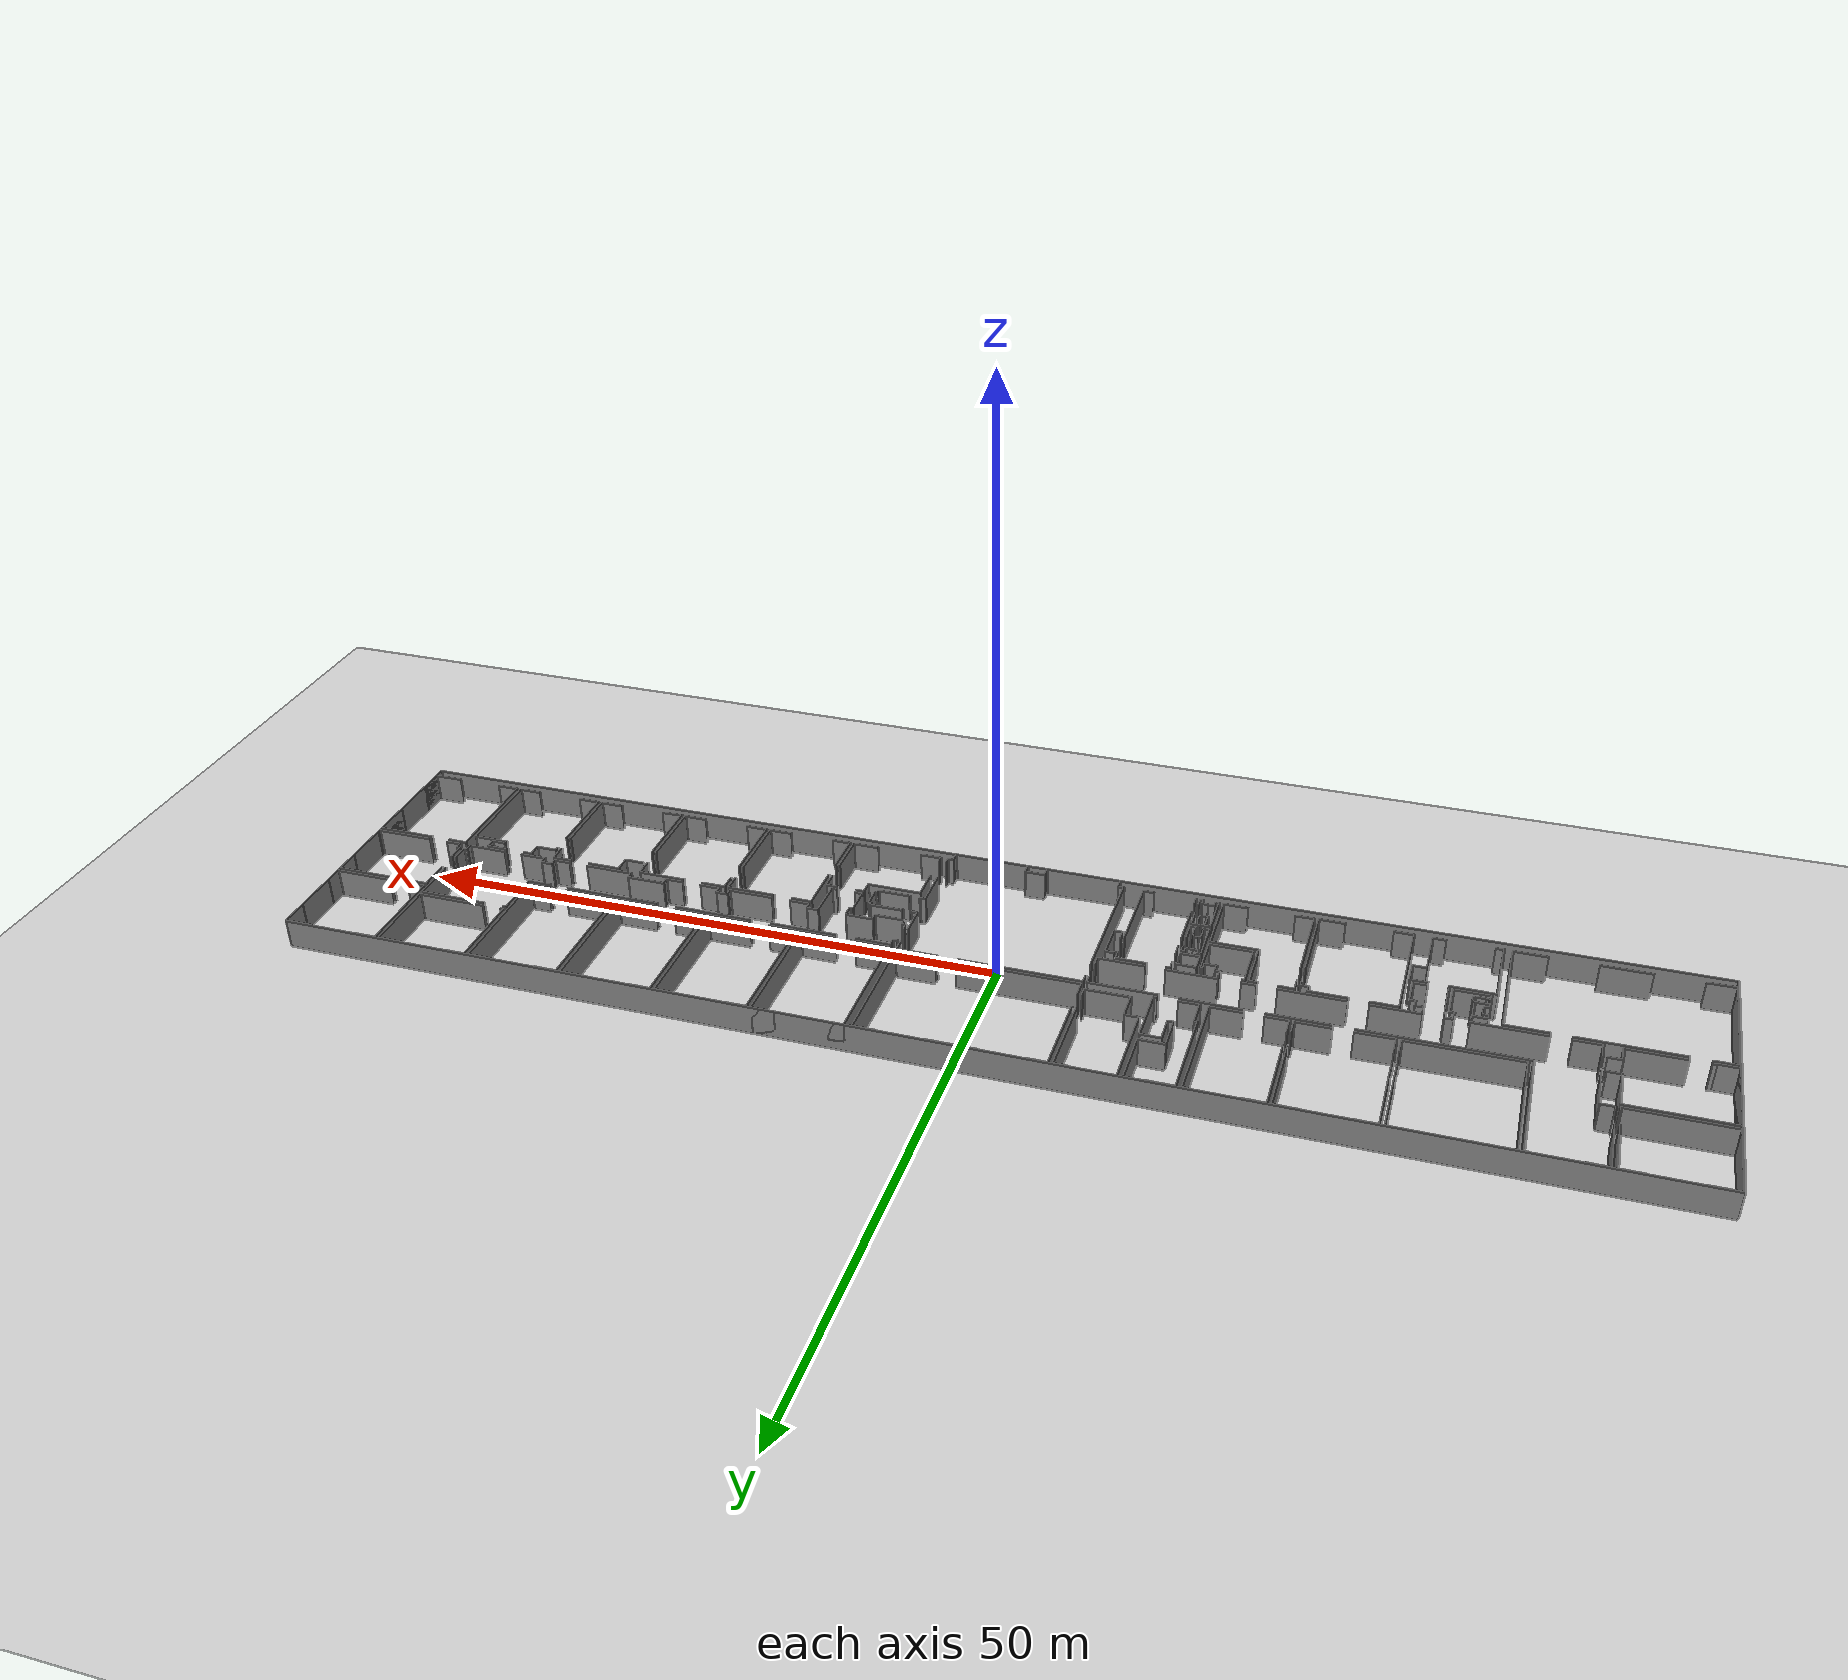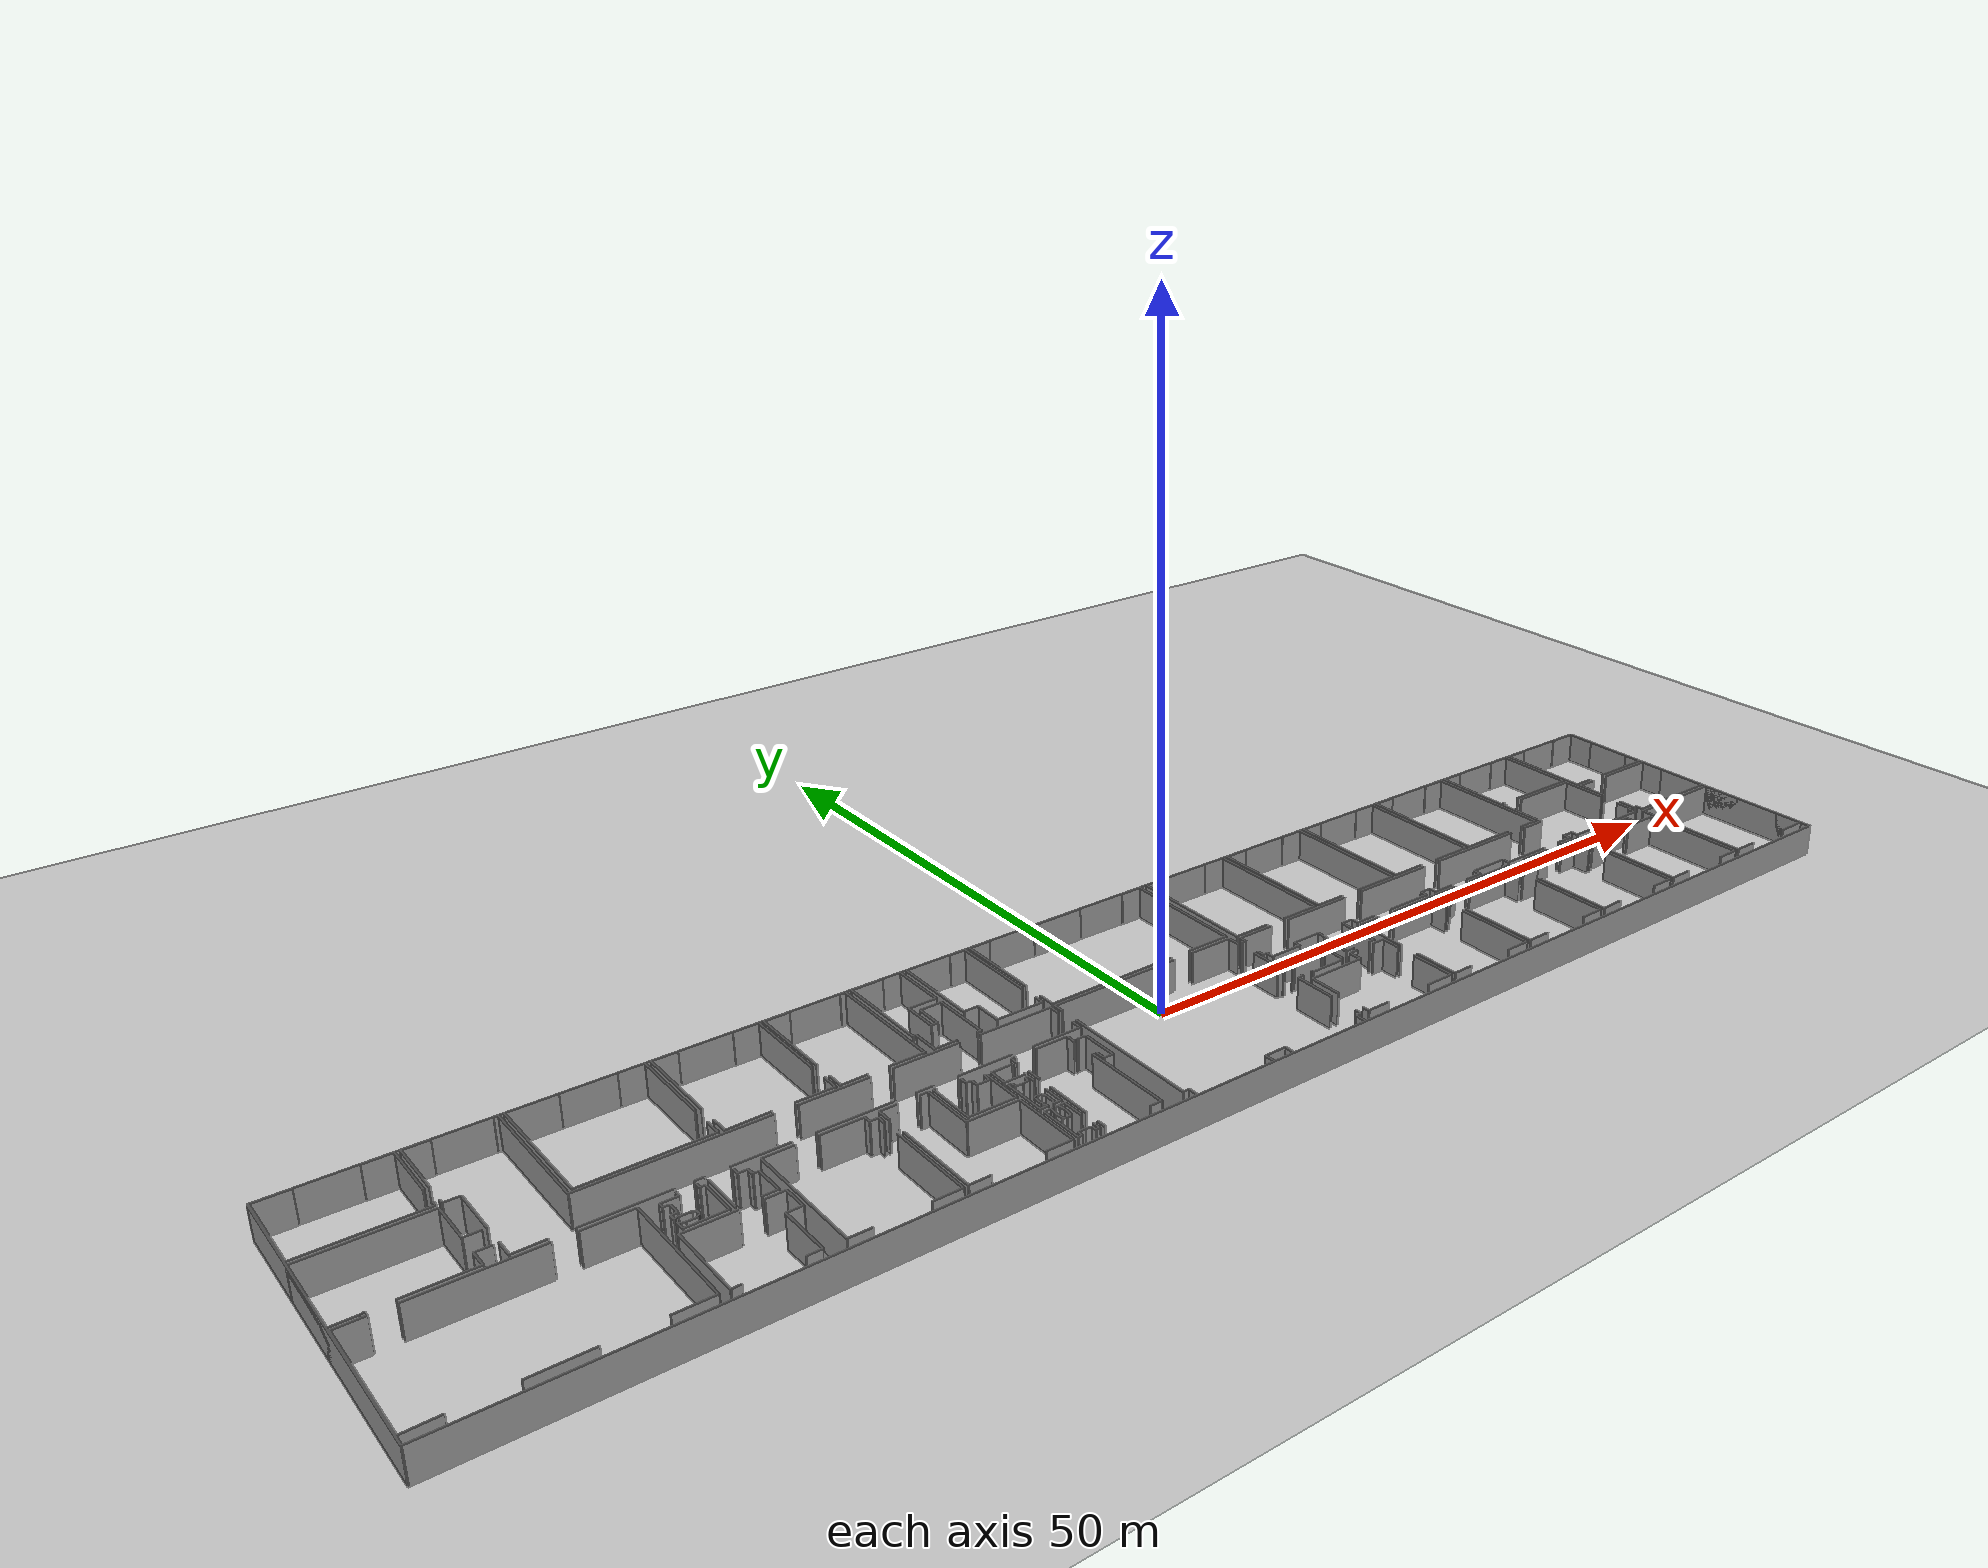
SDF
<sdf version="1.6">
  <world name="default">
    <light name="sun" type="directional">
      <cast_shadows>1</cast_shadows>
      <pose frame="">0 0 10 0 -0 0</pose>
      <diffuse>0.8 0.8 0.8 1</diffuse>
      <specular>0.1 0.1 0.1 1</specular>
      <attenuation>
        <range>1000</range>
        <constant>0.9</constant>
        <linear>0.01</linear>
        <quadratic>0.001</quadratic>
      </attenuation>
      <direction>-0.5 0.5 -1</direction>
    </light>
    <model name="ground_plane">
      <static>1</static>
      <link name="link">
        <collision name="collision">
          <geometry>
            <plane>
              <normal>0 0 1</normal>
              <size>100 100</size>
            </plane>
          </geometry>
          <surface>
            <friction>
              <ode>
                <mu>100</mu>
                <mu2>50</mu2>
              </ode>
              <torsional>
                <ode />
              </torsional>
            </friction>
            <contact>
              <ode />
            </contact>
            <bounce />
          </surface>
          <max_contacts>10</max_contacts>
        </collision>
        <visual name="visual">
          <cast_shadows>0</cast_shadows>
          <geometry>
            <plane>
              <normal>0 0 1</normal>
              <size>100 100</size>
            </plane>
          </geometry>
          <material>
            <script>
              <uri>file://media/materials/scripts/gazebo.material</uri>
              <name>Gazebo/Grey</name>
            </script>
          </material>
        </visual>
        <self_collide>0</self_collide>
        <kinematic>0</kinematic>
        <gravity>1</gravity>
      </link>
    </model>
    <gravity>0 0 -9.8</gravity>
    <magnetic_field>6e-06 2.3e-05 -4.2e-05</magnetic_field>
    <atmosphere type="adiabatic" />
    <physics default="0" name="default_physics" type="ode">
      <max_step_size>0.001</max_step_size>
      <real_time_factor>1</real_time_factor>
      <real_time_update_rate>1000</real_time_update_rate>
    </physics>
    <scene>
      <ambient>0.4 0.4 0.4 1</ambient>
      <background>0.7 0.7 0.7 1</background>
      <shadows>1</shadows>
    </scene>
    <spherical_coordinates>
      <surface_model>EARTH_WGS84</surface_model>
      <latitude_deg>0</latitude_deg>
      <longitude_deg>0</longitude_deg>
      <elevation>0</elevation>
      <heading_deg>0</heading_deg>
    </spherical_coordinates>
  <model name="0510034692_Layout1">
		<static>1</static>
		<link name="Wall_0">
			<collision name="Wall_0_Collision">
				<geometry>
					<box>
						<size>6.71726162908 0.1 2.5</size>
					</box>
				</geometry>
				<pose frame="">3.35863081454 0 1.25 0 0 0</pose>
			</collision>
			<visual name="Wall_0_Visual">
				<pose frame="">3.35863081454 0 1.25 0 0 0</pose>
				<geometry>
					<box>
						<size>6.71726162908 0.1 2.5</size>
					</box>
				</geometry>
				<material>
					<script>
						<uri>file://media/materials/scripts/gazebo.material</uri>
						<name>Gazebo/Grey</name>
					</script>
					<ambient>1 1 1 1</ambient>
				</material>
			</visual>
			<pose frame="">0.0487254612106 -6.75532839565 0 0 0 1.57079632679</pose>
		</link>
		<link name="Wall_1">
			<collision name="Wall_1_Collision">
				<geometry>
					<box>
						<size>2.41102210537 0.1 2.5</size>
					</box>
				</geometry>
				<pose frame="">1.20551105269 0 1.25 0 0 0</pose>
			</collision>
			<visual name="Wall_1_Visual">
				<pose frame="">1.20551105269 0 1.25 0 0 0</pose>
				<geometry>
					<box>
						<size>2.41102210537 0.1 2.5</size>
					</box>
				</geometry>
				<material>
					<script>
						<uri>file://media/materials/scripts/gazebo.material</uri>
						<name>Gazebo/Grey</name>
					</script>
					<ambient>1 1 1 1</ambient>
				</material>
			</visual>
			<pose frame="">0.0487254612106 -0.0380667665708 0 0 0 0.0</pose>
		</link>
		<link name="Wall_2">
			<collision name="Wall_2_Collision">
				<geometry>
					<box>
						<size>2.01373195159 0.1 2.5</size>
					</box>
				</geometry>
				<pose frame="">1.0068659758 0 1.25 0 0 0</pose>
			</collision>
			<visual name="Wall_2_Visual">
				<pose frame="">1.0068659758 0 1.25 0 0 0</pose>
				<geometry>
					<box>
						<size>2.01373195159 0.1 2.5</size>
					</box>
				</geometry>
				<material>
					<script>
						<uri>file://media/materials/scripts/gazebo.material</uri>
						<name>Gazebo/Grey</name>
					</script>
					<ambient>1 1 1 1</ambient>
				</material>
			</visual>
			<pose frame="">6.29751208303 -0.0380667665708 0 0 0 0.0</pose>
		</link>
		<link name="Wall_3">
			<collision name="Wall_3_Collision">
				<geometry>
					<box>
						<size>4.77166918965 0.1 2.5</size>
					</box>
				</geometry>
				<pose frame="">2.38583459482 0 1.25 0 0 0</pose>
			</collision>
			<visual name="Wall_3_Visual">
				<pose frame="">2.38583459482 0 1.25 0 0 0</pose>
				<geometry>
					<box>
						<size>4.77166918965 0.1 2.5</size>
					</box>
				</geometry>
				<material>
					<script>
						<uri>file://media/materials/scripts/gazebo.material</uri>
						<name>Gazebo/Grey</name>
					</script>
					<ambient>1 1 1 1</ambient>
				</material>
			</visual>
			<pose frame="">8.31124403462 -0.0380667665708 0 0 0 -1.57079632679</pose>
		</link>
		<link name="Wall_4">
			<collision name="Wall_4_Collision">
				<geometry>
					<box>
						<size>0.408329516083 0.1 2.5</size>
					</box>
				</geometry>
				<pose frame="">0.204164758041 0 1.25 0 0 0</pose>
			</collision>
			<visual name="Wall_4_Visual">
				<pose frame="">0.204164758041 0 1.25 0 0 0</pose>
				<geometry>
					<box>
						<size>0.408329516083 0.1 2.5</size>
					</box>
				</geometry>
				<material>
					<script>
						<uri>file://media/materials/scripts/gazebo.material</uri>
						<name>Gazebo/Grey</name>
					</script>
					<ambient>1 1 1 1</ambient>
				</material>
			</visual>
			<pose frame="">8.31124403462 -6.35499290055 0 0 0 -1.57079632679</pose>
		</link>
		<link name="Wall_5">
			<collision name="Wall_5_Collision">
				<geometry>
					<box>
						<size>8.26252244053 0.1 2.5</size>
					</box>
				</geometry>
				<pose frame="">4.13126122027 0 1.25 0 0 0</pose>
			</collision>
			<visual name="Wall_5_Visual">
				<pose frame="">4.13126122027 0 1.25 0 0 0</pose>
				<geometry>
					<box>
						<size>8.26252244053 0.1 2.5</size>
					</box>
				</geometry>
				<material>
					<script>
						<uri>file://media/materials/scripts/gazebo.material</uri>
						<name>Gazebo/Grey</name>
					</script>
					<ambient>1 1 1 1</ambient>
				</material>
			</visual>
			<pose frame="">8.31124403462 -6.76332241663 0 0 0 3.14062514975</pose>
		</link>
		<link name="Wall_6">
			<collision name="Wall_6_Collision">
				<geometry>
					<box>
						<size>1.69435178007 0.1 2.5</size>
					</box>
				</geometry>
				<pose frame="">0.847175890033 0 1.25 0 0 0</pose>
			</collision>
			<visual name="Wall_6_Visual">
				<pose frame="">0.847175890033 0 1.25 0 0 0</pose>
				<geometry>
					<box>
						<size>1.69435178007 0.1 2.5</size>
					</box>
				</geometry>
				<material>
					<script>
						<uri>file://media/materials/scripts/gazebo.material</uri>
						<name>Gazebo/Grey</name>
					</script>
					<ambient>1 1 1 1</ambient>
				</material>
			</visual>
			<pose frame="">1.69435178007 -13.794127313 0 0 0 3.14159265359</pose>
		</link>
		<link name="Wall_7">
			<collision name="Wall_7_Collision">
				<geometry>
					<box>
						<size>6.68680821582 0.1 2.5</size>
					</box>
				</geometry>
				<pose frame="">3.34340410791 0 1.25 0 0 0</pose>
			</collision>
			<visual name="Wall_7_Visual">
				<pose frame="">3.34340410791 0 1.25 0 0 0</pose>
				<geometry>
					<box>
						<size>6.68680821582 0.1 2.5</size>
					</box>
				</geometry>
				<material>
					<script>
						<uri>file://media/materials/scripts/gazebo.material</uri>
						<name>Gazebo/Grey</name>
					</script>
					<ambient>1 1 1 1</ambient>
				</material>
			</visual>
			<pose frame="">0.0 -13.794127313 0 0 0 1.57079632679</pose>
		</link>
		<link name="Wall_8">
			<collision name="Wall_8_Collision">
				<geometry>
					<box>
						<size>8.34448901076 0.1 2.5</size>
					</box>
				</geometry>
				<pose frame="">4.17224450538 0 1.25 0 0 0</pose>
			</collision>
			<visual name="Wall_8_Visual">
				<pose frame="">4.17224450538 0 1.25 0 0 0</pose>
				<geometry>
					<box>
						<size>8.34448901076 0.1 2.5</size>
					</box>
				</geometry>
				<material>
					<script>
						<uri>file://media/materials/scripts/gazebo.material</uri>
						<name>Gazebo/Grey</name>
					</script>
					<ambient>1 1 1 1</ambient>
				</material>
			</visual>
			<pose frame="">0.0 -7.10731909721 0 0 0 0.0</pose>
		</link>
		<link name="Wall_9">
			<collision name="Wall_9_Collision">
				<geometry>
					<box>
						<size>3.52866237189 0.1 2.5</size>
					</box>
				</geometry>
				<pose frame="">1.76433118594 0 1.25 0 0 0</pose>
			</collision>
			<visual name="Wall_9_Visual">
				<pose frame="">1.76433118594 0 1.25 0 0 0</pose>
				<geometry>
					<box>
						<size>3.52866237189 0.1 2.5</size>
					</box>
				</geometry>
				<material>
					<script>
						<uri>file://media/materials/scripts/gazebo.material</uri>
						<name>Gazebo/Grey</name>
					</script>
					<ambient>1 1 1 1</ambient>
				</material>
			</visual>
			<pose frame="">8.34448901076 -7.10731909721 0 0 0 -1.57079632679</pose>
		</link>
		<link name="Wall_10">
			<collision name="Wall_10_Collision">
				<geometry>
					<box>
						<size>1.10964624554 0.1 2.5</size>
					</box>
				</geometry>
				<pose frame="">0.554823122769 0 1.25 0 0 0</pose>
			</collision>
			<visual name="Wall_10_Visual">
				<pose frame="">0.554823122769 0 1.25 0 0 0</pose>
				<geometry>
					<box>
						<size>1.10964624554 0.1 2.5</size>
					</box>
				</geometry>
				<material>
					<script>
						<uri>file://media/materials/scripts/gazebo.material</uri>
						<name>Gazebo/Grey</name>
					</script>
					<ambient>1 1 1 1</ambient>
				</material>
			</visual>
			<pose frame="">8.34448901076 -10.6359814691 0 0 0 0.0</pose>
		</link>
		<link name="Wall_11">
			<collision name="Wall_11_Collision">
				<geometry>
					<box>
						<size>1.13121741326 0.1 2.5</size>
					</box>
				</geometry>
				<pose frame="">0.565608706631 0 1.25 0 0 0</pose>
			</collision>
			<visual name="Wall_11_Visual">
				<pose frame="">0.565608706631 0 1.25 0 0 0</pose>
				<geometry>
					<box>
						<size>1.13121741326 0.1 2.5</size>
					</box>
				</geometry>
				<material>
					<script>
						<uri>file://media/materials/scripts/gazebo.material</uri>
						<name>Gazebo/Grey</name>
					</script>
					<ambient>1 1 1 1</ambient>
				</material>
			</visual>
			<pose frame="">9.4541352563 -12.334266815 0 0 0 3.14159265359</pose>
		</link>
		<link name="Wall_12">
			<collision name="Wall_12_Collision">
				<geometry>
					<box>
						<size>1.3927360996 0.1 2.5</size>
					</box>
				</geometry>
				<pose frame="">0.696368049801 0 1.25 0 0 0</pose>
			</collision>
			<visual name="Wall_12_Visual">
				<pose frame="">0.696368049801 0 1.25 0 0 0</pose>
				<geometry>
					<box>
						<size>1.3927360996 0.1 2.5</size>
					</box>
				</geometry>
				<material>
					<script>
						<uri>file://media/materials/scripts/gazebo.material</uri>
						<name>Gazebo/Grey</name>
					</script>
					<ambient>1 1 1 1</ambient>
				</material>
			</visual>
			<pose frame="">8.32291784304 -12.334266815 0 0 0 -1.57079632679</pose>
		</link>
		<link name="Wall_13">
			<collision name="Wall_13_Collision">
				<geometry>
					<box>
						<size>4.69870788705 0.1 2.5</size>
					</box>
				</geometry>
				<pose frame="">2.34935394353 0 1.25 0 0 0</pose>
			</collision>
			<visual name="Wall_13_Visual">
				<pose frame="">2.34935394353 0 1.25 0 0 0</pose>
				<geometry>
					<box>
						<size>4.69870788705 0.1 2.5</size>
					</box>
				</geometry>
				<material>
					<script>
						<uri>file://media/materials/scripts/gazebo.material</uri>
						<name>Gazebo/Grey</name>
					</script>
					<ambient>1 1 1 1</ambient>
				</material>
			</visual>
			<pose frame="">8.32291784304 -13.7270029146 0 0 0 3.14159265359</pose>
		</link>
		<link name="Wall_14">
			<collision name="Wall_14_Collision">
				<geometry>
					<box>
						<size>0.342268617211 0.1 2.5</size>
					</box>
				</geometry>
				<pose frame="">0.171134308605 0 1.25 0 0 0</pose>
			</collision>
			<visual name="Wall_14_Visual">
				<pose frame="">0.171134308605 0 1.25 0 0 0</pose>
				<geometry>
					<box>
						<size>0.342268617211 0.1 2.5</size>
					</box>
				</geometry>
				<material>
					<script>
						<uri>file://media/materials/scripts/gazebo.material</uri>
						<name>Gazebo/Grey</name>
					</script>
					<ambient>1 1 1 1</ambient>
				</material>
			</visual>
			<pose frame="">2.029973772 -13.7270029146 0 0 0 -2.94419709374</pose>
		</link>
		<link name="Wall_15">
			<collision name="Wall_15_Collision">
				<geometry>
					<box>
						<size>9.90078531739 0.1 2.5</size>
					</box>
				</geometry>
				<pose frame="">4.9503926587 0 1.25 0 0 0</pose>
			</collision>
			<visual name="Wall_15_Visual">
				<pose frame="">4.9503926587 0 1.25 0 0 0</pose>
				<geometry>
					<box>
						<size>9.90078531739 0.1 2.5</size>
					</box>
				</geometry>
				<material>
					<script>
						<uri>file://media/materials/scripts/gazebo.material</uri>
						<name>Gazebo/Grey</name>
					</script>
					<ambient>1 1 1 1</ambient>
				</material>
			</visual>
			<pose frame="">0.0498674642077 -23.9970358678 0 0 0 1.57079632679</pose>
		</link>
		<link name="Wall_16">
			<collision name="Wall_16_Collision">
				<geometry>
					<box>
						<size>1.9633569305 0.1 2.5</size>
					</box>
				</geometry>
				<pose frame="">0.981678465249 0 1.25 0 0 0</pose>
			</collision>
			<visual name="Wall_16_Visual">
				<pose frame="">0.981678465249 0 1.25 0 0 0</pose>
				<geometry>
					<box>
						<size>1.9633569305 0.1 2.5</size>
					</box>
				</geometry>
				<material>
					<script>
						<uri>file://media/materials/scripts/gazebo.material</uri>
						<name>Gazebo/Grey</name>
					</script>
					<ambient>1 1 1 1</ambient>
				</material>
			</visual>
			<pose frame="">0.0498674642077 -14.0962505504 0 0 0 0.0</pose>
		</link>
		<link name="Wall_17">
			<collision name="Wall_17_Collision">
				<geometry>
					<box>
						<size>8.42544433433 0.1 2.5</size>
					</box>
				</geometry>
				<pose frame="">4.21272216717 0 1.25 0 0 0</pose>
			</collision>
			<visual name="Wall_17_Visual">
				<pose frame="">4.21272216717 0 1.25 0 0 0</pose>
				<geometry>
					<box>
						<size>8.42544433433 0.1 2.5</size>
					</box>
				</geometry>
				<material>
					<script>
						<uri>file://media/materials/scripts/gazebo.material</uri>
						<name>Gazebo/Grey</name>
					</script>
					<ambient>1 1 1 1</ambient>
				</material>
			</visual>
			<pose frame="">3.61126725535 -14.0962505504 0 0 0 0.0</pose>
		</link>
		<link name="Wall_18">
			<collision name="Wall_18_Collision">
				<geometry>
					<box>
						<size>3.50214252451 0.1 2.5</size>
					</box>
				</geometry>
				<pose frame="">1.75107126226 0 1.25 0 0 0</pose>
			</collision>
			<visual name="Wall_18_Visual">
				<pose frame="">1.75107126226 0 1.25 0 0 0</pose>
				<geometry>
					<box>
						<size>3.50214252451 0.1 2.5</size>
					</box>
				</geometry>
				<material>
					<script>
						<uri>file://media/materials/scripts/gazebo.material</uri>
						<name>Gazebo/Grey</name>
					</script>
					<ambient>1 1 1 1</ambient>
				</material>
			</visual>
			<pose frame="">13.6082346029 -14.0962505504 0 0 0 0.0</pose>
		</link>
		<link name="Wall_19">
			<collision name="Wall_19_Collision">
				<geometry>
					<box>
						<size>9.84888762564 0.1 2.5</size>
					</box>
				</geometry>
				<pose frame="">4.92444381282 0 1.25 0 0 0</pose>
			</collision>
			<visual name="Wall_19_Visual">
				<pose frame="">4.92444381282 0 1.25 0 0 0</pose>
				<geometry>
					<box>
						<size>9.84888762564 0.1 2.5</size>
					</box>
				</geometry>
				<material>
					<script>
						<uri>file://media/materials/scripts/gazebo.material</uri>
						<name>Gazebo/Grey</name>
					</script>
					<ambient>1 1 1 1</ambient>
				</material>
			</visual>
			<pose frame="">17.1103771275 -14.0962505504 0 0 0 -1.57079632679</pose>
		</link>
		<link name="Wall_20">
			<collision name="Wall_20_Collision">
				<geometry>
					<box>
						<size>2.76897660036 0.1 2.5</size>
					</box>
				</geometry>
				<pose frame="">1.38448830018 0 1.25 0 0 0</pose>
			</collision>
			<visual name="Wall_20_Visual">
				<pose frame="">1.38448830018 0 1.25 0 0 0</pose>
				<geometry>
					<box>
						<size>2.76897660036 0.1 2.5</size>
					</box>
				</geometry>
				<material>
					<script>
						<uri>file://media/materials/scripts/gazebo.material</uri>
						<name>Gazebo/Grey</name>
					</script>
					<ambient>1 1 1 1</ambient>
				</material>
			</visual>
			<pose frame="">17.1103771275 -23.945138176 0 0 0 3.14159265359</pose>
		</link>
		<link name="Wall_21">
			<collision name="Wall_21_Collision">
				<geometry>
					<box>
						<size>4.11057634353 0.1 2.5</size>
					</box>
				</geometry>
				<pose frame="">2.05528817177 0 1.25 0 0 0</pose>
			</collision>
			<visual name="Wall_21_Visual">
				<pose frame="">2.05528817177 0 1.25 0 0 0</pose>
				<geometry>
					<box>
						<size>4.11057634353 0.1 2.5</size>
					</box>
				</geometry>
				<material>
					<script>
						<uri>file://media/materials/scripts/gazebo.material</uri>
						<name>Gazebo/Grey</name>
					</script>
					<ambient>1 1 1 1</ambient>
				</material>
			</visual>
			<pose frame="">10.4239495793 -23.945138176 0 0 0 3.14159265359</pose>
		</link>
		<link name="Wall_22">
			<collision name="Wall_22_Collision">
				<geometry>
					<box>
						<size>2.36578439888 0.1 2.5</size>
					</box>
				</geometry>
				<pose frame="">1.18289219944 0 1.25 0 0 0</pose>
			</collision>
			<visual name="Wall_22_Visual">
				<pose frame="">1.18289219944 0 1.25 0 0 0</pose>
				<geometry>
					<box>
						<size>2.36578439888 0.1 2.5</size>
					</box>
				</geometry>
				<material>
					<script>
						<uri>file://media/materials/scripts/gazebo.material</uri>
						<name>Gazebo/Grey</name>
					</script>
					<ambient>1 1 1 1</ambient>
				</material>
			</visual>
			<pose frame="">2.41508256047 -23.945138176 0 0 0 -3.11965411385</pose>
		</link>
		<link name="Wall_23">
			<collision name="Wall_23_Collision">
				<geometry>
					<box>
						<size>10.0756386652 0.1 2.5</size>
					</box>
				</geometry>
				<pose frame="">5.03781933259 0 1.25 0 0 0</pose>
			</collision>
			<visual name="Wall_23_Visual">
				<pose frame="">5.03781933259 0 1.25 0 0 0</pose>
				<geometry>
					<box>
						<size>10.0756386652 0.1 2.5</size>
					</box>
				</geometry>
				<material>
					<script>
						<uri>file://media/materials/scripts/gazebo.material</uri>
						<name>Gazebo/Grey</name>
					</script>
					<ambient>1 1 1 1</ambient>
				</material>
			</visual>
			<pose frame="">14.9802877594 -10.0812217909 0 0 0 1.57079632679</pose>
		</link>
		<link name="Wall_24">
			<collision name="Wall_24_Collision">
				<geometry>
					<box>
						<size>3.48425114422 0.1 2.5</size>
					</box>
				</geometry>
				<pose frame="">1.74212557211 0 1.25 0 0 0</pose>
			</collision>
			<visual name="Wall_24_Visual">
				<pose frame="">1.74212557211 0 1.25 0 0 0</pose>
				<geometry>
					<box>
						<size>3.48425114422 0.1 2.5</size>
					</box>
				</geometry>
				<material>
					<script>
						<uri>file://media/materials/scripts/gazebo.material</uri>
						<name>Gazebo/Grey</name>
					</script>
					<ambient>1 1 1 1</ambient>
				</material>
			</visual>
			<pose frame="">14.9802877594 -0.00558312576371 0 0 0 0.0</pose>
		</link>
		<link name="Wall_25">
			<collision name="Wall_25_Collision">
				<geometry>
					<box>
						<size>1.8863351728 0.1 2.5</size>
					</box>
				</geometry>
				<pose frame="">0.943167586402 0 1.25 0 0 0</pose>
			</collision>
			<visual name="Wall_25_Visual">
				<pose frame="">0.943167586402 0 1.25 0 0 0</pose>
				<geometry>
					<box>
						<size>1.8863351728 0.1 2.5</size>
					</box>
				</geometry>
				<material>
					<script>
						<uri>file://media/materials/scripts/gazebo.material</uri>
						<name>Gazebo/Grey</name>
					</script>
					<ambient>1 1 1 1</ambient>
				</material>
			</visual>
			<pose frame="">22.3261585938 -0.00558312576371 0 0 0 0.0</pose>
		</link>
		<link name="Wall_26">
			<collision name="Wall_26_Collision">
				<geometry>
					<box>
						<size>6.96862917767 0.1 2.5</size>
					</box>
				</geometry>
				<pose frame="">3.48431458883 0 1.25 0 0 0</pose>
			</collision>
			<visual name="Wall_26_Visual">
				<pose frame="">3.48431458883 0 1.25 0 0 0</pose>
				<geometry>
					<box>
						<size>6.96862917767 0.1 2.5</size>
					</box>
				</geometry>
				<material>
					<script>
						<uri>file://media/materials/scripts/gazebo.material</uri>
						<name>Gazebo/Grey</name>
					</script>
					<ambient>1 1 1 1</ambient>
				</material>
			</visual>
			<pose frame="">24.2124937666 -0.00558312576371 0 0 0 -1.57079632679</pose>
		</link>
		<link name="Wall_27">
			<collision name="Wall_27_Collision">
				<geometry>
					<box>
						<size>1.44247667459 0.1 2.5</size>
					</box>
				</geometry>
				<pose frame="">0.721238337294 0 1.25 0 0 0</pose>
			</collision>
			<visual name="Wall_27_Visual">
				<pose frame="">0.721238337294 0 1.25 0 0 0</pose>
				<geometry>
					<box>
						<size>1.44247667459 0.1 2.5</size>
					</box>
				</geometry>
				<material>
					<script>
						<uri>file://media/materials/scripts/gazebo.material</uri>
						<name>Gazebo/Grey</name>
					</script>
					<ambient>1 1 1 1</ambient>
				</material>
			</visual>
			<pose frame="">24.2124937666 -8.59433388869 0 0 0 -1.57079632679</pose>
		</link>
		<link name="Wall_28">
			<collision name="Wall_28_Collision">
				<geometry>
					<box>
						<size>9.23231282596 0.1 2.5</size>
					</box>
				</geometry>
				<pose frame="">4.61615641298 0 1.25 0 0 0</pose>
			</collision>
			<visual name="Wall_28_Visual">
				<pose frame="">4.61615641298 0 1.25 0 0 0</pose>
				<geometry>
					<box>
						<size>9.23231282596 0.1 2.5</size>
					</box>
				</geometry>
				<material>
					<script>
						<uri>file://media/materials/scripts/gazebo.material</uri>
						<name>Gazebo/Grey</name>
					</script>
					<ambient>1 1 1 1</ambient>
				</material>
			</visual>
			<pose frame="">24.2124937666 -10.0368105633 0 0 0 -3.13678222312</pose>
		</link>
		<link name="Wall_29">
			<collision name="Wall_29_Collision">
				<geometry>
					<box>
						<size>1.45135892012 0.1 2.5</size>
					</box>
				</geometry>
				<pose frame="">0.725679460061 0 1.25 0 0 0</pose>
			</collision>
			<visual name="Wall_29_Visual">
				<pose frame="">0.725679460061 0 1.25 0 0 0</pose>
				<geometry>
					<box>
						<size>1.45135892012 0.1 2.5</size>
					</box>
				</geometry>
				<material>
					<script>
						<uri>file://media/materials/scripts/gazebo.material</uri>
						<name>Gazebo/Grey</name>
					</script>
					<ambient>1 1 1 1</ambient>
				</material>
			</visual>
			<pose frame="">24.6123217048 -10.087566252 0 0 0 1.57079632679</pose>
		</link>
		<link name="Wall_30">
			<collision name="Wall_30_Collision">
				<geometry>
					<box>
						<size>7.02052686943 0.1 2.5</size>
					</box>
				</geometry>
				<pose frame="">3.51026343471 0 1.25 0 0 0</pose>
			</collision>
			<visual name="Wall_30_Visual">
				<pose frame="">3.51026343471 0 1.25 0 0 0</pose>
				<geometry>
					<box>
						<size>7.02052686943 0.1 2.5</size>
					</box>
				</geometry>
				<material>
					<script>
						<uri>file://media/materials/scripts/gazebo.material</uri>
						<name>Gazebo/Grey</name>
					</script>
					<ambient>1 1 1 1</ambient>
				</material>
			</visual>
			<pose frame="">24.6123217048 -7.04971139046 0 0 0 1.57079632679</pose>
		</link>
		<link name="Wall_31">
			<collision name="Wall_31_Collision">
				<geometry>
					<box>
						<size>1.85638931644 0.1 2.5</size>
					</box>
				</geometry>
				<pose frame="">0.928194658218 0 1.25 0 0 0</pose>
			</collision>
			<visual name="Wall_31_Visual">
				<pose frame="">0.928194658218 0 1.25 0 0 0</pose>
				<geometry>
					<box>
						<size>1.85638931644 0.1 2.5</size>
					</box>
				</geometry>
				<material>
					<script>
						<uri>file://media/materials/scripts/gazebo.material</uri>
						<name>Gazebo/Grey</name>
					</script>
					<ambient>1 1 1 1</ambient>
				</material>
			</visual>
			<pose frame="">24.6123217048 -0.0291845210376 0 0 0 0.0</pose>
		</link>
		<link name="Wall_32">
			<collision name="Wall_32_Collision">
				<geometry>
					<box>
						<size>1.92389438249 0.1 2.5</size>
					</box>
				</geometry>
				<pose frame="">0.961947191244 0 1.25 0 0 0</pose>
			</collision>
			<visual name="Wall_32_Visual">
				<pose frame="">0.961947191244 0 1.25 0 0 0</pose>
				<geometry>
					<box>
						<size>1.92389438249 0.1 2.5</size>
					</box>
				</geometry>
				<material>
					<script>
						<uri>file://media/materials/scripts/gazebo.material</uri>
						<name>Gazebo/Grey</name>
					</script>
					<ambient>1 1 1 1</ambient>
				</material>
			</visual>
			<pose frame="">30.3502523192 -0.0291845210376 0 0 0 0.0</pose>
		</link>
		<link name="Wall_33">
			<collision name="Wall_33_Collision">
				<geometry>
					<box>
						<size>6.9867743364 0.1 2.5</size>
					</box>
				</geometry>
				<pose frame="">3.4933871682 0 1.25 0 0 0</pose>
			</collision>
			<visual name="Wall_33_Visual">
				<pose frame="">3.4933871682 0 1.25 0 0 0</pose>
				<geometry>
					<box>
						<size>6.9867743364 0.1 2.5</size>
					</box>
				</geometry>
				<material>
					<script>
						<uri>file://media/materials/scripts/gazebo.material</uri>
						<name>Gazebo/Grey</name>
					</script>
					<ambient>1 1 1 1</ambient>
				</material>
			</visual>
			<pose frame="">32.2741467017 -0.0291845210376 0 0 0 -1.57079632679</pose>
		</link>
		<link name="Wall_34">
			<collision name="Wall_34_Collision">
				<geometry>
					<box>
						<size>1.39019831516 0.1 2.5</size>
					</box>
				</geometry>
				<pose frame="">0.695099157582 0 1.25 0 0 0</pose>
			</collision>
			<visual name="Wall_34_Visual">
				<pose frame="">0.695099157582 0 1.25 0 0 0</pose>
				<geometry>
					<box>
						<size>1.39019831516 0.1 2.5</size>
					</box>
				</geometry>
				<material>
					<script>
						<uri>file://media/materials/scripts/gazebo.material</uri>
						<name>Gazebo/Grey</name>
					</script>
					<ambient>1 1 1 1</ambient>
				</material>
			</visual>
			<pose frame="">32.2741467017 -8.62491419116 0 0 0 -1.57079632679</pose>
		</link>
		<link name="Wall_35">
			<collision name="Wall_35_Collision">
				<geometry>
					<box>
						<size>2.88837935817 0.1 2.5</size>
					</box>
				</geometry>
				<pose frame="">1.44418967908 0 1.25 0 0 0</pose>
			</collision>
			<visual name="Wall_35_Visual">
				<pose frame="">1.44418967908 0 1.25 0 0 0</pose>
				<geometry>
					<box>
						<size>2.88837935817 0.1 2.5</size>
					</box>
				</geometry>
				<material>
					<script>
						<uri>file://media/materials/scripts/gazebo.material</uri>
						<name>Gazebo/Grey</name>
					</script>
					<ambient>1 1 1 1</ambient>
				</material>
			</visual>
			<pose frame="">32.2741467017 -10.0151125063 0 0 0 3.14159265359</pose>
		</link>
		<link name="Wall_36">
			<collision name="Wall_36_Collision">
				<geometry>
					<box>
						<size>3.19639943531 0.1 2.5</size>
					</box>
				</geometry>
				<pose frame="">1.59819971765 0 1.25 0 0 0</pose>
			</collision>
			<visual name="Wall_36_Visual">
				<pose frame="">1.59819971765 0 1.25 0 0 0</pose>
				<geometry>
					<box>
						<size>3.19639943531 0.1 2.5</size>
					</box>
				</geometry>
				<material>
					<script>
						<uri>file://media/materials/scripts/gazebo.material</uri>
						<name>Gazebo/Grey</name>
					</script>
					<ambient>1 1 1 1</ambient>
				</material>
			</visual>
			<pose frame="">27.8078998692 -10.0151125063 0 0 0 -3.11892341179</pose>
		</link>
		<link name="Wall_37">
			<collision name="Wall_37_Collision">
				<geometry>
					<box>
						<size>1.41227703978 0.1 2.5</size>
					</box>
				</geometry>
				<pose frame="">0.706138519888 0 1.25 0 0 0</pose>
			</collision>
			<visual name="Wall_37_Visual">
				<pose frame="">0.706138519888 0 1.25 0 0 0</pose>
				<geometry>
					<box>
						<size>1.41227703978 0.1 2.5</size>
					</box>
				</geometry>
				<material>
					<script>
						<uri>file://media/materials/scripts/gazebo.material</uri>
						<name>Gazebo/Grey</name>
					</script>
					<ambient>1 1 1 1</ambient>
				</material>
			</visual>
			<pose frame="">32.6076115769 -10.0371912309 0 0 0 1.57079632679</pose>
		</link>
		<link name="Wall_38">
			<collision name="Wall_38_Collision">
				<geometry>
					<box>
						<size>6.99159612683 0.1 2.5</size>
					</box>
				</geometry>
				<pose frame="">3.49579806342 0 1.25 0 0 0</pose>
			</collision>
			<visual name="Wall_38_Visual">
				<pose frame="">3.49579806342 0 1.25 0 0 0</pose>
				<geometry>
					<box>
						<size>6.99159612683 0.1 2.5</size>
					</box>
				</geometry>
				<material>
					<script>
						<uri>file://media/materials/scripts/gazebo.material</uri>
						<name>Gazebo/Grey</name>
					</script>
					<ambient>1 1 1 1</ambient>
				</material>
			</visual>
			<pose frame="">32.6076115769 -7.04869627669 0 0 0 1.57079632679</pose>
		</link>
		<link name="Wall_39">
			<collision name="Wall_39_Collision">
				<geometry>
					<box>
						<size>1.90118121177 0.1 2.5</size>
					</box>
				</geometry>
				<pose frame="">0.950590605883 0 1.25 0 0 0</pose>
			</collision>
			<visual name="Wall_39_Visual">
				<pose frame="">0.950590605883 0 1.25 0 0 0</pose>
				<geometry>
					<box>
						<size>1.90118121177 0.1 2.5</size>
					</box>
				</geometry>
				<material>
					<script>
						<uri>file://media/materials/scripts/gazebo.material</uri>
						<name>Gazebo/Grey</name>
					</script>
					<ambient>1 1 1 1</ambient>
				</material>
			</visual>
			<pose frame="">32.6076115769 -0.0571001498562 0 0 0 0.0</pose>
		</link>
		<link name="Wall_40">
			<collision name="Wall_40_Collision">
				<geometry>
					<box>
						<size>0.456801198849 0.1 2.5</size>
					</box>
				</geometry>
				<pose frame="">0.228400599425 0 1.25 0 0 0</pose>
			</collision>
			<visual name="Wall_40_Visual">
				<pose frame="">0.228400599425 0 1.25 0 0 0</pose>
				<geometry>
					<box>
						<size>0.456801198849 0.1 2.5</size>
					</box>
				</geometry>
				<material>
					<script>
						<uri>file://media/materials/scripts/gazebo.material</uri>
						<name>Gazebo/Grey</name>
					</script>
					<ambient>1 1 1 1</ambient>
				</material>
			</visual>
			<pose frame="">38.3408472901 -0.0571001498562 0 0 0 0.0</pose>
		</link>
		<link name="Wall_41">
			<collision name="Wall_41_Collision">
				<geometry>
					<box>
						<size>9.96080391935 0.1 2.5</size>
					</box>
				</geometry>
				<pose frame="">4.98040195968 0 1.25 0 0 0</pose>
			</collision>
			<visual name="Wall_41_Visual">
				<pose frame="">4.98040195968 0 1.25 0 0 0</pose>
				<geometry>
					<box>
						<size>9.96080391935 0.1 2.5</size>
					</box>
				</geometry>
				<material>
					<script>
						<uri>file://media/materials/scripts/gazebo.material</uri>
						<name>Gazebo/Grey</name>
					</script>
					<ambient>1 1 1 1</ambient>
				</material>
			</visual>
			<pose frame="">38.7976484889 -0.0571001498562 0 0 0 -1.57079632679</pose>
		</link>
		<link name="Wall_42">
			<collision name="Wall_42_Collision">
				<geometry>
					<box>
						<size>2.65198473776 0.1 2.5</size>
					</box>
				</geometry>
				<pose frame="">1.32599236888 0 1.25 0 0 0</pose>
			</collision>
			<visual name="Wall_42_Visual">
				<pose frame="">1.32599236888 0 1.25 0 0 0</pose>
				<geometry>
					<box>
						<size>2.65198473776 0.1 2.5</size>
					</box>
				</geometry>
				<material>
					<script>
						<uri>file://media/materials/scripts/gazebo.material</uri>
						<name>Gazebo/Grey</name>
					</script>
					<ambient>1 1 1 1</ambient>
				</material>
			</visual>
			<pose frame="">38.7976484889 -10.0179040692 0 0 0 3.14159265359</pose>
		</link>
		<link name="Wall_43">
			<collision name="Wall_43_Collision">
				<geometry>
					<box>
						<size>1.96269036396 0.1 2.5</size>
					</box>
				</geometry>
				<pose frame="">0.98134518198 0 1.25 0 0 0</pose>
			</collision>
			<visual name="Wall_43_Visual">
				<pose frame="">0.98134518198 0 1.25 0 0 0</pose>
				<geometry>
					<box>
						<size>1.96269036396 0.1 2.5</size>
					</box>
				</geometry>
				<material>
					<script>
						<uri>file://media/materials/scripts/gazebo.material</uri>
						<name>Gazebo/Grey</name>
					</script>
					<ambient>1 1 1 1</ambient>
				</material>
			</visual>
			<pose frame="">34.570207172 -10.0179040692 0 0 0 -3.13176559553</pose>
		</link>
		<link name="Wall_44">
			<collision name="Wall_44_Collision">
				<geometry>
					<box>
						<size>2.21929249108 0.1 2.5</size>
					</box>
				</geometry>
				<pose frame="">1.10964624554 0 1.25 0 0 0</pose>
			</collision>
			<visual name="Wall_44_Visual">
				<pose frame="">1.10964624554 0 1.25 0 0 0</pose>
				<geometry>
					<box>
						<size>2.21929249108 0.1 2.5</size>
					</box>
				</geometry>
				<material>
					<script>
						<uri>file://media/materials/scripts/gazebo.material</uri>
						<name>Gazebo/Grey</name>
					</script>
					<ambient>1 1 1 1</ambient>
				</material>
			</visual>
			<pose frame="">39.5257388442 -10.0590161771 0 0 0 1.57079632679</pose>
		</link>
		<link name="Wall_45">
			<collision name="Wall_45_Collision">
				<geometry>
					<box>
						<size>0.254159143146 0.1 2.5</size>
					</box>
				</geometry>
				<pose frame="">0.127079571573 0 1.25 0 0 0</pose>
			</collision>
			<visual name="Wall_45_Visual">
				<pose frame="">0.127079571573 0 1.25 0 0 0</pose>
				<geometry>
					<box>
						<size>0.254159143146 0.1 2.5</size>
					</box>
				</geometry>
				<material>
					<script>
						<uri>file://media/materials/scripts/gazebo.material</uri>
						<name>Gazebo/Grey</name>
					</script>
					<ambient>1 1 1 1</ambient>
				</material>
			</visual>
			<pose frame="">39.5257388442 -7.83972368603 0 0 0 3.14109340251</pose>
		</link>
		<link name="Wall_46">
			<collision name="Wall_46_Collision">
				<geometry>
					<box>
						<size>7.78135464396 0.1 2.5</size>
					</box>
				</geometry>
				<pose frame="">3.89067732198 0 1.25 0 0 0</pose>
			</collision>
			<visual name="Wall_46_Visual">
				<pose frame="">3.89067732198 0 1.25 0 0 0</pose>
				<geometry>
					<box>
						<size>7.78135464396 0.1 2.5</size>
					</box>
				</geometry>
				<material>
					<script>
						<uri>file://media/materials/scripts/gazebo.material</uri>
						<name>Gazebo/Grey</name>
					</script>
					<ambient>1 1 1 1</ambient>
				</material>
			</visual>
			<pose frame="">39.2715797327 -7.83959679681 0 0 0 1.57079632679</pose>
		</link>
		<link name="Wall_47">
			<collision name="Wall_47_Collision">
				<geometry>
					<box>
						<size>2.41787412335 0.1 2.5</size>
					</box>
				</geometry>
				<pose frame="">1.20893706168 0 1.25 0 0 0</pose>
			</collision>
			<visual name="Wall_47_Visual">
				<pose frame="">1.20893706168 0 1.25 0 0 0</pose>
				<geometry>
					<box>
						<size>2.41787412335 0.1 2.5</size>
					</box>
				</geometry>
				<material>
					<script>
						<uri>file://media/materials/scripts/gazebo.material</uri>
						<name>Gazebo/Grey</name>
					</script>
					<ambient>1 1 1 1</ambient>
				</material>
			</visual>
			<pose frame="">39.2715797327 -0.0582421528533 0 0 0 0.0</pose>
		</link>
		<link name="Wall_48">
			<collision name="Wall_48_Collision">
				<geometry>
					<box>
						<size>4.5286763297 0.1 2.5</size>
					</box>
				</geometry>
				<pose frame="">2.26433816485 0 1.25 0 0 0</pose>
			</collision>
			<visual name="Wall_48_Visual">
				<pose frame="">2.26433816485 0 1.25 0 0 0</pose>
				<geometry>
					<box>
						<size>4.5286763297 0.1 2.5</size>
					</box>
				</geometry>
				<material>
					<script>
						<uri>file://media/materials/scripts/gazebo.material</uri>
						<name>Gazebo/Grey</name>
					</script>
					<ambient>1 1 1 1</ambient>
				</material>
			</visual>
			<pose frame="">43.1574352643 -0.0582421528533 0 0 0 -1.57079632679</pose>
		</link>
		<link name="Wall_49">
			<collision name="Wall_49_Collision">
				<geometry>
					<box>
						<size>2.16840991309 0.1 2.5</size>
					</box>
				</geometry>
				<pose frame="">1.08420495655 0 1.25 0 0 0</pose>
			</collision>
			<visual name="Wall_49_Visual">
				<pose frame="">1.08420495655 0 1.25 0 0 0</pose>
				<geometry>
					<box>
						<size>2.16840991309 0.1 2.5</size>
					</box>
				</geometry>
				<material>
					<script>
						<uri>file://media/materials/scripts/gazebo.material</uri>
						<name>Gazebo/Grey</name>
					</script>
					<ambient>1 1 1 1</ambient>
				</material>
			</visual>
			<pose frame="">43.1574352643 -4.58691848256 0 0 0 3.14159265359</pose>
		</link>
		<link name="Wall_50">
			<collision name="Wall_50_Collision">
				<geometry>
					<box>
						<size>2.79207043874 0.1 2.5</size>
					</box>
				</geometry>
				<pose frame="">1.39603521937 0 1.25 0 0 0</pose>
			</collision>
			<visual name="Wall_50_Visual">
				<pose frame="">1.39603521937 0 1.25 0 0 0</pose>
				<geometry>
					<box>
						<size>2.79207043874 0.1 2.5</size>
					</box>
				</geometry>
				<material>
					<script>
						<uri>file://media/materials/scripts/gazebo.material</uri>
						<name>Gazebo/Grey</name>
					</script>
					<ambient>1 1 1 1</ambient>
				</material>
			</visual>
			<pose frame="">40.9890253512 -4.58691848256 0 0 0 -1.57079632679</pose>
		</link>
		<link name="Wall_51">
			<collision name="Wall_51_Collision">
				<geometry>
					<box>
						<size>0.470124567149 0.1 2.5</size>
					</box>
				</geometry>
				<pose frame="">0.235062283575 0 1.25 0 0 0</pose>
			</collision>
			<visual name="Wall_51_Visual">
				<pose frame="">0.235062283575 0 1.25 0 0 0</pose>
				<geometry>
					<box>
						<size>0.470124567149 0.1 2.5</size>
					</box>
				</geometry>
				<material>
					<script>
						<uri>file://media/materials/scripts/gazebo.material</uri>
						<name>Gazebo/Grey</name>
					</script>
					<ambient>1 1 1 1</ambient>
				</material>
			</visual>
			<pose frame="">40.9890253512 -7.3789889213 0 0 0 0.0</pose>
		</link>
		<link name="Wall_52">
			<collision name="Wall_52_Collision">
				<geometry>
					<box>
						<size>2.14912275136 0.1 2.5</size>
					</box>
				</geometry>
				<pose frame="">1.07456137568 0 1.25 0 0 0</pose>
			</collision>
			<visual name="Wall_52_Visual">
				<pose frame="">1.07456137568 0 1.25 0 0 0</pose>
				<geometry>
					<box>
						<size>2.14912275136 0.1 2.5</size>
					</box>
				</geometry>
				<material>
					<script>
						<uri>file://media/materials/scripts/gazebo.material</uri>
						<name>Gazebo/Grey</name>
					</script>
					<ambient>1 1 1 1</ambient>
				</material>
			</visual>
			<pose frame="">41.4591499183 -7.3789889213 0 0 0 1.57079632679</pose>
		</link>
		<link name="Wall_53">
			<collision name="Wall_53_Collision">
				<geometry>
					<box>
						<size>1.6887686543 0.1 2.5</size>
					</box>
				</geometry>
				<pose frame="">0.844384327151 0 1.25 0 0 0</pose>
			</collision>
			<visual name="Wall_53_Visual">
				<pose frame="">0.844384327151 0 1.25 0 0 0</pose>
				<geometry>
					<box>
						<size>1.6887686543 0.1 2.5</size>
					</box>
				</geometry>
				<material>
					<script>
						<uri>file://media/materials/scripts/gazebo.material</uri>
						<name>Gazebo/Grey</name>
					</script>
					<ambient>1 1 1 1</ambient>
				</material>
			</visual>
			<pose frame="">41.4591499183 -5.22986616994 0 0 0 0.0</pose>
		</link>
		<link name="Wall_54">
			<collision name="Wall_54_Collision">
				<geometry>
					<box>
						<size>4.78765723161 0.1 2.5</size>
					</box>
				</geometry>
				<pose frame="">2.3938286158 0 1.25 0 0 0</pose>
			</collision>
			<visual name="Wall_54_Visual">
				<pose frame="">2.3938286158 0 1.25 0 0 0</pose>
				<geometry>
					<box>
						<size>4.78765723161 0.1 2.5</size>
					</box>
				</geometry>
				<material>
					<script>
						<uri>file://media/materials/scripts/gazebo.material</uri>
						<name>Gazebo/Grey</name>
					</script>
					<ambient>1 1 1 1</ambient>
				</material>
			</visual>
			<pose frame="">43.1479185726 -5.22986616994 0 0 0 -1.57079632679</pose>
		</link>
		<link name="Wall_55">
			<collision name="Wall_55_Collision">
				<geometry>
					<box>
						<size>0.29742833614 0.1 2.5</size>
					</box>
				</geometry>
				<pose frame="">0.14871416807 0 1.25 0 0 0</pose>
			</collision>
			<visual name="Wall_55_Visual">
				<pose frame="">0.14871416807 0 1.25 0 0 0</pose>
				<geometry>
					<box>
						<size>0.29742833614 0.1 2.5</size>
					</box>
				</geometry>
				<material>
					<script>
						<uri>file://media/materials/scripts/gazebo.material</uri>
						<name>Gazebo/Grey</name>
					</script>
					<ambient>1 1 1 1</ambient>
				</material>
			</visual>
			<pose frame="">43.1479185726 -10.0175234015 0 0 0 3.14159265359</pose>
		</link>
		<link name="Wall_56">
			<collision name="Wall_56_Collision">
				<geometry>
					<box>
						<size>1.71540972645 0.1 2.5</size>
					</box>
				</geometry>
				<pose frame="">0.857704863223 0 1.25 0 0 0</pose>
			</collision>
			<visual name="Wall_56_Visual">
				<pose frame="">0.857704863223 0 1.25 0 0 0</pose>
				<geometry>
					<box>
						<size>1.71540972645 0.1 2.5</size>
					</box>
				</geometry>
				<material>
					<script>
						<uri>file://media/materials/scripts/gazebo.material</uri>
						<name>Gazebo/Grey</name>
					</script>
					<ambient>1 1 1 1</ambient>
				</material>
			</visual>
			<pose frame="">41.2406466782 -10.0175234015 0 0 0 -3.11740203485</pose>
		</link>
		<link name="Wall_57">
			<collision name="Wall_57_Collision">
				<geometry>
					<box>
						<size>2.25469458399 0.1 2.5</size>
					</box>
				</geometry>
				<pose frame="">1.12734729199 0 1.25 0 0 0</pose>
			</collision>
			<visual name="Wall_57_Visual">
				<pose frame="">1.12734729199 0 1.25 0 0 0</pose>
				<geometry>
					<box>
						<size>2.25469458399 0.1 2.5</size>
					</box>
				</geometry>
				<material>
					<script>
						<uri>file://media/materials/scripts/gazebo.material</uri>
						<name>Gazebo/Grey</name>
					</script>
					<ambient>1 1 1 1</ambient>
				</material>
			</visual>
			<pose frame="">44.7981129035 -9.47063085514 0 0 0 1.57079632679</pose>
		</link>
		<link name="Wall_58">
			<collision name="Wall_58_Collision">
				<geometry>
					<box>
						<size>1.16090949119 0.1 2.5</size>
					</box>
				</geometry>
				<pose frame="">0.580454745593 0 1.25 0 0 0</pose>
			</collision>
			<visual name="Wall_58_Visual">
				<pose frame="">0.580454745593 0 1.25 0 0 0</pose>
				<geometry>
					<box>
						<size>1.16090949119 0.1 2.5</size>
					</box>
				</geometry>
				<material>
					<script>
						<uri>file://media/materials/scripts/gazebo.material</uri>
						<name>Gazebo/Grey</name>
					</script>
					<ambient>1 1 1 1</ambient>
				</material>
			</visual>
			<pose frame="">44.7981129035 -7.21593627116 0 0 0 3.14159265359</pose>
		</link>
		<link name="Wall_59">
			<collision name="Wall_59_Collision">
				<geometry>
					<box>
						<size>7.16226213029 0.1 2.5</size>
					</box>
				</geometry>
				<pose frame="">3.58113106515 0 1.25 0 0 0</pose>
			</collision>
			<visual name="Wall_59_Visual">
				<pose frame="">3.58113106515 0 1.25 0 0 0</pose>
				<geometry>
					<box>
						<size>7.16226213029 0.1 2.5</size>
					</box>
				</geometry>
				<material>
					<script>
						<uri>file://media/materials/scripts/gazebo.material</uri>
						<name>Gazebo/Grey</name>
					</script>
					<ambient>1 1 1 1</ambient>
				</material>
			</visual>
			<pose frame="">43.6372034123 -7.21593627116 0 0 0 1.57079632679</pose>
		</link>
		<link name="Wall_60">
			<collision name="Wall_60_Collision">
				<geometry>
					<box>
						<size>1.30162963828 0.1 2.5</size>
					</box>
				</geometry>
				<pose frame="">0.650814819138 0 1.25 0 0 0</pose>
			</collision>
			<visual name="Wall_60_Visual">
				<pose frame="">0.650814819138 0 1.25 0 0 0</pose>
				<geometry>
					<box>
						<size>1.30162963828 0.1 2.5</size>
					</box>
				</geometry>
				<material>
					<script>
						<uri>file://media/materials/scripts/gazebo.material</uri>
						<name>Gazebo/Grey</name>
					</script>
					<ambient>1 1 1 1</ambient>
				</material>
			</visual>
			<pose frame="">47.1642162243 -0.0536741408648 0 0 0 0.0</pose>
		</link>
		<link name="Wall_61">
			<collision name="Wall_61_Collision">
				<geometry>
					<box>
						<size>6.98956589928 0.1 2.5</size>
					</box>
				</geometry>
				<pose frame="">3.49478294964 0 1.25 0 0 0</pose>
			</collision>
			<visual name="Wall_61_Visual">
				<pose frame="">3.49478294964 0 1.25 0 0 0</pose>
				<geometry>
					<box>
						<size>6.98956589928 0.1 2.5</size>
					</box>
				</geometry>
				<material>
					<script>
						<uri>file://media/materials/scripts/gazebo.material</uri>
						<name>Gazebo/Grey</name>
					</script>
					<ambient>1 1 1 1</ambient>
				</material>
			</visual>
			<pose frame="">48.4658458626 -0.0536741408648 0 0 0 -1.57079632679</pose>
		</link>
		<link name="Wall_62">
			<collision name="Wall_62_Collision">
				<geometry>
					<box>
						<size>0.827444616027 0.1 2.5</size>
					</box>
				</geometry>
				<pose frame="">0.413722308013 0 1.25 0 0 0</pose>
			</collision>
			<visual name="Wall_62_Visual">
				<pose frame="">0.413722308013 0 1.25 0 0 0</pose>
				<geometry>
					<box>
						<size>0.827444616027 0.1 2.5</size>
					</box>
				</geometry>
				<material>
					<script>
						<uri>file://media/materials/scripts/gazebo.material</uri>
						<name>Gazebo/Grey</name>
					</script>
					<ambient>1 1 1 1</ambient>
				</material>
			</visual>
			<pose frame="">48.4658458626 -8.63595355347 0 0 0 -1.57079632679</pose>
		</link>
		<link name="Wall_63">
			<collision name="Wall_63_Collision">
				<geometry>
					<box>
						<size>3.66774009043 0.1 2.5</size>
					</box>
				</geometry>
				<pose frame="">1.83387004522 0 1.25 0 0 0</pose>
			</collision>
			<visual name="Wall_63_Visual">
				<pose frame="">1.83387004522 0 1.25 0 0 0</pose>
				<geometry>
					<box>
						<size>3.66774009043 0.1 2.5</size>
					</box>
				</geometry>
				<material>
					<script>
						<uri>file://media/materials/scripts/gazebo.material</uri>
						<name>Gazebo/Grey</name>
					</script>
					<ambient>1 1 1 1</ambient>
				</material>
			</visual>
			<pose frame="">48.4658458626 -9.4633981695 0 0 0 -3.13962067898</pose>
		</link>
		<link name="Wall_64">
			<collision name="Wall_64_Collision">
				<geometry>
					<box>
						<size>6.12748052568 0.1 2.5</size>
					</box>
				</geometry>
				<pose frame="">3.06374026284 0 1.25 0 0 0</pose>
			</collision>
			<visual name="Wall_64_Visual">
				<pose frame="">3.06374026284 0 1.25 0 0 0</pose>
				<geometry>
					<box>
						<size>6.12748052568 0.1 2.5</size>
					</box>
				</geometry>
				<material>
					<script>
						<uri>file://media/materials/scripts/gazebo.material</uri>
						<name>Gazebo/Grey</name>
					</script>
					<ambient>1 1 1 1</ambient>
				</material>
			</visual>
			<pose frame="">17.7987511563 -23.9681051252 0 0 0 1.57079632679</pose>
		</link>
		<link name="Wall_65">
			<collision name="Wall_65_Collision">
				<geometry>
					<box>
						<size>3.73308090837 0.1 2.5</size>
					</box>
				</geometry>
				<pose frame="">1.86654045419 0 1.25 0 0 0</pose>
			</collision>
			<visual name="Wall_65_Visual">
				<pose frame="">1.86654045419 0 1.25 0 0 0</pose>
				<geometry>
					<box>
						<size>3.73308090837 0.1 2.5</size>
					</box>
				</geometry>
				<material>
					<script>
						<uri>file://media/materials/scripts/gazebo.material</uri>
						<name>Gazebo/Grey</name>
					</script>
					<ambient>1 1 1 1</ambient>
				</material>
			</visual>
			<pose frame="">17.7987511563 -17.8406245995 0 0 0 0.0</pose>
		</link>
		<link name="Wall_66">
			<collision name="Wall_66_Collision">
				<geometry>
					<box>
						<size>1.41544927032 0.1 2.5</size>
					</box>
				</geometry>
				<pose frame="">0.707724635162 0 1.25 0 0 0</pose>
			</collision>
			<visual name="Wall_66_Visual">
				<pose frame="">0.707724635162 0 1.25 0 0 0</pose>
				<geometry>
					<box>
						<size>1.41544927032 0.1 2.5</size>
					</box>
				</geometry>
				<material>
					<script>
						<uri>file://media/materials/scripts/gazebo.material</uri>
						<name>Gazebo/Grey</name>
					</script>
					<ambient>1 1 1 1</ambient>
				</material>
			</visual>
			<pose frame="">23.1077962007 -17.8406245995 0 0 0 0.0</pose>
		</link>
		<link name="Wall_67">
			<collision name="Wall_67_Collision">
				<geometry>
					<box>
						<size>1.92617838848 0.1 2.5</size>
					</box>
				</geometry>
				<pose frame="">0.963089194241 0 1.25 0 0 0</pose>
			</collision>
			<visual name="Wall_67_Visual">
				<pose frame="">0.963089194241 0 1.25 0 0 0</pose>
				<geometry>
					<box>
						<size>1.92617838848 0.1 2.5</size>
					</box>
				</geometry>
				<material>
					<script>
						<uri>file://media/materials/scripts/gazebo.material</uri>
						<name>Gazebo/Grey</name>
					</script>
					<ambient>1 1 1 1</ambient>
				</material>
			</visual>
			<pose frame="">24.523245471 -17.8406245995 0 0 0 -1.57079632679</pose>
		</link>
		<link name="Wall_68">
			<collision name="Wall_68_Collision">
				<geometry>
					<box>
						<size>1.12360405995 0.1 2.5</size>
					</box>
				</geometry>
				<pose frame="">0.561802029974 0 1.25 0 0 0</pose>
			</collision>
			<visual name="Wall_68_Visual">
				<pose frame="">0.561802029974 0 1.25 0 0 0</pose>
				<geometry>
					<box>
						<size>1.12360405995 0.1 2.5</size>
					</box>
				</geometry>
				<material>
					<script>
						<uri>file://media/materials/scripts/gazebo.material</uri>
						<name>Gazebo/Grey</name>
					</script>
					<ambient>1 1 1 1</ambient>
				</material>
			</visual>
			<pose frame="">24.523245471 -19.766802988 0 0 0 3.14159265359</pose>
		</link>
		<link name="Wall_69">
			<collision name="Wall_69_Collision">
				<geometry>
					<box>
						<size>4.1879787689 0.1 2.5</size>
					</box>
				</geometry>
				<pose frame="">2.09398938445 0 1.25 0 0 0</pose>
			</collision>
			<visual name="Wall_69_Visual">
				<pose frame="">2.09398938445 0 1.25 0 0 0</pose>
				<geometry>
					<box>
						<size>4.1879787689 0.1 2.5</size>
					</box>
				</geometry>
				<material>
					<script>
						<uri>file://media/materials/scripts/gazebo.material</uri>
						<name>Gazebo/Grey</name>
					</script>
					<ambient>1 1 1 1</ambient>
				</material>
			</visual>
			<pose frame="">23.3996414111 -19.766802988 0 0 0 -1.57079632679</pose>
		</link>
		<link name="Wall_70">
			<collision name="Wall_70_Collision">
				<geometry>
					<box>
						<size>1.06523501787 0.1 2.5</size>
					</box>
				</geometry>
				<pose frame="">0.532617508936 0 1.25 0 0 0</pose>
			</collision>
			<visual name="Wall_70_Visual">
				<pose frame="">0.532617508936 0 1.25 0 0 0</pose>
				<geometry>
					<box>
						<size>1.06523501787 0.1 2.5</size>
					</box>
				</geometry>
				<material>
					<script>
						<uri>file://media/materials/scripts/gazebo.material</uri>
						<name>Gazebo/Grey</name>
					</script>
					<ambient>1 1 1 1</ambient>
				</material>
			</visual>
			<pose frame="">23.3996414111 -23.9547817569 0 0 0 3.14159265359</pose>
		</link>
		<link name="Wall_71">
			<collision name="Wall_71_Collision">
				<geometry>
					<box>
						<size>0.668838914309 0.1 2.5</size>
					</box>
				</geometry>
				<pose frame="">0.334419457155 0 1.25 0 0 0</pose>
			</collision>
			<visual name="Wall_71_Visual">
				<pose frame="">0.334419457155 0 1.25 0 0 0</pose>
				<geometry>
					<box>
						<size>0.668838914309 0.1 2.5</size>
					</box>
				</geometry>
				<material>
					<script>
						<uri>file://media/materials/scripts/gazebo.material</uri>
						<name>Gazebo/Grey</name>
					</script>
					<ambient>1 1 1 1</ambient>
				</material>
			</visual>
			<pose frame="">18.4674573557 -23.9547817569 0 0 0 -3.12167119071</pose>
		</link>
		<link name="Wall_72">
			<collision name="Wall_72_Collision">
				<geometry>
					<box>
						<size>3.45988841362 0.1 2.5</size>
					</box>
				</geometry>
				<pose frame="">1.72994420681 0 1.25 0 0 0</pose>
			</collision>
			<visual name="Wall_72_Visual">
				<pose frame="">1.72994420681 0 1.25 0 0 0</pose>
				<geometry>
					<box>
						<size>3.45988841362 0.1 2.5</size>
					</box>
				</geometry>
				<material>
					<script>
						<uri>file://media/materials/scripts/gazebo.material</uri>
						<name>Gazebo/Grey</name>
					</script>
					<ambient>1 1 1 1</ambient>
				</material>
			</visual>
			<pose frame="">21.483994828 -17.5359635777 0 0 0 1.57079632679</pose>
		</link>
		<link name="Wall_73">
			<collision name="Wall_73_Collision">
				<geometry>
					<box>
						<size>0.527732273893 0.1 2.5</size>
					</box>
				</geometry>
				<pose frame="">0.263866136946 0 1.25 0 0 0</pose>
			</collision>
			<visual name="Wall_73_Visual">
				<pose frame="">0.263866136946 0 1.25 0 0 0</pose>
				<geometry>
					<box>
						<size>0.527732273893 0.1 2.5</size>
					</box>
				</geometry>
				<material>
					<script>
						<uri>file://media/materials/scripts/gazebo.material</uri>
						<name>Gazebo/Grey</name>
					</script>
					<ambient>1 1 1 1</ambient>
				</material>
			</visual>
			<pose frame="">23.1046239701 -14.0760751641 0 0 0 -1.57079632679</pose>
		</link>
		<link name="Wall_74">
			<collision name="Wall_74_Collision">
				<geometry>
					<box>
						<size>0.67162465153 0.1 2.5</size>
					</box>
				</geometry>
				<pose frame="">0.335812325765 0 1.25 0 0 0</pose>
			</collision>
			<visual name="Wall_74_Visual">
				<pose frame="">0.335812325765 0 1.25 0 0 0</pose>
				<geometry>
					<box>
						<size>0.67162465153 0.1 2.5</size>
					</box>
				</geometry>
				<material>
					<script>
						<uri>file://media/materials/scripts/gazebo.material</uri>
						<name>Gazebo/Grey</name>
					</script>
					<ambient>1 1 1 1</ambient>
				</material>
			</visual>
			<pose frame="">23.1046239701 -14.603807438 0 0 0 0.0</pose>
		</link>
		<link name="Wall_75">
			<collision name="Wall_75_Collision">
				<geometry>
					<box>
						<size>0.575696399772 0.1 2.5</size>
					</box>
				</geometry>
				<pose frame="">0.287848199886 0 1.25 0 0 0</pose>
			</collision>
			<visual name="Wall_75_Visual">
				<pose frame="">0.287848199886 0 1.25 0 0 0</pose>
				<geometry>
					<box>
						<size>0.575696399772 0.1 2.5</size>
					</box>
				</geometry>
				<material>
					<script>
						<uri>file://media/materials/scripts/gazebo.material</uri>
						<name>Gazebo/Grey</name>
					</script>
					<ambient>1 1 1 1</ambient>
				</material>
			</visual>
			<pose frame="">23.7762486217 -14.603807438 0 0 0 -1.57079632679</pose>
		</link>
		<link name="Wall_76">
			<collision name="Wall_76_Collision">
				<geometry>
					<box>
						<size>0.431804022135 0.1 2.5</size>
					</box>
				</geometry>
				<pose frame="">0.215902011067 0 1.25 0 0 0</pose>
			</collision>
			<visual name="Wall_76_Visual">
				<pose frame="">0.215902011067 0 1.25 0 0 0</pose>
				<geometry>
					<box>
						<size>0.431804022135 0.1 2.5</size>
					</box>
				</geometry>
				<material>
					<script>
						<uri>file://media/materials/scripts/gazebo.material</uri>
						<name>Gazebo/Grey</name>
					</script>
					<ambient>1 1 1 1</ambient>
				</material>
			</visual>
			<pose frame="">23.7762486217 -15.1795038378 0 0 0 0.0</pose>
		</link>
		<link name="Wall_77">
			<collision name="Wall_77_Collision">
				<geometry>
					<box>
						<size>2.32181898237 0.1 2.5</size>
					</box>
				</geometry>
				<pose frame="">1.16090949119 0 1.25 0 0 0</pose>
			</collision>
			<visual name="Wall_77_Visual">
				<pose frame="">1.16090949119 0 1.25 0 0 0</pose>
				<geometry>
					<box>
						<size>2.32181898237 0.1 2.5</size>
					</box>
				</geometry>
				<material>
					<script>
						<uri>file://media/materials/scripts/gazebo.material</uri>
						<name>Gazebo/Grey</name>
					</script>
					<ambient>1 1 1 1</ambient>
				</material>
			</visual>
			<pose frame="">24.2080526438 -15.1795038378 0 0 0 -1.57079632679</pose>
		</link>
		<link name="Wall_78">
			<collision name="Wall_78_Collision">
				<geometry>
					<box>
						<size>1.07462482029 0.1 2.5</size>
					</box>
				</geometry>
				<pose frame="">0.537312410147 0 1.25 0 0 0</pose>
			</collision>
			<visual name="Wall_78_Visual">
				<pose frame="">0.537312410147 0 1.25 0 0 0</pose>
				<geometry>
					<box>
						<size>1.07462482029 0.1 2.5</size>
					</box>
				</geometry>
				<material>
					<script>
						<uri>file://media/materials/scripts/gazebo.material</uri>
						<name>Gazebo/Grey</name>
					</script>
					<ambient>1 1 1 1</ambient>
				</material>
			</visual>
			<pose frame="">24.2080526438 -17.5013228201 0 0 0 3.14159265359</pose>
		</link>
		<link name="Wall_79">
			<collision name="Wall_79_Collision">
				<geometry>
					<box>
						<size>0.0748601243903 0.1 2.5</size>
					</box>
				</geometry>
				<pose frame="">0.0374300621951 0 1.25 0 0 0</pose>
			</collision>
			<visual name="Wall_79_Visual">
				<pose frame="">0.0374300621951 0 1.25 0 0 0</pose>
				<geometry>
					<box>
						<size>0.0748601243903 0.1 2.5</size>
					</box>
				</geometry>
				<material>
					<script>
						<uri>file://media/materials/scripts/gazebo.material</uri>
						<name>Gazebo/Grey</name>
					</script>
					<ambient>1 1 1 1</ambient>
				</material>
			</visual>
			<pose frame="">21.5503578911 -17.5013228201 0 0 0 -2.66050935902</pose>
		</link>
		<link name="Wall_80">
			<collision name="Wall_80_Collision">
				<geometry>
					<box>
						<size>0.668833088649 0.1 2.5</size>
					</box>
				</geometry>
				<pose frame="">0.334416544324 0 1.25 0 0 0</pose>
			</collision>
			<visual name="Wall_80_Visual">
				<pose frame="">0.334416544324 0 1.25 0 0 0</pose>
				<geometry>
					<box>
						<size>0.668833088649 0.1 2.5</size>
					</box>
				</geometry>
				<material>
					<script>
						<uri>file://media/materials/scripts/gazebo.material</uri>
						<name>Gazebo/Grey</name>
					</script>
					<ambient>1 1 1 1</ambient>
				</material>
			</visual>
			<pose frame="">18.2328391844 -17.5053832752 0 0 0 1.57079632679</pose>
		</link>
		<link name="Wall_81">
			<collision name="Wall_81_Collision">
				<geometry>
					<box>
						<size>0.196521543762 0.1 2.5</size>
					</box>
				</geometry>
				<pose frame="">0.098260771881 0 1.25 0 0 0</pose>
			</collision>
			<visual name="Wall_81_Visual">
				<pose frame="">0.098260771881 0 1.25 0 0 0</pose>
				<geometry>
					<box>
						<size>0.196521543762 0.1 2.5</size>
					</box>
				</geometry>
				<material>
					<script>
						<uri>file://media/materials/scripts/gazebo.material</uri>
						<name>Gazebo/Grey</name>
					</script>
					<ambient>1 1 1 1</ambient>
				</material>
			</visual>
			<pose frame="">18.2328391844 -16.8365501866 0 0 0 -0.831070219661</pose>
		</link>
		<link name="Wall_82">
			<collision name="Wall_82_Collision">
				<geometry>
					<box>
						<size>0.273911716556 0.1 2.5</size>
					</box>
				</geometry>
				<pose frame="">0.136955858278 0 1.25 0 0 0</pose>
			</collision>
			<visual name="Wall_82_Visual">
				<pose frame="">0.136955858278 0 1.25 0 0 0</pose>
				<geometry>
					<box>
						<size>0.273911716556 0.1 2.5</size>
					</box>
				</geometry>
				<material>
					<script>
						<uri>file://media/materials/scripts/gazebo.material</uri>
						<name>Gazebo/Grey</name>
					</script>
					<ambient>1 1 1 1</ambient>
				</material>
			</visual>
			<pose frame="">18.3653115321 -16.9817114564 0 0 0 -0.138490359188</pose>
		</link>
		<link name="Wall_83">
			<collision name="Wall_83_Collision">
				<geometry>
					<box>
						<size>0.757257154565 0.1 2.5</size>
					</box>
				</geometry>
				<pose frame="">0.378628577282 0 1.25 0 0 0</pose>
			</collision>
			<visual name="Wall_83_Visual">
				<pose frame="">0.378628577282 0 1.25 0 0 0</pose>
				<geometry>
					<box>
						<size>0.757257154565 0.1 2.5</size>
					</box>
				</geometry>
				<material>
					<script>
						<uri>file://media/materials/scripts/gazebo.material</uri>
						<name>Gazebo/Grey</name>
					</script>
					<ambient>1 1 1 1</ambient>
				</material>
			</visual>
			<pose frame="">18.6366006885 -17.0195244446 0 0 0 -0.0249696668334</pose>
		</link>
		<link name="Wall_84">
			<collision name="Wall_84_Collision">
				<geometry>
					<box>
						<size>0.273049124769 0.1 2.5</size>
					</box>
				</geometry>
				<pose frame="">0.136524562384 0 1.25 0 0 0</pose>
			</collision>
			<visual name="Wall_84_Visual">
				<pose frame="">0.136524562384 0 1.25 0 0 0</pose>
				<geometry>
					<box>
						<size>0.273049124769 0.1 2.5</size>
					</box>
				</geometry>
				<material>
					<script>
						<uri>file://media/materials/scripts/gazebo.material</uri>
						<name>Gazebo/Grey</name>
					</script>
					<ambient>1 1 1 1</ambient>
				</material>
			</visual>
			<pose frame="">19.3936217864 -17.0384309386 0 0 0 0.703484929254</pose>
		</link>
		<link name="Wall_85">
			<collision name="Wall_85_Collision">
				<geometry>
					<box>
						<size>0.372382338041 0.1 2.5</size>
					</box>
				</geometry>
				<pose frame="">0.18619116902 0 1.25 0 0 0</pose>
			</collision>
			<visual name="Wall_85_Visual">
				<pose frame="">0.18619116902 0 1.25 0 0 0</pose>
				<geometry>
					<box>
						<size>0.372382338041 0.1 2.5</size>
					</box>
				</geometry>
				<material>
					<script>
						<uri>file://media/materials/scripts/gazebo.material</uri>
						<name>Gazebo/Grey</name>
					</script>
					<ambient>1 1 1 1</ambient>
				</material>
			</visual>
			<pose frame="">19.6018469995 -16.8618011417 0 0 0 1.60487790829</pose>
		</link>
		<link name="Wall_86">
			<collision name="Wall_86_Collision">
				<geometry>
					<box>
						<size>0.280222917237 0.1 2.5</size>
					</box>
				</geometry>
				<pose frame="">0.140111458619 0 1.25 0 0 0</pose>
			</collision>
			<visual name="Wall_86_Visual">
				<pose frame="">0.140111458619 0 1.25 0 0 0</pose>
				<geometry>
					<box>
						<size>0.280222917237 0.1 2.5</size>
					</box>
				</geometry>
				<material>
					<script>
						<uri>file://media/materials/scripts/gazebo.material</uri>
						<name>Gazebo/Grey</name>
					</script>
					<ambient>1 1 1 1</ambient>
				</material>
			</visual>
			<pose frame="">19.5891580773 -16.4896350539 0 0 0 2.59705731106</pose>
		</link>
		<link name="Wall_87">
			<collision name="Wall_87_Collision">
				<geometry>
					<box>
						<size>0.832797173523 0.1 2.5</size>
					</box>
				</geometry>
				<pose frame="">0.416398586762 0 1.25 0 0 0</pose>
			</collision>
			<visual name="Wall_87_Visual">
				<pose frame="">0.416398586762 0 1.25 0 0 0</pose>
				<geometry>
					<box>
						<size>0.832797173523 0.1 2.5</size>
					</box>
				</geometry>
				<material>
					<script>
						<uri>file://media/materials/scripts/gazebo.material</uri>
						<name>Gazebo/Grey</name>
					</script>
					<ambient>1 1 1 1</ambient>
				</material>
			</visual>
			<pose frame="">19.3494643371 -16.3444737841 0 0 0 3.13412669449</pose>
		</link>
		<link name="Wall_88">
			<collision name="Wall_88_Collision">
				<geometry>
					<box>
						<size>0.307504320536 0.1 2.5</size>
					</box>
				</geometry>
				<pose frame="">0.153752160268 0 1.25 0 0 0</pose>
			</collision>
			<visual name="Wall_88_Visual">
				<pose frame="">0.153752160268 0 1.25 0 0 0</pose>
				<geometry>
					<box>
						<size>0.307504320536 0.1 2.5</size>
					</box>
				</geometry>
				<material>
					<script>
						<uri>file://media/materials/scripts/gazebo.material</uri>
						<name>Gazebo/Grey</name>
					</script>
					<ambient>1 1 1 1</ambient>
				</material>
			</visual>
			<pose frame="">18.5166903738 -16.3382562122 0 0 0 -2.69621543664</pose>
		</link>
		<link name="Wall_89">
			<collision name="Wall_89_Collision">
				<geometry>
					<box>
						<size>0.485731941443 0.1 2.5</size>
					</box>
				</geometry>
				<pose frame="">0.242865970722 0 1.25 0 0 0</pose>
			</collision>
			<visual name="Wall_89_Visual">
				<pose frame="">0.242865970722 0 1.25 0 0 0</pose>
				<geometry>
					<box>
						<size>0.485731941443 0.1 2.5</size>
					</box>
				</geometry>
				<material>
					<script>
						<uri>file://media/materials/scripts/gazebo.material</uri>
						<name>Gazebo/Grey</name>
					</script>
					<ambient>1 1 1 1</ambient>
				</material>
			</visual>
			<pose frame="">18.2391836455 -16.4707285598 0 0 0 1.57079632679</pose>
		</link>
		<link name="Wall_90">
			<collision name="Wall_90_Collision">
				<geometry>
					<box>
						<size>0.411730830791 0.1 2.5</size>
					</box>
				</geometry>
				<pose frame="">0.205865415396 0 1.25 0 0 0</pose>
			</collision>
			<visual name="Wall_90_Visual">
				<pose frame="">0.205865415396 0 1.25 0 0 0</pose>
				<geometry>
					<box>
						<size>0.411730830791 0.1 2.5</size>
					</box>
				</geometry>
				<material>
					<script>
						<uri>file://media/materials/scripts/gazebo.material</uri>
						<name>Gazebo/Grey</name>
					</script>
					<ambient>1 1 1 1</ambient>
				</material>
			</visual>
			<pose frame="">18.2391836455 -15.9849966184 0 0 0 0.0922781893595</pose>
		</link>
		<link name="Wall_91">
			<collision name="Wall_91_Collision">
				<geometry>
					<box>
						<size>0.477353981055 0.1 2.5</size>
					</box>
				</geometry>
				<pose frame="">0.238676990527 0 1.25 0 0 0</pose>
			</collision>
			<visual name="Wall_91_Visual">
				<pose frame="">0.238676990527 0 1.25 0 0 0</pose>
				<geometry>
					<box>
						<size>0.477353981055 0.1 2.5</size>
					</box>
				</geometry>
				<material>
					<script>
						<uri>file://media/materials/scripts/gazebo.material</uri>
						<name>Gazebo/Grey</name>
					</script>
					<ambient>1 1 1 1</ambient>
				</material>
			</visual>
			<pose frame="">18.6491627215 -15.9470567411 0 0 0 1.43829749172</pose>
		</link>
		<link name="Wall_92">
			<collision name="Wall_92_Collision">
				<geometry>
					<box>
						<size>0.507146520584 0.1 2.5</size>
					</box>
				</geometry>
				<pose frame="">0.253573260292 0 1.25 0 0 0</pose>
			</collision>
			<visual name="Wall_92_Visual">
				<pose frame="">0.253573260292 0 1.25 0 0 0</pose>
				<geometry>
					<box>
						<size>0.507146520584 0.1 2.5</size>
					</box>
				</geometry>
				<material>
					<script>
						<uri>file://media/materials/scripts/gazebo.material</uri>
						<name>Gazebo/Grey</name>
					</script>
					<ambient>1 1 1 1</ambient>
				</material>
			</visual>
			<pose frame="">18.7122266648 -15.4738868326 0 0 0 1.67029070688</pose>
		</link>
		<link name="Wall_93">
			<collision name="Wall_93_Collision">
				<geometry>
					<box>
						<size>0.429754931246 0.1 2.5</size>
					</box>
				</geometry>
				<pose frame="">0.214877465623 0 1.25 0 0 0</pose>
			</collision>
			<visual name="Wall_93_Visual">
				<pose frame="">0.214877465623 0 1.25 0 0 0</pose>
				<geometry>
					<box>
						<size>0.429754931246 0.1 2.5</size>
					</box>
				</geometry>
				<material>
					<script>
						<uri>file://media/materials/scripts/gazebo.material</uri>
						<name>Gazebo/Grey</name>
					</script>
					<ambient>1 1 1 1</ambient>
				</material>
			</visual>
			<pose frame="">18.6618516437 -14.9692483971 0 0 0 3.08280215441</pose>
		</link>
		<link name="Wall_94">
			<collision name="Wall_94_Collision">
				<geometry>
					<box>
						<size>0.419876742049 0.1 2.5</size>
					</box>
				</geometry>
				<pose frame="">0.209938371025 0 1.25 0 0 0</pose>
			</collision>
			<visual name="Wall_94_Visual">
				<pose frame="">0.209938371025 0 1.25 0 0 0</pose>
				<geometry>
					<box>
						<size>0.419876742049 0.1 2.5</size>
					</box>
				</geometry>
				<material>
					<script>
						<uri>file://media/materials/scripts/gazebo.material</uri>
						<name>Gazebo/Grey</name>
					</script>
					<ambient>1 1 1 1</ambient>
				</material>
			</visual>
			<pose frame="">18.2328391844 -14.9439974419 0 0 0 1.57200515062</pose>
		</link>
		<link name="Wall_95">
			<collision name="Wall_95_Collision">
				<geometry>
					<box>
						<size>1.24085515725 0.1 2.5</size>
					</box>
				</geometry>
				<pose frame="">0.620427578625 0 1.25 0 0 0</pose>
			</collision>
			<visual name="Wall_95_Visual">
				<pose frame="">0.620427578625 0 1.25 0 0 0</pose>
				<geometry>
					<box>
						<size>1.24085515725 0.1 2.5</size>
					</box>
				</geometry>
				<material>
					<script>
						<uri>file://media/materials/scripts/gazebo.material</uri>
						<name>Gazebo/Grey</name>
					</script>
					<ambient>1 1 1 1</ambient>
				</material>
			</visual>
			<pose frame="">18.2323316275 -14.5241210066 0 0 0 -0.00296552970526</pose>
		</link>
		<link name="Wall_96">
			<collision name="Wall_96_Collision">
				<geometry>
					<box>
						<size>0.454574735706 0.1 2.5</size>
					</box>
				</geometry>
				<pose frame="">0.227287367853 0 1.25 0 0 0</pose>
			</collision>
			<visual name="Wall_96_Visual">
				<pose frame="">0.227287367853 0 1.25 0 0 0</pose>
				<geometry>
					<box>
						<size>0.454574735706 0.1 2.5</size>
					</box>
				</geometry>
				<material>
					<script>
						<uri>file://media/materials/scripts/gazebo.material</uri>
						<name>Gazebo/Grey</name>
					</script>
					<ambient>1 1 1 1</ambient>
				</material>
			</visual>
			<pose frame="">19.4731813285 -14.5278007941 0 0 0 1.55488477192</pose>
		</link>
		<link name="Wall_97">
			<collision name="Wall_97_Collision">
				<geometry>
					<box>
						<size>0.0648403923922 0.1 2.5</size>
					</box>
				</geometry>
				<pose frame="">0.0324201961961 0 1.25 0 0 0</pose>
			</collision>
			<visual name="Wall_97_Visual">
				<pose frame="">0.0324201961961 0 1.25 0 0 0</pose>
				<geometry>
					<box>
						<size>0.0648403923922 0.1 2.5</size>
					</box>
				</geometry>
				<material>
					<script>
						<uri>file://media/materials/scripts/gazebo.material</uri>
						<name>Gazebo/Grey</name>
					</script>
					<ambient>1 1 1 1</ambient>
				</material>
			</visual>
			<pose frame="">19.4804140142 -14.0732836012 0 0 0 0.0</pose>
		</link>
		<link name="Wall_98">
			<collision name="Wall_98_Collision">
				<geometry>
					<box>
						<size>0.0526590270896 0.1 2.5</size>
					</box>
				</geometry>
				<pose frame="">0.0263295135448 0 1.25 0 0 0</pose>
			</collision>
			<visual name="Wall_98_Visual">
				<pose frame="">0.0263295135448 0 1.25 0 0 0</pose>
				<geometry>
					<box>
						<size>0.0526590270896 0.1 2.5</size>
					</box>
				</geometry>
				<material>
					<script>
						<uri>file://media/materials/scripts/gazebo.material</uri>
						<name>Gazebo/Grey</name>
					</script>
					<ambient>1 1 1 1</ambient>
				</material>
			</visual>
			<pose frame="">20.714919254 -14.0732836012 0 0 0 0.0</pose>
		</link>
		<link name="Wall_99">
			<collision name="Wall_99_Collision">
				<geometry>
					<box>
						<size>0.432565357466 0.1 2.5</size>
					</box>
				</geometry>
				<pose frame="">0.216282678733 0 1.25 0 0 0</pose>
			</collision>
			<visual name="Wall_99_Visual">
				<pose frame="">0.216282678733 0 1.25 0 0 0</pose>
				<geometry>
					<box>
						<size>0.432565357466 0.1 2.5</size>
					</box>
				</geometry>
				<material>
					<script>
						<uri>file://media/materials/scripts/gazebo.material</uri>
						<name>Gazebo/Grey</name>
					</script>
					<ambient>1 1 1 1</ambient>
				</material>
			</visual>
			<pose frame="">20.7675782811 -14.0732836012 0 0 0 -1.57079632679</pose>
		</link>
		<link name="Wall_100">
			<collision name="Wall_100_Collision">
				<geometry>
					<box>
						<size>0.357827605765 0.1 2.5</size>
					</box>
				</geometry>
				<pose frame="">0.178913802883 0 1.25 0 0 0</pose>
			</collision>
			<visual name="Wall_100_Visual">
				<pose frame="">0.178913802883 0 1.25 0 0 0</pose>
				<geometry>
					<box>
						<size>0.357827605765 0.1 2.5</size>
					</box>
				</geometry>
				<material>
					<script>
						<uri>file://media/materials/scripts/gazebo.material</uri>
						<name>Gazebo/Grey</name>
					</script>
					<ambient>1 1 1 1</ambient>
				</material>
			</visual>
			<pose frame="">20.7675782811 -14.5058489587 0 0 0 0.0</pose>
		</link>
		<link name="Wall_101">
			<collision name="Wall_101_Collision">
				<geometry>
					<box>
						<size>2.97999337638 0.1 2.5</size>
					</box>
				</geometry>
				<pose frame="">1.48999668819 0 1.25 0 0 0</pose>
			</collision>
			<visual name="Wall_101_Visual">
				<pose frame="">1.48999668819 0 1.25 0 0 0</pose>
				<geometry>
					<box>
						<size>2.97999337638 0.1 2.5</size>
					</box>
				</geometry>
				<material>
					<script>
						<uri>file://media/materials/scripts/gazebo.material</uri>
						<name>Gazebo/Grey</name>
					</script>
					<ambient>1 1 1 1</ambient>
				</material>
			</visual>
			<pose frame="">21.1254058869 -14.5058489587 0 0 0 -1.57079632679</pose>
		</link>
		<link name="Wall_102">
			<collision name="Wall_102_Collision">
				<geometry>
					<box>
						<size>2.89263270684 0.1 2.5</size>
					</box>
				</geometry>
				<pose frame="">1.44631635342 0 1.25 0 0 0</pose>
			</collision>
			<visual name="Wall_102_Visual">
				<pose frame="">1.44631635342 0 1.25 0 0 0</pose>
				<geometry>
					<box>
						<size>2.89263270684 0.1 2.5</size>
					</box>
				</geometry>
				<material>
					<script>
						<uri>file://media/materials/scripts/gazebo.material</uri>
						<name>Gazebo/Grey</name>
					</script>
					<ambient>1 1 1 1</ambient>
				</material>
			</visual>
			<pose frame="">21.1254058869 -17.4858423351 0 0 0 -3.1348371852</pose>
		</link>
		<link name="Wall_103">
			<collision name="Wall_103_Collision">
				<geometry>
					<box>
						<size>9.88022926345 0.1 2.5</size>
					</box>
				</geometry>
				<pose frame="">4.94011463172 0 1.25 0 0 0</pose>
			</collision>
			<visual name="Wall_103_Visual">
				<pose frame="">4.94011463172 0 1.25 0 0 0</pose>
				<geometry>
					<box>
						<size>9.88022926345 0.1 2.5</size>
					</box>
				</geometry>
				<material>
					<script>
						<uri>file://media/materials/scripts/gazebo.material</uri>
						<name>Gazebo/Grey</name>
					</script>
					<ambient>1 1 1 1</ambient>
				</material>
			</visual>
			<pose frame="">24.888051984 -23.9839662779 0 0 0 1.57079632679</pose>
		</link>
		<link name="Wall_104">
			<collision name="Wall_104_Collision">
				<geometry>
					<box>
						<size>2.28654377868 0.1 2.5</size>
					</box>
				</geometry>
				<pose frame="">1.14327188934 0 1.25 0 0 0</pose>
			</collision>
			<visual name="Wall_104_Visual">
				<pose frame="">1.14327188934 0 1.25 0 0 0</pose>
				<geometry>
					<box>
						<size>2.28654377868 0.1 2.5</size>
					</box>
				</geometry>
				<material>
					<script>
						<uri>file://media/materials/scripts/gazebo.material</uri>
						<name>Gazebo/Grey</name>
					</script>
					<ambient>1 1 1 1</ambient>
				</material>
			</visual>
			<pose frame="">24.888051984 -14.1037370145 0 0 0 0.0</pose>
		</link>
		<link name="Wall_105">
			<collision name="Wall_105_Collision">
				<geometry>
					<box>
						<size>3.14685270318 0.1 2.5</size>
					</box>
				</geometry>
				<pose frame="">1.57342635159 0 1.25 0 0 0</pose>
			</collision>
			<visual name="Wall_105_Visual">
				<pose frame="">1.57342635159 0 1.25 0 0 0</pose>
				<geometry>
					<box>
						<size>3.14685270318 0.1 2.5</size>
					</box>
				</geometry>
				<material>
					<script>
						<uri>file://media/materials/scripts/gazebo.material</uri>
						<name>Gazebo/Grey</name>
					</script>
					<ambient>1 1 1 1</ambient>
				</material>
			</visual>
			<pose frame="">28.7607110364 -14.1037370145 0 0 0 0.0</pose>
		</link>
		<link name="Wall_106">
			<collision name="Wall_106_Collision">
				<geometry>
					<box>
						<size>0.583690420752 0.1 2.5</size>
					</box>
				</geometry>
				<pose frame="">0.291845210376 0 1.25 0 0 0</pose>
			</collision>
			<visual name="Wall_106_Visual">
				<pose frame="">0.291845210376 0 1.25 0 0 0</pose>
				<geometry>
					<box>
						<size>0.583690420752 0.1 2.5</size>
					</box>
				</geometry>
				<material>
					<script>
						<uri>file://media/materials/scripts/gazebo.material</uri>
						<name>Gazebo/Grey</name>
					</script>
					<ambient>1 1 1 1</ambient>
				</material>
			</visual>
			<pose frame="">31.9075637396 -14.1037370145 0 0 0 -1.57079632679</pose>
		</link>
		<link name="Wall_107">
			<collision name="Wall_107_Collision">
				<geometry>
					<box>
						<size>0.634446109513 0.1 2.5</size>
					</box>
				</geometry>
				<pose frame="">0.317223054757 0 1.25 0 0 0</pose>
			</collision>
			<visual name="Wall_107_Visual">
				<pose frame="">0.317223054757 0 1.25 0 0 0</pose>
				<geometry>
					<box>
						<size>0.634446109513 0.1 2.5</size>
					</box>
				</geometry>
				<material>
					<script>
						<uri>file://media/materials/scripts/gazebo.material</uri>
						<name>Gazebo/Grey</name>
					</script>
					<ambient>1 1 1 1</ambient>
				</material>
			</visual>
			<pose frame="">31.9075637396 -14.6874274352 0 0 0 0.0</pose>
		</link>
		<link name="Wall_108">
			<collision name="Wall_108_Collision">
				<geometry>
					<box>
						<size>0.609068265132 0.1 2.5</size>
					</box>
				</geometry>
				<pose frame="">0.304534132566 0 1.25 0 0 0</pose>
			</collision>
			<visual name="Wall_108_Visual">
				<pose frame="">0.304534132566 0 1.25 0 0 0</pose>
				<geometry>
					<box>
						<size>0.609068265132 0.1 2.5</size>
					</box>
				</geometry>
				<material>
					<script>
						<uri>file://media/materials/scripts/gazebo.material</uri>
						<name>Gazebo/Grey</name>
					</script>
					<ambient>1 1 1 1</ambient>
				</material>
			</visual>
			<pose frame="">32.5420098491 -14.6874274352 0 0 0 -1.57079632679</pose>
		</link>
		<link name="Wall_109">
			<collision name="Wall_109_Collision">
				<geometry>
					<box>
						<size>7.1136635583 0.1 2.5</size>
					</box>
				</geometry>
				<pose frame="">3.55683177915 0 1.25 0 0 0</pose>
			</collision>
			<visual name="Wall_109_Visual">
				<pose frame="">3.55683177915 0 1.25 0 0 0</pose>
				<geometry>
					<box>
						<size>7.1136635583 0.1 2.5</size>
					</box>
				</geometry>
				<material>
					<script>
						<uri>file://media/materials/scripts/gazebo.material</uri>
						<name>Gazebo/Grey</name>
					</script>
					<ambient>1 1 1 1</ambient>
				</material>
			</visual>
			<pose frame="">32.5420098491 -16.8826109741 0 0 0 -1.57079632679</pose>
		</link>
		<link name="Wall_110">
			<collision name="Wall_110_Collision">
				<geometry>
					<box>
						<size>2.13770272139 0.1 2.5</size>
					</box>
				</geometry>
				<pose frame="">1.0688513607 0 1.25 0 0 0</pose>
			</collision>
			<visual name="Wall_110_Visual">
				<pose frame="">1.0688513607 0 1.25 0 0 0</pose>
				<geometry>
					<box>
						<size>2.13770272139 0.1 2.5</size>
					</box>
				</geometry>
				<material>
					<script>
						<uri>file://media/materials/scripts/gazebo.material</uri>
						<name>Gazebo/Grey</name>
					</script>
					<ambient>1 1 1 1</ambient>
				</material>
			</visual>
			<pose frame="">32.5420098491 -23.9962745324 0 0 0 3.14159265359</pose>
		</link>
		<link name="Wall_111">
			<collision name="Wall_111_Collision">
				<geometry>
					<box>
						<size>1.63260312585 0.1 2.5</size>
					</box>
				</geometry>
				<pose frame="">0.816301562924 0 1.25 0 0 0</pose>
			</collision>
			<visual name="Wall_111_Visual">
				<pose frame="">0.816301562924 0 1.25 0 0 0</pose>
				<geometry>
					<box>
						<size>1.63260312585 0.1 2.5</size>
					</box>
				</geometry>
				<material>
					<script>
						<uri>file://media/materials/scripts/gazebo.material</uri>
						<name>Gazebo/Grey</name>
					</script>
					<ambient>1 1 1 1</ambient>
				</material>
			</visual>
			<pose frame="">26.520608713 -23.9962745324 0 0 0 3.13405354569</pose>
		</link>
		<link name="Wall_112">
			<collision name="Wall_112_Collision">
				<geometry>
					<box>
						<size>7.05161472879 0.1 2.5</size>
					</box>
				</geometry>
				<pose frame="">3.5258073644 0 1.25 0 0 0</pose>
			</collision>
			<visual name="Wall_112_Visual">
				<pose frame="">3.5258073644 0 1.25 0 0 0</pose>
				<geometry>
					<box>
						<size>7.05161472879 0.1 2.5</size>
					</box>
				</geometry>
				<material>
					<script>
						<uri>file://media/materials/scripts/gazebo.material</uri>
						<name>Gazebo/Grey</name>
					</script>
					<ambient>1 1 1 1</ambient>
				</material>
			</visual>
			<pose frame="">32.9099885927 -23.9503406341 0 0 0 1.57079632679</pose>
		</link>
		<link name="Wall_113">
			<collision name="Wall_113_Collision">
				<geometry>
					<box>
						<size>1.19643847332 0.1 2.5</size>
					</box>
				</geometry>
				<pose frame="">0.59821923666 0 1.25 0 0 0</pose>
			</collision>
			<visual name="Wall_113_Visual">
				<pose frame="">0.59821923666 0 1.25 0 0 0</pose>
				<geometry>
					<box>
						<size>1.19643847332 0.1 2.5</size>
					</box>
				</geometry>
				<material>
					<script>
						<uri>file://media/materials/scripts/gazebo.material</uri>
						<name>Gazebo/Grey</name>
					</script>
					<ambient>1 1 1 1</ambient>
				</material>
			</visual>
			<pose frame="">32.9099885927 -15.2994141525 0 0 0 1.57079632679</pose>
		</link>
		<link name="Wall_114">
			<collision name="Wall_114_Collision">
				<geometry>
					<box>
						<size>1.3087354347 0.1 2.5</size>
					</box>
				</geometry>
				<pose frame="">0.654367717352 0 1.25 0 0 0</pose>
			</collision>
			<visual name="Wall_114_Visual">
				<pose frame="">0.654367717352 0 1.25 0 0 0</pose>
				<geometry>
					<box>
						<size>1.3087354347 0.1 2.5</size>
					</box>
				</geometry>
				<material>
					<script>
						<uri>file://media/materials/scripts/gazebo.material</uri>
						<name>Gazebo/Grey</name>
					</script>
					<ambient>1 1 1 1</ambient>
				</material>
			</visual>
			<pose frame="">32.9099885927 -14.1029756791 0 0 0 0.0</pose>
		</link>
		<link name="Wall_115">
			<collision name="Wall_115_Collision">
				<geometry>
					<box>
						<size>0.627467202308 0.1 2.5</size>
					</box>
				</geometry>
				<pose frame="">0.313733601154 0 1.25 0 0 0</pose>
			</collision>
			<visual name="Wall_115_Visual">
				<pose frame="">0.313733601154 0 1.25 0 0 0</pose>
				<geometry>
					<box>
						<size>0.627467202308 0.1 2.5</size>
					</box>
				</geometry>
				<material>
					<script>
						<uri>file://media/materials/scripts/gazebo.material</uri>
						<name>Gazebo/Grey</name>
					</script>
					<ambient>1 1 1 1</ambient>
				</material>
			</visual>
			<pose frame="">35.8322473731 -14.1029756791 0 0 0 0.0</pose>
		</link>
		<link name="Wall_116">
			<collision name="Wall_116_Collision">
				<geometry>
					<box>
						<size>4.29735727818 0.1 2.5</size>
					</box>
				</geometry>
				<pose frame="">2.14867863909 0 1.25 0 0 0</pose>
			</collision>
			<visual name="Wall_116_Visual">
				<pose frame="">2.14867863909 0 1.25 0 0 0</pose>
				<geometry>
					<box>
						<size>4.29735727818 0.1 2.5</size>
					</box>
				</geometry>
				<material>
					<script>
						<uri>file://media/materials/scripts/gazebo.material</uri>
						<name>Gazebo/Grey</name>
					</script>
					<ambient>1 1 1 1</ambient>
				</material>
			</visual>
			<pose frame="">36.4597145754 -14.1029756791 0 0 0 -1.57079632679</pose>
		</link>
		<link name="Wall_117">
			<collision name="Wall_117_Collision">
				<geometry>
					<box>
						<size>3.92988609155 0.1 2.5</size>
					</box>
				</geometry>
				<pose frame="">1.96494304577 0 1.25 0 0 0</pose>
			</collision>
			<visual name="Wall_117_Visual">
				<pose frame="">1.96494304577 0 1.25 0 0 0</pose>
				<geometry>
					<box>
						<size>3.92988609155 0.1 2.5</size>
					</box>
				</geometry>
				<material>
					<script>
						<uri>file://media/materials/scripts/gazebo.material</uri>
						<name>Gazebo/Grey</name>
					</script>
					<ambient>1 1 1 1</ambient>
				</material>
			</visual>
			<pose frame="">36.4597145754 -18.4003329573 0 0 0 0.0</pose>
		</link>
		<link name="Wall_118">
			<collision name="Wall_118_Collision">
				<geometry>
					<box>
						<size>5.54823122769 0.1 2.5</size>
					</box>
				</geometry>
				<pose frame="">2.77411561385 0 1.25 0 0 0</pose>
			</collision>
			<visual name="Wall_118_Visual">
				<pose frame="">2.77411561385 0 1.25 0 0 0</pose>
				<geometry>
					<box>
						<size>5.54823122769 0.1 2.5</size>
					</box>
				</geometry>
				<material>
					<script>
						<uri>file://media/materials/scripts/gazebo.material</uri>
						<name>Gazebo/Grey</name>
					</script>
					<ambient>1 1 1 1</ambient>
				</material>
			</visual>
			<pose frame="">40.3896006669 -18.4003329573 0 0 0 -1.57079632679</pose>
		</link>
		<link name="Wall_119">
			<collision name="Wall_119_Collision">
				<geometry>
					<box>
						<size>2.02743598756 0.1 2.5</size>
					</box>
				</geometry>
				<pose frame="">1.01371799378 0 1.25 0 0 0</pose>
			</collision>
			<visual name="Wall_119_Visual">
				<pose frame="">1.01371799378 0 1.25 0 0 0</pose>
				<geometry>
					<box>
						<size>2.02743598756 0.1 2.5</size>
					</box>
				</geometry>
				<material>
					<script>
						<uri>file://media/materials/scripts/gazebo.material</uri>
						<name>Gazebo/Grey</name>
					</script>
					<ambient>1 1 1 1</ambient>
				</material>
			</visual>
			<pose frame="">40.3896006669 -23.948564185 0 0 0 3.14159265359</pose>
		</link>
		<link name="Wall_120">
			<collision name="Wall_120_Collision">
				<geometry>
					<box>
						<size>1.58928849716 0.1 2.5</size>
					</box>
				</geometry>
				<pose frame="">0.794644248578 0 1.25 0 0 0</pose>
			</collision>
			<visual name="Wall_120_Visual">
				<pose frame="">0.794644248578 0 1.25 0 0 0</pose>
				<geometry>
					<box>
						<size>1.58928849716 0.1 2.5</size>
					</box>
				</geometry>
				<material>
					<script>
						<uri>file://media/materials/scripts/gazebo.material</uri>
						<name>Gazebo/Grey</name>
					</script>
					<ambient>1 1 1 1</ambient>
				</material>
			</visual>
			<pose frame="">34.499276097 -23.948564185 0 0 0 -3.14047488958</pose>
		</link>
		<link name="Wall_121">
			<collision name="Wall_121_Collision">
				<geometry>
					<box>
						<size>3.91973495379 0.1 2.5</size>
					</box>
				</geometry>
				<pose frame="">1.9598674769 0 1.25 0 0 0</pose>
			</collision>
			<visual name="Wall_121_Visual">
				<pose frame="">1.9598674769 0 1.25 0 0 0</pose>
				<geometry>
					<box>
						<size>3.91973495379 0.1 2.5</size>
					</box>
				</geometry>
				<material>
					<script>
						<uri>file://media/materials/scripts/gazebo.material</uri>
						<name>Gazebo/Grey</name>
					</script>
					<ambient>1 1 1 1</ambient>
				</material>
			</visual>
			<pose frame="">36.8282008758 -18.0437742438 0 0 0 1.57079632679</pose>
		</link>
		<link name="Wall_122">
			<collision name="Wall_122_Collision">
				<geometry>
					<box>
						<size>0.207844545476 0.1 2.5</size>
					</box>
				</geometry>
				<pose frame="">0.103922272738 0 1.25 0 0 0</pose>
			</collision>
			<visual name="Wall_122_Visual">
				<pose frame="">0.103922272738 0 1.25 0 0 0</pose>
				<geometry>
					<box>
						<size>0.207844545476 0.1 2.5</size>
					</box>
				</geometry>
				<material>
					<script>
						<uri>file://media/materials/scripts/gazebo.material</uri>
						<name>Gazebo/Grey</name>
					</script>
					<ambient>1 1 1 1</ambient>
				</material>
			</visual>
			<pose frame="">36.8282008758 -14.12403929 0 0 0 0.0</pose>
		</link>
		<link name="Wall_123">
			<collision name="Wall_123_Collision">
				<geometry>
					<box>
						<size>0.5468925464 0.1 2.5</size>
					</box>
				</geometry>
				<pose frame="">0.2734462732 0 1.25 0 0 0</pose>
			</collision>
			<visual name="Wall_123_Visual">
				<pose frame="">0.2734462732 0 1.25 0 0 0</pose>
				<geometry>
					<box>
						<size>0.5468925464 0.1 2.5</size>
					</box>
				</geometry>
				<material>
					<script>
						<uri>file://media/materials/scripts/gazebo.material</uri>
						<name>Gazebo/Grey</name>
					</script>
					<ambient>1 1 1 1</ambient>
				</material>
			</visual>
			<pose frame="">38.8711173484 -14.12403929 0 0 0 -1.57079632679</pose>
		</link>
		<link name="Wall_124">
			<collision name="Wall_124_Collision">
				<geometry>
					<box>
						<size>0.407148048585 0.1 2.5</size>
					</box>
				</geometry>
				<pose frame="">0.203574024293 0 1.25 0 0 0</pose>
			</collision>
			<visual name="Wall_124_Visual">
				<pose frame="">0.203574024293 0 1.25 0 0 0</pose>
				<geometry>
					<box>
						<size>0.407148048585 0.1 2.5</size>
					</box>
				</geometry>
				<material>
					<script>
						<uri>file://media/materials/scripts/gazebo.material</uri>
						<name>Gazebo/Grey</name>
					</script>
					<ambient>1 1 1 1</ambient>
				</material>
			</visual>
			<pose frame="">38.8711173484 -14.6709318364 0 0 0 -0.0692424530656</pose>
		</link>
		<link name="Wall_125">
			<collision name="Wall_125_Collision">
				<geometry>
					<box>
						<size>0.636372839054 0.1 2.5</size>
					</box>
				</geometry>
				<pose frame="">0.318186419527 0 1.25 0 0 0</pose>
			</collision>
			<visual name="Wall_125_Visual">
				<pose frame="">0.318186419527 0 1.25 0 0 0</pose>
				<geometry>
					<box>
						<size>0.636372839054 0.1 2.5</size>
					</box>
				</geometry>
				<material>
					<script>
						<uri>file://media/materials/scripts/gazebo.material</uri>
						<name>Gazebo/Grey</name>
					</script>
					<ambient>1 1 1 1</ambient>
				</material>
			</visual>
			<pose frame="">39.2772897477 -14.6991012436 0 0 0 -1.57937039385</pose>
		</link>
		<link name="Wall_126">
			<collision name="Wall_126_Collision">
				<geometry>
					<box>
						<size>0.954587616373 0.1 2.5</size>
					</box>
				</geometry>
				<pose frame="">0.477293808187 0 1.25 0 0 0</pose>
			</collision>
			<visual name="Wall_126_Visual">
				<pose frame="">0.477293808187 0 1.25 0 0 0</pose>
				<geometry>
					<box>
						<size>0.954587616373 0.1 2.5</size>
					</box>
				</geometry>
				<material>
					<script>
						<uri>file://media/materials/scripts/gazebo.material</uri>
						<name>Gazebo/Grey</name>
					</script>
					<ambient>1 1 1 1</ambient>
				</material>
			</visual>
			<pose frame="">39.2718335112 -15.3354506915 0 0 0 0.0</pose>
		</link>
		<link name="Wall_127">
			<collision name="Wall_127_Collision">
				<geometry>
					<box>
						<size>0.630916804802 0.1 2.5</size>
					</box>
				</geometry>
				<pose frame="">0.315458402401 0 1.25 0 0 0</pose>
			</collision>
			<visual name="Wall_127_Visual">
				<pose frame="">0.315458402401 0 1.25 0 0 0</pose>
				<geometry>
					<box>
						<size>0.630916804802 0.1 2.5</size>
					</box>
				</geometry>
				<material>
					<script>
						<uri>file://media/materials/scripts/gazebo.material</uri>
						<name>Gazebo/Grey</name>
					</script>
					<ambient>1 1 1 1</ambient>
				</material>
			</visual>
			<pose frame="">40.2264211276 -15.3354506915 0 0 0 1.56214811119</pose>
		</link>
		<link name="Wall_128">
			<collision name="Wall_128_Collision">
				<geometry>
					<box>
						<size>0.164575320808 0.1 2.5</size>
					</box>
				</geometry>
				<pose frame="">0.0822876604038 0 1.25 0 0 0</pose>
			</collision>
			<visual name="Wall_128_Visual">
				<pose frame="">0.0822876604038 0 1.25 0 0 0</pose>
				<geometry>
					<box>
						<size>0.164575320808 0.1 2.5</size>
					</box>
				</geometry>
				<material>
					<script>
						<uri>file://media/materials/scripts/gazebo.material</uri>
						<name>Gazebo/Grey</name>
					</script>
					<ambient>1 1 1 1</ambient>
				</material>
			</visual>
			<pose frame="">40.2318773641 -14.7045574802 0 0 0 0.0</pose>
		</link>
		<link name="Wall_129">
			<collision name="Wall_129_Collision">
				<geometry>
					<box>
						<size>3.34543433546 0.1 2.5</size>
					</box>
				</geometry>
				<pose frame="">1.67271716773 0 1.25 0 0 0</pose>
			</collision>
			<visual name="Wall_129_Visual">
				<pose frame="">1.67271716773 0 1.25 0 0 0</pose>
				<geometry>
					<box>
						<size>3.34543433546 0.1 2.5</size>
					</box>
				</geometry>
				<material>
					<script>
						<uri>file://media/materials/scripts/gazebo.material</uri>
						<name>Gazebo/Grey</name>
					</script>
					<ambient>1 1 1 1</ambient>
				</material>
			</visual>
			<pose frame="">40.3964526849 -14.7045574802 0 0 0 -1.57079632679</pose>
		</link>
		<link name="Wall_130">
			<collision name="Wall_130_Collision">
				<geometry>
					<box>
						<size>3.56825722609 0.1 2.5</size>
					</box>
				</geometry>
				<pose frame="">1.78412861304 0 1.25 0 0 0</pose>
			</collision>
			<visual name="Wall_130_Visual">
				<pose frame="">1.78412861304 0 1.25 0 0 0</pose>
				<geometry>
					<box>
						<size>3.56825722609 0.1 2.5</size>
					</box>
				</geometry>
				<material>
					<script>
						<uri>file://media/materials/scripts/gazebo.material</uri>
						<name>Gazebo/Grey</name>
					</script>
					<ambient>1 1 1 1</ambient>
				</material>
			</visual>
			<pose frame="">40.3964526849 -18.0499918156 0 0 0 3.13985018531</pose>
		</link>
		<link name="Wall_131">
			<collision name="Wall_131_Collision">
				<geometry>
					<box>
						<size>0.712863648649 0.1 2.5</size>
					</box>
				</geometry>
				<pose frame="">0.356431824324 0 1.25 0 0 0</pose>
			</collision>
			<visual name="Wall_131_Visual">
				<pose frame="">0.356431824324 0 1.25 0 0 0</pose>
				<geometry>
					<box>
						<size>0.712863648649 0.1 2.5</size>
					</box>
				</geometry>
				<material>
					<script>
						<uri>file://media/materials/scripts/gazebo.material</uri>
						<name>Gazebo/Grey</name>
					</script>
					<ambient>1 1 1 1</ambient>
				</material>
			</visual>
			<pose frame="">42.7040600744 -23.9905645175 0 0 0 1.57079632679</pose>
		</link>
		<link name="Wall_132">
			<collision name="Wall_132_Collision">
				<geometry>
					<box>
						<size>3.73181201616 0.1 2.5</size>
					</box>
				</geometry>
				<pose frame="">1.86590600808 0 1.25 0 0 0</pose>
			</collision>
			<visual name="Wall_132_Visual">
				<pose frame="">1.86590600808 0 1.25 0 0 0</pose>
				<geometry>
					<box>
						<size>3.73181201616 0.1 2.5</size>
					</box>
				</geometry>
				<material>
					<script>
						<uri>file://media/materials/scripts/gazebo.material</uri>
						<name>Gazebo/Grey</name>
					</script>
					<ambient>1 1 1 1</ambient>
				</material>
			</visual>
			<pose frame="">42.7040600744 -22.0774557188 0 0 0 1.57079632679</pose>
		</link>
		<link name="Wall_133">
			<collision name="Wall_133_Collision">
				<geometry>
					<box>
						<size>1.13527786836 0.1 2.5</size>
					</box>
				</geometry>
				<pose frame="">0.567638934181 0 1.25 0 0 0</pose>
			</collision>
			<visual name="Wall_133_Visual">
				<pose frame="">0.567638934181 0 1.25 0 0 0</pose>
				<geometry>
					<box>
						<size>1.13527786836 0.1 2.5</size>
					</box>
				</geometry>
				<material>
					<script>
						<uri>file://media/materials/scripts/gazebo.material</uri>
						<name>Gazebo/Grey</name>
					</script>
					<ambient>1 1 1 1</ambient>
				</material>
			</visual>
			<pose frame="">42.7040600744 -17.16214793 0 0 0 1.57079632679</pose>
		</link>
		<link name="Wall_134">
			<collision name="Wall_134_Collision">
				<geometry>
					<box>
						<size>0.718192995969 0.1 2.5</size>
					</box>
				</geometry>
				<pose frame="">0.359096497984 0 1.25 0 0 0</pose>
			</collision>
			<visual name="Wall_134_Visual">
				<pose frame="">0.359096497984 0 1.25 0 0 0</pose>
				<geometry>
					<box>
						<size>0.718192995969 0.1 2.5</size>
					</box>
				</geometry>
				<material>
					<script>
						<uri>file://media/materials/scripts/gazebo.material</uri>
						<name>Gazebo/Grey</name>
					</script>
					<ambient>1 1 1 1</ambient>
				</material>
			</visual>
			<pose frame="">42.7040600744 -14.8225644566 0 0 0 1.57079632679</pose>
		</link>
		<link name="Wall_135">
			<collision name="Wall_135_Collision">
				<geometry>
					<box>
						<size>0.341585785362 0.1 2.5</size>
					</box>
				</geometry>
				<pose frame="">0.170792892681 0 1.25 0 0 0</pose>
			</collision>
			<visual name="Wall_135_Visual">
				<pose frame="">0.170792892681 0 1.25 0 0 0</pose>
				<geometry>
					<box>
						<size>0.341585785362 0.1 2.5</size>
					</box>
				</geometry>
				<material>
					<script>
						<uri>file://media/materials/scripts/gazebo.material</uri>
						<name>Gazebo/Grey</name>
					</script>
					<ambient>1 1 1 1</ambient>
				</material>
			</visual>
			<pose frame="">42.7040600744 -14.1043714606 0 0 0 0.0</pose>
		</link>
		<link name="Wall_136">
			<collision name="Wall_136_Collision">
				<geometry>
					<box>
						<size>2.48943964451 0.1 2.5</size>
					</box>
				</geometry>
				<pose frame="">1.24471982225 0 1.25 0 0 0</pose>
			</collision>
			<visual name="Wall_136_Visual">
				<pose frame="">1.24471982225 0 1.25 0 0 0</pose>
				<geometry>
					<box>
						<size>2.48943964451 0.1 2.5</size>
					</box>
				</geometry>
				<material>
					<script>
						<uri>file://media/materials/scripts/gazebo.material</uri>
						<name>Gazebo/Grey</name>
					</script>
					<ambient>1 1 1 1</ambient>
				</material>
			</visual>
			<pose frame="">44.6204679928 -14.1043714606 0 0 0 0.0</pose>
		</link>
		<link name="Wall_137">
			<collision name="Wall_137_Collision">
				<geometry>
					<box>
						<size>0.809172568073 0.1 2.5</size>
					</box>
				</geometry>
				<pose frame="">0.404586284036 0 1.25 0 0 0</pose>
			</collision>
			<visual name="Wall_137_Visual">
				<pose frame="">0.404586284036 0 1.25 0 0 0</pose>
				<geometry>
					<box>
						<size>0.809172568073 0.1 2.5</size>
					</box>
				</geometry>
				<material>
					<script>
						<uri>file://media/materials/scripts/gazebo.material</uri>
						<name>Gazebo/Grey</name>
					</script>
					<ambient>1 1 1 1</ambient>
				</material>
			</visual>
			<pose frame="">47.1099076373 -14.1043714606 0 0 0 -1.57079632679</pose>
		</link>
		<link name="Wall_138">
			<collision name="Wall_138_Collision">
				<geometry>
					<box>
						<size>7.07267833963 0.1 2.5</size>
					</box>
				</geometry>
				<pose frame="">3.53633916981 0 1.25 0 0 0</pose>
			</collision>
			<visual name="Wall_138_Visual">
				<pose frame="">3.53633916981 0 1.25 0 0 0</pose>
				<geometry>
					<box>
						<size>7.07267833963 0.1 2.5</size>
					</box>
				</geometry>
				<material>
					<script>
						<uri>file://media/materials/scripts/gazebo.material</uri>
						<name>Gazebo/Grey</name>
					</script>
					<ambient>1 1 1 1</ambient>
				</material>
			</visual>
			<pose frame="">47.1099076373 -16.8781698514 0 0 0 -1.57079632679</pose>
		</link>
		<link name="Wall_139">
			<collision name="Wall_139_Collision">
				<geometry>
					<box>
						<size>0.875408741906 0.1 2.5</size>
					</box>
				</geometry>
				<pose frame="">0.437704370953 0 1.25 0 0 0</pose>
			</collision>
			<visual name="Wall_139_Visual">
				<pose frame="">0.437704370953 0 1.25 0 0 0</pose>
				<geometry>
					<box>
						<size>0.875408741906 0.1 2.5</size>
					</box>
				</geometry>
				<material>
					<script>
						<uri>file://media/materials/scripts/gazebo.material</uri>
						<name>Gazebo/Grey</name>
					</script>
					<ambient>1 1 1 1</ambient>
				</material>
			</visual>
			<pose frame="">47.1099076373 -23.950848191 0 0 0 3.14159265359</pose>
		</link>
		<link name="Wall_140">
			<collision name="Wall_140_Collision">
				<geometry>
					<box>
						<size>0.0452569581647 0.1 2.5</size>
					</box>
				</geometry>
				<pose frame="">0.0226284790824 0 1.25 0 0 0</pose>
			</collision>
			<visual name="Wall_140_Visual">
				<pose frame="">0.0226284790824 0 1.25 0 0 0</pose>
				<geometry>
					<box>
						<size>0.0452569581647 0.1 2.5</size>
					</box>
				</geometry>
				<material>
					<script>
						<uri>file://media/materials/scripts/gazebo.material</uri>
						<name>Gazebo/Grey</name>
					</script>
					<ambient>1 1 1 1</ambient>
				</material>
			</visual>
			<pose frame="">42.7257581314 -23.950848191 0 0 0 -2.07081433949</pose>
		</link>
		<link name="Wall_141">
			<collision name="Wall_141_Collision">
				<geometry>
					<box>
						<size>0.832773963347 0.1 2.5</size>
					</box>
				</geometry>
				<pose frame="">0.416386981673 0 1.25 0 0 0</pose>
			</collision>
			<visual name="Wall_141_Visual">
				<pose frame="">0.416386981673 0 1.25 0 0 0</pose>
				<geometry>
					<box>
						<size>0.832773963347 0.1 2.5</size>
					</box>
				</geometry>
				<material>
					<script>
						<uri>file://media/materials/scripts/gazebo.material</uri>
						<name>Gazebo/Grey</name>
					</script>
					<ambient>1 1 1 1</ambient>
				</material>
			</visual>
			<pose frame="">47.3913479315 -17.7198260603 0 0 0 1.57079632679</pose>
		</link>
		<link name="Wall_142">
			<collision name="Wall_142_Collision">
				<geometry>
					<box>
						<size>0.139578144093 0.1 2.5</size>
					</box>
				</geometry>
				<pose frame="">0.0697890720464 0 1.25 0 0 0</pose>
			</collision>
			<visual name="Wall_142_Visual">
				<pose frame="">0.0697890720464 0 1.25 0 0 0</pose>
				<geometry>
					<box>
						<size>0.139578144093 0.1 2.5</size>
					</box>
				</geometry>
				<material>
					<script>
						<uri>file://media/materials/scripts/gazebo.material</uri>
						<name>Gazebo/Grey</name>
					</script>
					<ambient>1 1 1 1</ambient>
				</material>
			</visual>
			<pose frame="">47.3913479315 -14.9158280347 0 0 0 1.57079632679</pose>
		</link>
		<link name="Wall_143">
			<collision name="Wall_143_Collision">
				<geometry>
					<box>
						<size>0.732658367266 0.1 2.5</size>
					</box>
				</geometry>
				<pose frame="">0.366329183633 0 1.25 0 0 0</pose>
			</collision>
			<visual name="Wall_143_Visual">
				<pose frame="">0.366329183633 0 1.25 0 0 0</pose>
				<geometry>
					<box>
						<size>0.732658367266 0.1 2.5</size>
					</box>
				</geometry>
				<material>
					<script>
						<uri>file://media/materials/scripts/gazebo.material</uri>
						<name>Gazebo/Grey</name>
					</script>
					<ambient>1 1 1 1</ambient>
				</material>
			</visual>
			<pose frame="">47.3913479315 -14.7762498906 0 0 0 0.0</pose>
		</link>
		<link name="Wall_144">
			<collision name="Wall_144_Collision">
				<geometry>
					<box>
						<size>2.93114102595 0.1 2.5</size>
					</box>
				</geometry>
				<pose frame="">1.46557051298 0 1.25 0 0 0</pose>
			</collision>
			<visual name="Wall_144_Visual">
				<pose frame="">1.46557051298 0 1.25 0 0 0</pose>
				<geometry>
					<box>
						<size>2.93114102595 0.1 2.5</size>
					</box>
				</geometry>
				<material>
					<script>
						<uri>file://media/materials/scripts/gazebo.material</uri>
						<name>Gazebo/Grey</name>
					</script>
					<ambient>1 1 1 1</ambient>
				</material>
			</visual>
			<pose frame="">48.1240062988 -14.7762498906 0 0 0 -1.57079632679</pose>
		</link>
		<link name="Wall_145">
			<collision name="Wall_145_Collision">
				<geometry>
					<box>
						<size>0.732763888251 0.1 2.5</size>
					</box>
				</geometry>
				<pose frame="">0.366381944125 0 1.25 0 0 0</pose>
			</collision>
			<visual name="Wall_145_Visual">
				<pose frame="">0.366381944125 0 1.25 0 0 0</pose>
				<geometry>
					<box>
						<size>0.732763888251 0.1 2.5</size>
					</box>
				</geometry>
				<material>
					<script>
						<uri>file://media/materials/scripts/gazebo.material</uri>
						<name>Gazebo/Grey</name>
					</script>
					<ambient>1 1 1 1</ambient>
				</material>
			</visual>
			<pose frame="">48.1240062988 -17.7073909165 0 0 0 -3.12462164713</pose>
		</link>
		<link name="Wall_146">
			<collision name="Wall_146_Collision">
				<geometry>
					<box>
						<size>1.48498456393 0.1 2.5</size>
					</box>
				</geometry>
				<pose frame="">0.742492281963 0 1.25 0 0 0</pose>
			</collision>
			<visual name="Wall_146_Visual">
				<pose frame="">0.742492281963 0 1.25 0 0 0</pose>
				<geometry>
					<box>
						<size>1.48498456393 0.1 2.5</size>
					</box>
				</geometry>
				<material>
					<script>
						<uri>file://media/materials/scripts/gazebo.material</uri>
						<name>Gazebo/Grey</name>
					</script>
					<ambient>1 1 1 1</ambient>
				</material>
			</visual>
			<pose frame="">40.7591020811 -16.1833244722 0 0 0 1.57079632679</pose>
		</link>
		<link name="Wall_147">
			<collision name="Wall_147_Collision">
				<geometry>
					<box>
						<size>1.60108820197 0.1 2.5</size>
					</box>
				</geometry>
				<pose frame="">0.800544100984 0 1.25 0 0 0</pose>
			</collision>
			<visual name="Wall_147_Visual">
				<pose frame="">0.800544100984 0 1.25 0 0 0</pose>
				<geometry>
					<box>
						<size>1.60108820197 0.1 2.5</size>
					</box>
				</geometry>
				<material>
					<script>
						<uri>file://media/materials/scripts/gazebo.material</uri>
						<name>Gazebo/Grey</name>
					</script>
					<ambient>1 1 1 1</ambient>
				</material>
			</visual>
			<pose frame="">40.7591020811 -14.6983399083 0 0 0 0.0</pose>
		</link>
		<link name="Wall_148">
			<collision name="Wall_148_Collision">
				<geometry>
					<box>
						<size>0.145161269857 0.1 2.5</size>
					</box>
				</geometry>
				<pose frame="">0.0725806349283 0 1.25 0 0 0</pose>
			</collision>
			<visual name="Wall_148_Visual">
				<pose frame="">0.0725806349283 0 1.25 0 0 0</pose>
				<geometry>
					<box>
						<size>0.145161269857 0.1 2.5</size>
					</box>
				</geometry>
				<material>
					<script>
						<uri>file://media/materials/scripts/gazebo.material</uri>
						<name>Gazebo/Grey</name>
					</script>
					<ambient>1 1 1 1</ambient>
				</material>
			</visual>
			<pose frame="">42.3601902831 -14.6983399083 0 0 0 -1.57079632679</pose>
		</link>
		<link name="Wall_149">
			<collision name="Wall_149_Collision">
				<geometry>
					<box>
						<size>0.165844213027 0.1 2.5</size>
					</box>
				</geometry>
				<pose frame="">0.0829221065133 0 1.25 0 0 0</pose>
			</collision>
			<visual name="Wall_149_Visual">
				<pose frame="">0.0829221065133 0 1.25 0 0 0</pose>
				<geometry>
					<box>
						<size>0.165844213027 0.1 2.5</size>
					</box>
				</geometry>
				<material>
					<script>
						<uri>file://media/materials/scripts/gazebo.material</uri>
						<name>Gazebo/Grey</name>
					</script>
					<ambient>1 1 1 1</ambient>
				</material>
			</visual>
			<pose frame="">42.3601902831 -16.0050451155 0 0 0 -1.57079632679</pose>
		</link>
		<link name="Wall_150">
			<collision name="Wall_150_Collision">
				<geometry>
					<box>
						<size>1.60113649115 0.1 2.5</size>
					</box>
				</geometry>
				<pose frame="">0.800568245573 0 1.25 0 0 0</pose>
			</collision>
			<visual name="Wall_150_Visual">
				<pose frame="">0.800568245573 0 1.25 0 0 0</pose>
				<geometry>
					<box>
						<size>1.60113649115 0.1 2.5</size>
					</box>
				</geometry>
				<material>
					<script>
						<uri>file://media/materials/scripts/gazebo.material</uri>
						<name>Gazebo/Grey</name>
					</script>
					<ambient>1 1 1 1</ambient>
				</material>
			</visual>
			<pose frame="">42.3601902831 -16.1708893285 0 0 0 -3.13382612723</pose>
		</link>
		<link name="Wall_151">
			<collision name="Wall_151_Collision">
				<geometry>
					<box>
						<size>3.52155657546 0.1 2.5</size>
					</box>
				</geometry>
				<pose frame="">1.76077828773 0 1.25 0 0 0</pose>
			</collision>
			<visual name="Wall_151_Visual">
				<pose frame="">1.76077828773 0 1.25 0 0 0</pose>
				<geometry>
					<box>
						<size>3.52155657546 0.1 2.5</size>
					</box>
				</geometry>
				<material>
					<script>
						<uri>file://media/materials/scripts/gazebo.material</uri>
						<name>Gazebo/Grey</name>
					</script>
					<ambient>1 1 1 1</ambient>
				</material>
			</visual>
			<pose frame="">40.7549147368 -20.0583944199 0 0 0 1.57079632679</pose>
		</link>
		<link name="Wall_152">
			<collision name="Wall_152_Collision">
				<geometry>
					<box>
						<size>0.276787395293 0.1 2.5</size>
					</box>
				</geometry>
				<pose frame="">0.138393697646 0 1.25 0 0 0</pose>
			</collision>
			<visual name="Wall_152_Visual">
				<pose frame="">0.138393697646 0 1.25 0 0 0</pose>
				<geometry>
					<box>
						<size>0.276787395293 0.1 2.5</size>
					</box>
				</geometry>
				<material>
					<script>
						<uri>file://media/materials/scripts/gazebo.material</uri>
						<name>Gazebo/Grey</name>
					</script>
					<ambient>1 1 1 1</ambient>
				</material>
			</visual>
			<pose frame="">40.7549147368 -16.5368378445 0 0 0 -0.0174214376464</pose>
		</link>
		<link name="Wall_153">
			<collision name="Wall_153_Collision">
				<geometry>
					<box>
						<size>0.398874487915 0.1 2.5</size>
					</box>
				</geometry>
				<pose frame="">0.199437243958 0 1.25 0 0 0</pose>
			</collision>
			<visual name="Wall_153_Visual">
				<pose frame="">0.199437243958 0 1.25 0 0 0</pose>
				<geometry>
					<box>
						<size>0.398874487915 0.1 2.5</size>
					</box>
				</geometry>
				<material>
					<script>
						<uri>file://media/materials/scripts/gazebo.material</uri>
						<name>Gazebo/Grey</name>
					</script>
					<ambient>1 1 1 1</ambient>
				</material>
			</visual>
			<pose frame="">41.0316601298 -16.5416596349 0 0 0 -1.52369742636</pose>
		</link>
		<link name="Wall_154">
			<collision name="Wall_154_Collision">
				<geometry>
					<box>
						<size>0.509697578329 0.1 2.5</size>
					</box>
				</geometry>
				<pose frame="">0.254848789164 0 1.25 0 0 0</pose>
			</collision>
			<visual name="Wall_154_Visual">
				<pose frame="">0.254848789164 0 1.25 0 0 0</pose>
				<geometry>
					<box>
						<size>0.509697578329 0.1 2.5</size>
					</box>
				</geometry>
				<material>
					<script>
						<uri>file://media/materials/scripts/gazebo.material</uri>
						<name>Gazebo/Grey</name>
					</script>
					<ambient>1 1 1 1</ambient>
				</material>
			</visual>
			<pose frame="">41.0504397346 -16.9400917917 0 0 0 -0.135594986855</pose>
		</link>
		<link name="Wall_155">
			<collision name="Wall_155_Collision">
				<geometry>
					<box>
						<size>0.505013523842 0.1 2.5</size>
					</box>
				</geometry>
				<pose frame="">0.252506761921 0 1.25 0 0 0</pose>
			</collision>
			<visual name="Wall_155_Visual">
				<pose frame="">0.252506761921 0 1.25 0 0 0</pose>
				<geometry>
					<box>
						<size>0.505013523842 0.1 2.5</size>
					</box>
				</geometry>
				<material>
					<script>
						<uri>file://media/materials/scripts/gazebo.material</uri>
						<name>Gazebo/Grey</name>
					</script>
					<ambient>1 1 1 1</ambient>
				</material>
			</visual>
			<pose frame="">41.5554588378 -17.0089926392 0 0 0 0.112044567676</pose>
		</link>
		<link name="Wall_156">
			<collision name="Wall_156_Collision">
				<geometry>
					<box>
						<size>0.418260790704 0.1 2.5</size>
					</box>
				</geometry>
				<pose frame="">0.209130395352 0 1.25 0 0 0</pose>
			</collision>
			<visual name="Wall_156_Visual">
				<pose frame="">0.209130395352 0 1.25 0 0 0</pose>
				<geometry>
					<box>
						<size>0.418260790704 0.1 2.5</size>
					</box>
				</geometry>
				<material>
					<script>
						<uri>file://media/materials/scripts/gazebo.material</uri>
						<name>Gazebo/Grey</name>
					</script>
					<ambient>1 1 1 1</ambient>
				</material>
			</visual>
			<pose frame="">42.0573057104 -16.9525269354 0 0 0 1.49579278028</pose>
		</link>
		<link name="Wall_157">
			<collision name="Wall_157_Collision">
				<geometry>
					<box>
						<size>0.257279592542 0.1 2.5</size>
					</box>
				</geometry>
				<pose frame="">0.128639796271 0 1.25 0 0 0</pose>
			</collision>
			<visual name="Wall_157_Visual">
				<pose frame="">0.128639796271 0 1.25 0 0 0</pose>
				<geometry>
					<box>
						<size>0.257279592542 0.1 2.5</size>
					</box>
				</geometry>
				<material>
					<script>
						<uri>file://media/materials/scripts/gazebo.material</uri>
						<name>Gazebo/Grey</name>
					</script>
					<ambient>1 1 1 1</ambient>
				</material>
			</visual>
			<pose frame="">42.0886473482 -16.535442063 0 0 0 -0.0241689485479</pose>
		</link>
		<link name="Wall_158">
			<collision name="Wall_158_Collision">
				<geometry>
					<box>
						<size>0.621193712172 0.1 2.5</size>
					</box>
				</geometry>
				<pose frame="">0.310596856086 0 1.25 0 0 0</pose>
			</collision>
			<visual name="Wall_158_Visual">
				<pose frame="">0.310596856086 0 1.25 0 0 0</pose>
				<geometry>
					<box>
						<size>0.621193712172 0.1 2.5</size>
					</box>
				</geometry>
				<material>
					<script>
						<uri>file://media/materials/scripts/gazebo.material</uri>
						<name>Gazebo/Grey</name>
					</script>
					<ambient>1 1 1 1</ambient>
				</material>
			</visual>
			<pose frame="">42.345851801 -16.5416596349 0 0 0 -1.58591264212</pose>
		</link>
		<link name="Wall_159">
			<collision name="Wall_159_Collision">
				<geometry>
					<box>
						<size>1.70894404058 0.1 2.5</size>
					</box>
				</geometry>
				<pose frame="">0.854472020292 0 1.25 0 0 0</pose>
			</collision>
			<visual name="Wall_159_Visual">
				<pose frame="">0.854472020292 0 1.25 0 0 0</pose>
				<geometry>
					<box>
						<size>1.70894404058 0.1 2.5</size>
					</box>
				</geometry>
				<material>
					<script>
						<uri>file://media/materials/scripts/gazebo.material</uri>
						<name>Gazebo/Grey</name>
					</script>
					<ambient>1 1 1 1</ambient>
				</material>
			</visual>
			<pose frame="">42.3395073399 -18.3403143554 0 0 0 -1.57079632679</pose>
		</link>
		<link name="Wall_160">
			<collision name="Wall_160_Collision">
				<geometry>
					<box>
						<size>0.593337434345 0.1 2.5</size>
					</box>
				</geometry>
				<pose frame="">0.296668717173 0 1.25 0 0 0</pose>
			</collision>
			<visual name="Wall_160_Visual">
				<pose frame="">0.296668717173 0 1.25 0 0 0</pose>
				<geometry>
					<box>
						<size>0.593337434345 0.1 2.5</size>
					</box>
				</geometry>
				<material>
					<script>
						<uri>file://media/materials/scripts/gazebo.material</uri>
						<name>Gazebo/Grey</name>
					</script>
					<ambient>1 1 1 1</ambient>
				</material>
			</visual>
			<pose frame="">42.3395073399 -20.0492583959 0 0 0 -3.12063315646</pose>
		</link>
		<link name="Wall_161">
			<collision name="Wall_161_Collision">
				<geometry>
					<box>
						<size>0.235794625821 0.1 2.5</size>
					</box>
				</geometry>
				<pose frame="">0.117897312911 0 1.25 0 0 0</pose>
			</collision>
			<visual name="Wall_161_Visual">
				<pose frame="">0.117897312911 0 1.25 0 0 0</pose>
				<geometry>
					<box>
						<size>0.235794625821 0.1 2.5</size>
					</box>
				</geometry>
				<material>
					<script>
						<uri>file://media/materials/scripts/gazebo.material</uri>
						<name>Gazebo/Grey</name>
					</script>
					<ambient>1 1 1 1</ambient>
				</material>
			</visual>
			<pose frame="">41.7463002275 -20.0616935397 0 0 0 0.884877500833</pose>
		</link>
		<link name="Wall_162">
			<collision name="Wall_162_Collision">
				<geometry>
					<box>
						<size>0.830110463149 0.1 2.5</size>
					</box>
				</geometry>
				<pose frame="">0.415055231575 0 1.25 0 0 0</pose>
			</collision>
			<visual name="Wall_162_Visual">
				<pose frame="">0.415055231575 0 1.25 0 0 0</pose>
				<geometry>
					<box>
						<size>0.830110463149 0.1 2.5</size>
					</box>
				</geometry>
				<material>
					<script>
						<uri>file://media/materials/scripts/gazebo.material</uri>
						<name>Gazebo/Grey</name>
					</script>
					<ambient>1 1 1 1</ambient>
				</material>
			</visual>
			<pose frame="">41.8956488417 -19.8792268386 0 0 0 1.53578463797</pose>
		</link>
		<link name="Wall_163">
			<collision name="Wall_163_Collision">
				<geometry>
					<box>
						<size>0.369154964452 0.1 2.5</size>
					</box>
				</geometry>
				<pose frame="">0.184577482226 0 1.25 0 0 0</pose>
			</collision>
			<visual name="Wall_163_Visual">
				<pose frame="">0.184577482226 0 1.25 0 0 0</pose>
				<geometry>
					<box>
						<size>0.369154964452 0.1 2.5</size>
					</box>
				</geometry>
				<material>
					<script>
						<uri>file://media/materials/scripts/gazebo.material</uri>
						<name>Gazebo/Grey</name>
					</script>
					<ambient>1 1 1 1</ambient>
				</material>
			</visual>
			<pose frame="">41.9247064735 -19.0496251058 0 0 0 2.02445195474</pose>
		</link>
		<link name="Wall_164">
			<collision name="Wall_164_Collision">
				<geometry>
					<box>
						<size>0.332467220302 0.1 2.5</size>
					</box>
				</geometry>
				<pose frame="">0.166233610151 0 1.25 0 0 0</pose>
			</collision>
			<visual name="Wall_164_Visual">
				<pose frame="">0.166233610151 0 1.25 0 0 0</pose>
				<geometry>
					<box>
						<size>0.332467220302 0.1 2.5</size>
					</box>
				</geometry>
				<material>
					<script>
						<uri>file://media/materials/scripts/gazebo.material</uri>
						<name>Gazebo/Grey</name>
					</script>
					<ambient>1 1 1 1</ambient>
				</material>
			</visual>
			<pose frame="">41.7629227156 -18.7178097905 0 0 0 3.07895957829</pose>
		</link>
		<link name="Wall_165">
			<collision name="Wall_165_Collision">
				<geometry>
					<box>
						<size>0.265820594084 0.1 2.5</size>
					</box>
				</geometry>
				<pose frame="">0.132910297042 0 1.25 0 0 0</pose>
			</collision>
			<visual name="Wall_165_Visual">
				<pose frame="">0.132910297042 0 1.25 0 0 0</pose>
				<geometry>
					<box>
						<size>0.265820594084 0.1 2.5</size>
					</box>
				</geometry>
				<material>
					<script>
						<uri>file://media/materials/scripts/gazebo.material</uri>
						<name>Gazebo/Grey</name>
					</script>
					<ambient>1 1 1 1</ambient>
				</material>
			</visual>
			<pose frame="">41.4311074003 -18.6969999581 0 0 0 -2.54498441051</pose>
		</link>
		<link name="Wall_166">
			<collision name="Wall_166_Collision">
				<geometry>
					<box>
						<size>0.643428519657 0.1 2.5</size>
					</box>
				</geometry>
				<pose frame="">0.321714259828 0 1.25 0 0 0</pose>
			</collision>
			<visual name="Wall_166_Visual">
				<pose frame="">0.321714259828 0 1.25 0 0 0</pose>
				<geometry>
					<box>
						<size>0.643428519657 0.1 2.5</size>
					</box>
				</geometry>
				<material>
					<script>
						<uri>file://media/materials/scripts/gazebo.material</uri>
						<name>Gazebo/Grey</name>
					</script>
					<ambient>1 1 1 1</ambient>
				</material>
			</visual>
			<pose frame="">41.2112083787 -18.8463485723 0 0 0 -1.60945871702</pose>
		</link>
		<link name="Wall_167">
			<collision name="Wall_167_Collision">
				<geometry>
					<box>
						<size>0.145949084015 0.1 2.5</size>
					</box>
				</geometry>
				<pose frame="">0.0729745420073 0 1.25 0 0 0</pose>
			</collision>
			<visual name="Wall_167_Visual">
				<pose frame="">0.0729745420073 0 1.25 0 0 0</pose>
				<geometry>
					<box>
						<size>0.145949084015 0.1 2.5</size>
					</box>
				</geometry>
				<material>
					<script>
						<uri>file://media/materials/scripts/gazebo.material</uri>
						<name>Gazebo/Grey</name>
					</script>
					<ambient>1 1 1 1</ambient>
				</material>
			</visual>
			<pose frame="">41.1863380913 -19.4892962597 0 0 0 -1.31232206804</pose>
		</link>
		<link name="Wall_168">
			<collision name="Wall_168_Collision">
				<geometry>
					<box>
						<size>0.152976521853 0.1 2.5</size>
					</box>
				</geometry>
				<pose frame="">0.0764882609266 0 1.25 0 0 0</pose>
			</collision>
			<visual name="Wall_168_Visual">
				<pose frame="">0.0764882609266 0 1.25 0 0 0</pose>
				<geometry>
					<box>
						<size>0.152976521853 0.1 2.5</size>
					</box>
				</geometry>
				<material>
					<script>
						<uri>file://media/materials/scripts/gazebo.material</uri>
						<name>Gazebo/Grey</name>
					</script>
					<ambient>1 1 1 1</ambient>
				</material>
			</visual>
			<pose frame="">41.2236435225 -19.6303970744 0 0 0 -1.78901543014</pose>
		</link>
		<link name="Wall_169">
			<collision name="Wall_169_Collision">
				<geometry>
					<box>
						<size>0.307872320858 0.1 2.5</size>
					</box>
				</geometry>
				<pose frame="">0.153936160429 0 1.25 0 0 0</pose>
			</collision>
			<visual name="Wall_169_Visual">
				<pose frame="">0.153936160429 0 1.25 0 0 0</pose>
				<geometry>
					<box>
						<size>0.307872320858 0.1 2.5</size>
					</box>
				</geometry>
				<material>
					<script>
						<uri>file://media/materials/scripts/gazebo.material</uri>
						<name>Gazebo/Grey</name>
					</script>
					<ambient>1 1 1 1</ambient>
				</material>
			</visual>
			<pose frame="">41.1905254356 -19.7797456886 0 0 0 -1.09516772427</pose>
		</link>
		<link name="Wall_170">
			<collision name="Wall_170_Collision">
				<geometry>
					<box>
						<size>0.576605860566 0.1 2.5</size>
					</box>
				</geometry>
				<pose frame="">0.288302930283 0 1.25 0 0 0</pose>
			</collision>
			<visual name="Wall_170_Visual">
				<pose frame="">0.288302930283 0 1.25 0 0 0</pose>
				<geometry>
					<box>
						<size>0.576605860566 0.1 2.5</size>
					</box>
				</geometry>
				<material>
					<script>
						<uri>file://media/materials/scripts/gazebo.material</uri>
						<name>Gazebo/Grey</name>
					</script>
					<ambient>1 1 1 1</ambient>
				</material>
			</visual>
			<pose frame="">41.3314993611 -20.0534457403 0 0 0 -3.13301011785</pose>
		</link>
		<link name="Wall_171">
			<collision name="Wall_171_Collision">
				<geometry>
					<box>
						<size>3.53310349466 0.1 2.5</size>
					</box>
				</geometry>
				<pose frame="">1.76655174733 0 1.25 0 0 0</pose>
			</collision>
			<visual name="Wall_171_Visual">
				<pose frame="">1.76655174733 0 1.25 0 0 0</pose>
				<geometry>
					<box>
						<size>3.53310349466 0.1 2.5</size>
					</box>
				</geometry>
				<material>
					<script>
						<uri>file://media/materials/scripts/gazebo.material</uri>
						<name>Gazebo/Grey</name>
					</script>
					<ambient>1 1 1 1</ambient>
				</material>
			</visual>
			<pose frame="">40.756183629 -23.9598573258 0 0 0 1.57079632679</pose>
		</link>
		<link name="Wall_172">
			<collision name="Wall_172_Collision">
				<geometry>
					<box>
						<size>0.71628965764 0.1 2.5</size>
					</box>
				</geometry>
				<pose frame="">0.35814482882 0 1.25 0 0 0</pose>
			</collision>
			<visual name="Wall_172_Visual">
				<pose frame="">0.35814482882 0 1.25 0 0 0</pose>
				<geometry>
					<box>
						<size>0.71628965764 0.1 2.5</size>
					</box>
				</geometry>
				<material>
					<script>
						<uri>file://media/materials/scripts/gazebo.material</uri>
						<name>Gazebo/Grey</name>
					</script>
					<ambient>1 1 1 1</ambient>
				</material>
			</visual>
			<pose frame="">40.756183629 -20.4267538311 0 0 0 0.0</pose>
		</link>
		<link name="Wall_173">
			<collision name="Wall_173_Collision">
				<geometry>
					<box>
						<size>0.212488571277 0.1 2.5</size>
					</box>
				</geometry>
				<pose frame="">0.106244285638 0 1.25 0 0 0</pose>
			</collision>
			<visual name="Wall_173_Visual">
				<pose frame="">0.106244285638 0 1.25 0 0 0</pose>
				<geometry>
					<box>
						<size>0.212488571277 0.1 2.5</size>
					</box>
				</geometry>
				<material>
					<script>
						<uri>file://media/materials/scripts/gazebo.material</uri>
						<name>Gazebo/Grey</name>
					</script>
					<ambient>1 1 1 1</ambient>
				</material>
			</visual>
			<pose frame="">41.4724732866 -20.4267538311 0 0 0 -2.84401570444</pose>
		</link>
		<link name="Wall_174">
			<collision name="Wall_174_Collision">
				<geometry>
					<box>
						<size>0.347843560416 0.1 2.5</size>
					</box>
				</geometry>
				<pose frame="">0.173921780208 0 1.25 0 0 0</pose>
			</collision>
			<visual name="Wall_174_Visual">
				<pose frame="">0.173921780208 0 1.25 0 0 0</pose>
				<geometry>
					<box>
						<size>0.347843560416 0.1 2.5</size>
					</box>
				</geometry>
				<material>
					<script>
						<uri>file://media/materials/scripts/gazebo.material</uri>
						<name>Gazebo/Grey</name>
					</script>
					<ambient>1 1 1 1</ambient>
				</material>
			</visual>
			<pose frame="">41.2693236424 -20.4890564391 0 0 0 -1.71465375858</pose>
		</link>
		<link name="Wall_175">
			<collision name="Wall_175_Collision">
				<geometry>
					<box>
						<size>0.295927456756 0.1 2.5</size>
					</box>
				</geometry>
				<pose frame="">0.147963728378 0 1.25 0 0 0</pose>
			</collision>
			<visual name="Wall_175_Visual">
				<pose frame="">0.147963728378 0 1.25 0 0 0</pose>
				<geometry>
					<box>
						<size>0.295927456756 0.1 2.5</size>
					</box>
				</geometry>
				<material>
					<script>
						<uri>file://media/materials/scripts/gazebo.material</uri>
						<name>Gazebo/Grey</name>
					</script>
					<ambient>1 1 1 1</ambient>
				</material>
			</visual>
			<pose frame="">41.2194561782 -20.8333068981 0 0 0 -1.66871568506</pose>
		</link>
		<link name="Wall_176">
			<collision name="Wall_176_Collision">
				<geometry>
					<box>
						<size>0.553591732498 0.1 2.5</size>
					</box>
				</geometry>
				<pose frame="">0.276795866249 0 1.25 0 0 0</pose>
			</collision>
			<visual name="Wall_176_Visual">
				<pose frame="">0.276795866249 0 1.25 0 0 0</pose>
				<geometry>
					<box>
						<size>0.553591732498 0.1 2.5</size>
					</box>
				</geometry>
				<material>
					<script>
						<uri>file://media/materials/scripts/gazebo.material</uri>
						<name>Gazebo/Grey</name>
					</script>
					<ambient>1 1 1 1</ambient>
				</material>
			</visual>
			<pose frame="">41.1905254356 -21.1278167821 0 0 0 -1.48841649192</pose>
		</link>
		<link name="Wall_177">
			<collision name="Wall_177_Collision">
				<geometry>
					<box>
						<size>0.253274065485 0.1 2.5</size>
					</box>
				</geometry>
				<pose frame="">0.126637032743 0 1.25 0 0 0</pose>
			</collision>
			<visual name="Wall_177_Visual">
				<pose frame="">0.126637032743 0 1.25 0 0 0</pose>
				<geometry>
					<box>
						<size>0.253274065485 0.1 2.5</size>
					</box>
				</geometry>
				<material>
					<script>
						<uri>file://media/materials/scripts/gazebo.material</uri>
						<name>Gazebo/Grey</name>
					</script>
					<ambient>1 1 1 1</ambient>
				</material>
			</visual>
			<pose frame="">41.2360786662 -21.6795311189 0 0 0 -0.551589339887</pose>
		</link>
		<link name="Wall_178">
			<collision name="Wall_178_Collision">
				<geometry>
					<box>
						<size>0.312124789422 0.1 2.5</size>
					</box>
				</geometry>
				<pose frame="">0.156062394711 0 1.25 0 0 0</pose>
			</collision>
			<visual name="Wall_178_Visual">
				<pose frame="">0.156062394711 0 1.25 0 0 0</pose>
				<geometry>
					<box>
						<size>0.312124789422 0.1 2.5</size>
					</box>
				</geometry>
				<material>
					<script>
						<uri>file://media/materials/scripts/gazebo.material</uri>
						<name>Gazebo/Grey</name>
					</script>
					<ambient>1 1 1 1</ambient>
				</material>
			</visual>
			<pose frame="">41.4517903435 -21.8122572451 0 0 0 0.0797651474837</pose>
		</link>
		<link name="Wall_179">
			<collision name="Wall_179_Collision">
				<geometry>
					<box>
						<size>0.2165050672 0.1 2.5</size>
					</box>
				</geometry>
				<pose frame="">0.1082525336 0 1.25 0 0 0</pose>
			</collision>
			<visual name="Wall_179_Visual">
				<pose frame="">0.1082525336 0 1.25 0 0 0</pose>
				<geometry>
					<box>
						<size>0.2165050672 0.1 2.5</size>
					</box>
				</geometry>
				<material>
					<script>
						<uri>file://media/materials/scripts/gazebo.material</uri>
						<name>Gazebo/Grey</name>
					</script>
					<ambient>1 1 1 1</ambient>
				</material>
			</visual>
			<pose frame="">41.7629227156 -21.7873869576 0 0 0 0.935148766532</pose>
		</link>
		<link name="Wall_180">
			<collision name="Wall_180_Collision">
				<geometry>
					<box>
						<size>0.6021564223 0.1 2.5</size>
					</box>
				</geometry>
				<pose frame="">0.30107821115 0 1.25 0 0 0</pose>
			</collision>
			<visual name="Wall_180_Visual">
				<pose frame="">0.30107821115 0 1.25 0 0 0</pose>
				<geometry>
					<box>
						<size>0.6021564223 0.1 2.5</size>
					</box>
				</geometry>
				<material>
					<script>
						<uri>file://media/materials/scripts/gazebo.material</uri>
						<name>Gazebo/Grey</name>
					</script>
					<ambient>1 1 1 1</ambient>
				</material>
			</visual>
			<pose frame="">41.8914614974 -21.6131680559 0 0 0 1.52252162604</pose>
		</link>
		<link name="Wall_181">
			<collision name="Wall_181_Collision">
				<geometry>
					<box>
						<size>0.515076112401 0.1 2.5</size>
					</box>
				</geometry>
				<pose frame="">0.257538056201 0 1.25 0 0 0</pose>
			</collision>
			<visual name="Wall_181_Visual">
				<pose frame="">0.257538056201 0 1.25 0 0 0</pose>
				<geometry>
					<box>
						<size>0.515076112401 0.1 2.5</size>
					</box>
				</geometry>
				<material>
					<script>
						<uri>file://media/materials/scripts/gazebo.material</uri>
						<name>Gazebo/Grey</name>
					</script>
					<ambient>1 1 1 1</ambient>
				</material>
			</visual>
			<pose frame="">41.9205191292 -21.0117131441 0 0 0 1.70819910793</pose>
		</link>
		<link name="Wall_182">
			<collision name="Wall_182_Collision">
				<geometry>
					<box>
						<size>0.24918180903 0.1 2.5</size>
					</box>
				</geometry>
				<pose frame="">0.124590904515 0 1.25 0 0 0</pose>
			</collision>
			<visual name="Wall_182_Visual">
				<pose frame="">0.124590904515 0 1.25 0 0 0</pose>
				<geometry>
					<box>
						<size>0.24918180903 0.1 2.5</size>
					</box>
				</geometry>
				<material>
					<script>
						<uri>file://media/materials/scripts/gazebo.material</uri>
						<name>Gazebo/Grey</name>
					</script>
					<ambient>1 1 1 1</ambient>
				</material>
			</visual>
			<pose frame="">41.8499687218 -20.5014915828 0 0 0 2.81984209919</pose>
		</link>
		<link name="Wall_183">
			<collision name="Wall_183_Collision">
				<geometry>
					<box>
						<size>0.721757315906 0.1 2.5</size>
					</box>
				</geometry>
				<pose frame="">0.360878657953 0 1.25 0 0 0</pose>
			</collision>
			<visual name="Wall_183_Visual">
				<pose frame="">0.360878657953 0 1.25 0 0 0</pose>
				<geometry>
					<box>
						<size>0.721757315906 0.1 2.5</size>
					</box>
				</geometry>
				<material>
					<script>
						<uri>file://media/materials/scripts/gazebo.material</uri>
						<name>Gazebo/Grey</name>
					</script>
					<ambient>1 1 1 1</ambient>
				</material>
			</visual>
			<pose frame="">41.6135741014 -20.422693376 0 0 0 -0.00562581969075</pose>
		</link>
		<link name="Wall_184">
			<collision name="Wall_184_Collision">
				<geometry>
					<box>
						<size>1.66759855082 0.1 2.5</size>
					</box>
				</geometry>
				<pose frame="">0.833799275412 0 1.25 0 0 0</pose>
			</collision>
			<visual name="Wall_184_Visual">
				<pose frame="">0.833799275412 0 1.25 0 0 0</pose>
				<geometry>
					<box>
						<size>1.66759855082 0.1 2.5</size>
					</box>
				</geometry>
				<material>
					<script>
						<uri>file://media/materials/scripts/gazebo.material</uri>
						<name>Gazebo/Grey</name>
					</script>
					<ambient>1 1 1 1</ambient>
				</material>
			</visual>
			<pose frame="">42.3353199956 -20.4267538311 0 0 0 -1.56585039239</pose>
		</link>
		<link name="Wall_185">
			<collision name="Wall_185_Collision">
				<geometry>
					<box>
						<size>0.67620485468 0.1 2.5</size>
					</box>
				</geometry>
				<pose frame="">0.33810242734 0 1.25 0 0 0</pose>
			</collision>
			<visual name="Wall_185_Visual">
				<pose frame="">0.33810242734 0 1.25 0 0 0</pose>
				<geometry>
					<box>
						<size>0.67620485468 0.1 2.5</size>
					</box>
				</geometry>
				<material>
					<script>
						<uri>file://media/materials/scripts/gazebo.material</uri>
						<name>Gazebo/Grey</name>
					</script>
					<ambient>1 1 1 1</ambient>
				</material>
			</visual>
			<pose frame="">42.343567795 -23.2681841772 0 0 0 -1.57680113358</pose>
		</link>
		<link name="Wall_186">
			<collision name="Wall_186_Collision">
				<geometry>
					<box>
						<size>0.245084980064 0.1 2.5</size>
					</box>
				</geometry>
				<pose frame="">0.122542490032 0 1.25 0 0 0</pose>
			</collision>
			<visual name="Wall_186_Visual">
				<pose frame="">0.122542490032 0 1.25 0 0 0</pose>
				<geometry>
					<box>
						<size>0.245084980064 0.1 2.5</size>
					</box>
				</geometry>
				<material>
					<script>
						<uri>file://media/materials/scripts/gazebo.material</uri>
						<name>Gazebo/Grey</name>
					</script>
					<ambient>1 1 1 1</ambient>
				</material>
			</visual>
			<pose frame="">42.3395073399 -23.9443768407 0 0 0 -3.09083276882</pose>
		</link>
		<link name="Wall_187">
			<collision name="Wall_187_Collision">
				<geometry>
					<box>
						<size>0.411260829173 0.1 2.5</size>
					</box>
				</geometry>
				<pose frame="">0.205630414586 0 1.25 0 0 0</pose>
			</collision>
			<visual name="Wall_187_Visual">
				<pose frame="">0.205630414586 0 1.25 0 0 0</pose>
				<geometry>
					<box>
						<size>0.411260829173 0.1 2.5</size>
					</box>
				</geometry>
				<material>
					<script>
						<uri>file://media/materials/scripts/gazebo.material</uri>
						<name>Gazebo/Grey</name>
					</script>
					<ambient>1 1 1 1</ambient>
				</material>
			</visual>
			<pose frame="">42.0947380309 -23.9568119844 0 0 0 1.62110909749</pose>
		</link>
		<link name="Wall_188">
			<collision name="Wall_188_Collision">
				<geometry>
					<box>
						<size>0.474629808747 0.1 2.5</size>
					</box>
				</geometry>
				<pose frame="">0.237314904374 0 1.25 0 0 0</pose>
			</collision>
			<visual name="Wall_188_Visual">
				<pose frame="">0.237314904374 0 1.25 0 0 0</pose>
				<geometry>
					<box>
						<size>0.474629808747 0.1 2.5</size>
					</box>
				</geometry>
				<material>
					<script>
						<uri>file://media/materials/scripts/gazebo.material</uri>
						<name>Gazebo/Grey</name>
					</script>
					<ambient>1 1 1 1</ambient>
				</material>
			</visual>
			<pose frame="">42.0740550877 -23.5460715731 0 0 0 2.9837399086</pose>
		</link>
		<link name="Wall_189">
			<collision name="Wall_189_Collision">
				<geometry>
					<box>
						<size>0.555206744796 0.1 2.5</size>
					</box>
				</geometry>
				<pose frame="">0.277603372398 0 1.25 0 0 0</pose>
			</collision>
			<visual name="Wall_189_Visual">
				<pose frame="">0.277603372398 0 1.25 0 0 0</pose>
				<geometry>
					<box>
						<size>0.555206744796 0.1 2.5</size>
					</box>
				</geometry>
				<material>
					<script>
						<uri>file://media/materials/scripts/gazebo.material</uri>
						<name>Gazebo/Grey</name>
					</script>
					<ambient>1 1 1 1</ambient>
				</material>
			</visual>
			<pose frame="">41.605326302 -23.4714607107 0 0 0 -3.02937064645</pose>
		</link>
		<link name="Wall_190">
			<collision name="Wall_190_Collision">
				<geometry>
					<box>
						<size>0.423905746113 0.1 2.5</size>
					</box>
				</geometry>
				<pose frame="">0.211952873057 0 1.25 0 0 0</pose>
			</collision>
			<visual name="Wall_190_Visual">
				<pose frame="">0.211952873057 0 1.25 0 0 0</pose>
				<geometry>
					<box>
						<size>0.423905746113 0.1 2.5</size>
					</box>
				</geometry>
				<material>
					<script>
						<uri>file://media/materials/scripts/gazebo.material</uri>
						<name>Gazebo/Grey</name>
					</script>
					<ambient>1 1 1 1</ambient>
				</material>
			</visual>
			<pose frame="">41.0536119651 -23.5336364294 0 0 0 -1.62949941709</pose>
		</link>
		<link name="Wall_191">
			<collision name="Wall_191_Collision">
				<geometry>
					<box>
						<size>0.272575061196 0.1 2.5</size>
					</box>
				</geometry>
				<pose frame="">0.136287530598 0 1.25 0 0 0</pose>
			</collision>
			<visual name="Wall_191_Visual">
				<pose frame="">0.136287530598 0 1.25 0 0 0</pose>
				<geometry>
					<box>
						<size>0.272575061196 0.1 2.5</size>
					</box>
				</geometry>
				<material>
					<script>
						<uri>file://media/materials/scripts/gazebo.material</uri>
						<name>Gazebo/Grey</name>
					</script>
					<ambient>1 1 1 1</ambient>
				</material>
			</visual>
			<pose frame="">41.0287416777 -23.9568119844 0 0 0 -3.13041993415</pose>
		</link>
		<link name="Wall_192">
			<collision name="Wall_192_Collision">
				<geometry>
					<box>
						<size>1.44552201591 0.1 2.5</size>
					</box>
				</geometry>
				<pose frame="">0.722761007957 0 1.25 0 0 0</pose>
			</collision>
			<visual name="Wall_192_Visual">
				<pose frame="">0.722761007957 0 1.25 0 0 0</pose>
				<geometry>
					<box>
						<size>1.44552201591 0.1 2.5</size>
					</box>
				</geometry>
				<material>
					<script>
						<uri>file://media/materials/scripts/gazebo.material</uri>
						<name>Gazebo/Grey</name>
					</script>
					<ambient>1 1 1 1</ambient>
				</material>
			</visual>
			<pose frame="">9.7785909967 -13.7446405165 0 0 0 1.57079632679</pose>
		</link>
		<link name="Wall_193">
			<collision name="Wall_193_Collision">
				<geometry>
					<box>
						<size>3.87291283091 0.1 2.5</size>
					</box>
				</geometry>
				<pose frame="">1.93645641546 0 1.25 0 0 0</pose>
			</collision>
			<visual name="Wall_193_Visual">
				<pose frame="">1.93645641546 0 1.25 0 0 0</pose>
				<geometry>
					<box>
						<size>3.87291283091 0.1 2.5</size>
					</box>
				</geometry>
				<material>
					<script>
						<uri>file://media/materials/scripts/gazebo.material</uri>
						<name>Gazebo/Grey</name>
					</script>
					<ambient>1 1 1 1</ambient>
				</material>
			</visual>
			<pose frame="">9.7785909967 -10.6220236547 0 0 0 1.57079632679</pose>
		</link>
		<link name="Wall_194">
			<collision name="Wall_194_Collision">
				<geometry>
					<box>
						<size>1.11434114675 0.1 2.5</size>
					</box>
				</geometry>
				<pose frame="">0.557170573374 0 1.25 0 0 0</pose>
			</collision>
			<visual name="Wall_194_Visual">
				<pose frame="">0.557170573374 0 1.25 0 0 0</pose>
				<geometry>
					<box>
						<size>1.11434114675 0.1 2.5</size>
					</box>
				</geometry>
				<material>
					<script>
						<uri>file://media/materials/scripts/gazebo.material</uri>
						<name>Gazebo/Grey</name>
					</script>
					<ambient>1 1 1 1</ambient>
				</material>
			</visual>
			<pose frame="">9.7785909967 -6.74911082378 0 0 0 3.14159265359</pose>
		</link>
		<link name="Wall_195">
			<collision name="Wall_195_Collision">
				<geometry>
					<box>
						<size>0.375084539944 0.1 2.5</size>
					</box>
				</geometry>
				<pose frame="">0.187542269972 0 1.25 0 0 0</pose>
			</collision>
			<visual name="Wall_195_Visual">
				<pose frame="">0.187542269972 0 1.25 0 0 0</pose>
				<geometry>
					<box>
						<size>0.375084539944 0.1 2.5</size>
					</box>
				</geometry>
				<material>
					<script>
						<uri>file://media/materials/scripts/gazebo.material</uri>
						<name>Gazebo/Grey</name>
					</script>
					<ambient>1 1 1 1</ambient>
				</material>
			</visual>
			<pose frame="">8.66424984995 -6.74911082378 0 0 0 1.57079632679</pose>
		</link>
		<link name="Wall_196">
			<collision name="Wall_196_Collision">
				<geometry>
					<box>
						<size>4.74933668659 0.1 2.5</size>
					</box>
				</geometry>
				<pose frame="">2.3746683433 0 1.25 0 0 0</pose>
			</collision>
			<visual name="Wall_196_Visual">
				<pose frame="">2.3746683433 0 1.25 0 0 0</pose>
				<geometry>
					<box>
						<size>4.74933668659 0.1 2.5</size>
					</box>
				</geometry>
				<material>
					<script>
						<uri>file://media/materials/scripts/gazebo.material</uri>
						<name>Gazebo/Grey</name>
					</script>
					<ambient>1 1 1 1</ambient>
				</material>
			</visual>
			<pose frame="">8.66424984995 -4.7980621478 0 0 0 1.57079632679</pose>
		</link>
		<link name="Wall_197">
			<collision name="Wall_197_Collision">
				<geometry>
					<box>
						<size>1.78507757373 0.1 2.5</size>
					</box>
				</geometry>
				<pose frame="">0.892538786863 0 1.25 0 0 0</pose>
			</collision>
			<visual name="Wall_197_Visual">
				<pose frame="">0.892538786863 0 1.25 0 0 0</pose>
				<geometry>
					<box>
						<size>1.78507757373 0.1 2.5</size>
					</box>
				</geometry>
				<material>
					<script>
						<uri>file://media/materials/scripts/gazebo.material</uri>
						<name>Gazebo/Grey</name>
					</script>
					<ambient>1 1 1 1</ambient>
				</material>
			</visual>
			<pose frame="">8.66424984995 -0.0487254612106 0 0 0 0.0</pose>
		</link>
		<link name="Wall_198">
			<collision name="Wall_198_Collision">
				<geometry>
					<box>
						<size>0.32610530029 0.1 2.5</size>
					</box>
				</geometry>
				<pose frame="">0.163052650145 0 1.25 0 0 0</pose>
			</collision>
			<visual name="Wall_198_Visual">
				<pose frame="">0.163052650145 0 1.25 0 0 0</pose>
				<geometry>
					<box>
						<size>0.32610530029 0.1 2.5</size>
					</box>
				</geometry>
				<material>
					<script>
						<uri>file://media/materials/scripts/gazebo.material</uri>
						<name>Gazebo/Grey</name>
					</script>
					<ambient>1 1 1 1</ambient>
				</material>
			</visual>
			<pose frame="">14.2872188293 -0.0487254612106 0 0 0 0.0</pose>
		</link>
		<link name="Wall_199">
			<collision name="Wall_199_Collision">
				<geometry>
					<box>
						<size>10.3296708874 0.1 2.5</size>
					</box>
				</geometry>
				<pose frame="">5.16483544371 0 1.25 0 0 0</pose>
			</collision>
			<visual name="Wall_199_Visual">
				<pose frame="">5.16483544371 0 1.25 0 0 0</pose>
				<geometry>
					<box>
						<size>10.3296708874 0.1 2.5</size>
					</box>
				</geometry>
				<material>
					<script>
						<uri>file://media/materials/scripts/gazebo.material</uri>
						<name>Gazebo/Grey</name>
					</script>
					<ambient>1 1 1 1</ambient>
				</material>
			</visual>
			<pose frame="">14.6133241296 -0.0487254612106 0 0 0 -1.57079632679</pose>
		</link>
		<link name="Wall_200">
			<collision name="Wall_200_Collision">
				<geometry>
					<box>
						<size>13.1724970149 0.1 2.5</size>
					</box>
				</geometry>
				<pose frame="">6.58624850747 0 1.25 0 0 0</pose>
			</collision>
			<visual name="Wall_200_Visual">
				<pose frame="">6.58624850747 0 1.25 0 0 0</pose>
				<geometry>
					<box>
						<size>13.1724970149 0.1 2.5</size>
					</box>
				</geometry>
				<material>
					<script>
						<uri>file://media/materials/scripts/gazebo.material</uri>
						<name>Gazebo/Grey</name>
					</script>
					<ambient>1 1 1 1</ambient>
				</material>
			</visual>
			<pose frame="">14.6133241296 -10.3783963486 0 0 0 0.0</pose>
		</link>
		<link name="Wall_201">
			<collision name="Wall_201_Collision">
				<geometry>
					<box>
						<size>5.11833054389 0.1 2.5</size>
					</box>
				</geometry>
				<pose frame="">2.55916527194 0 1.25 0 0 0</pose>
			</collision>
			<visual name="Wall_201_Visual">
				<pose frame="">2.55916527194 0 1.25 0 0 0</pose>
				<geometry>
					<box>
						<size>5.11833054389 0.1 2.5</size>
					</box>
				</geometry>
				<material>
					<script>
						<uri>file://media/materials/scripts/gazebo.material</uri>
						<name>Gazebo/Grey</name>
					</script>
					<ambient>1 1 1 1</ambient>
				</material>
			</visual>
			<pose frame="">29.433477691 -10.3783963486 0 0 0 0.0</pose>
		</link>
		<link name="Wall_202">
			<collision name="Wall_202_Collision">
				<geometry>
					<box>
						<size>5.02709719334 0.1 2.5</size>
					</box>
				</geometry>
				<pose frame="">2.51354859667 0 1.25 0 0 0</pose>
			</collision>
			<visual name="Wall_202_Visual">
				<pose frame="">2.51354859667 0 1.25 0 0 0</pose>
				<geometry>
					<box>
						<size>5.02709719334 0.1 2.5</size>
					</box>
				</geometry>
				<material>
					<script>
						<uri>file://media/materials/scripts/gazebo.material</uri>
						<name>Gazebo/Grey</name>
					</script>
					<ambient>1 1 1 1</ambient>
				</material>
			</visual>
			<pose frame="">36.1968001076 -10.3783963486 0 0 0 0.0</pose>
		</link>
		<link name="Wall_203">
			<collision name="Wall_203_Collision">
				<geometry>
					<box>
						<size>5.63502345547 0.1 2.5</size>
					</box>
				</geometry>
				<pose frame="">2.81751172774 0 1.25 0 0 0</pose>
			</collision>
			<visual name="Wall_203_Visual">
				<pose frame="">2.81751172774 0 1.25 0 0 0</pose>
				<geometry>
					<box>
						<size>5.63502345547 0.1 2.5</size>
					</box>
				</geometry>
				<material>
					<script>
						<uri>file://media/materials/scripts/gazebo.material</uri>
						<name>Gazebo/Grey</name>
					</script>
					<ambient>1 1 1 1</ambient>
				</material>
			</visual>
			<pose frame="">42.845034 -10.3783963486 0 0 0 0.0</pose>
		</link>
		<link name="Wall_204">
			<collision name="Wall_204_Collision">
				<geometry>
					<box>
						<size>0.829855511243 0.1 2.5</size>
					</box>
				</geometry>
				<pose frame="">0.414927755622 0 1.25 0 0 0</pose>
			</collision>
			<visual name="Wall_204_Visual">
				<pose frame="">0.414927755622 0 1.25 0 0 0</pose>
				<geometry>
					<box>
						<size>0.829855511243 0.1 2.5</size>
					</box>
				</geometry>
				<material>
					<script>
						<uri>file://media/materials/scripts/gazebo.material</uri>
						<name>Gazebo/Grey</name>
					</script>
					<ambient>1 1 1 1</ambient>
				</material>
			</visual>
			<pose frame="">48.4800574554 -10.3783963486 0 0 0 -1.57079632679</pose>
		</link>
		<link name="Wall_205">
			<collision name="Wall_205_Collision">
				<geometry>
					<box>
						<size>0.932128224097 0.1 2.5</size>
					</box>
				</geometry>
				<pose frame="">0.466064112048 0 1.25 0 0 0</pose>
			</collision>
			<visual name="Wall_205_Visual">
				<pose frame="">0.466064112048 0 1.25 0 0 0</pose>
				<geometry>
					<box>
						<size>0.932128224097 0.1 2.5</size>
					</box>
				</geometry>
				<material>
					<script>
						<uri>file://media/materials/scripts/gazebo.material</uri>
						<name>Gazebo/Grey</name>
					</script>
					<ambient>1 1 1 1</ambient>
				</material>
			</visual>
			<pose frame="">48.4800574554 -12.7887840079 0 0 0 -1.57079632679</pose>
		</link>
		<link name="Wall_206">
			<collision name="Wall_206_Collision">
				<geometry>
					<box>
						<size>3.83548051045 0.1 2.5</size>
					</box>
				</geometry>
				<pose frame="">1.91774025522 0 1.25 0 0 0</pose>
			</collision>
			<visual name="Wall_206_Visual">
				<pose frame="">1.91774025522 0 1.25 0 0 0</pose>
				<geometry>
					<box>
						<size>3.83548051045 0.1 2.5</size>
					</box>
				</geometry>
				<material>
					<script>
						<uri>file://media/materials/scripts/gazebo.material</uri>
						<name>Gazebo/Grey</name>
					</script>
					<ambient>1 1 1 1</ambient>
				</material>
			</visual>
			<pose frame="">48.4800574554 -13.720912232 0 0 0 3.14159265359</pose>
		</link>
		<link name="Wall_207">
			<collision name="Wall_207_Collision">
				<geometry>
					<box>
						<size>4.17161005927 0.1 2.5</size>
					</box>
				</geometry>
				<pose frame="">2.08580502963 0 1.25 0 0 0</pose>
			</collision>
			<visual name="Wall_207_Visual">
				<pose frame="">2.08580502963 0 1.25 0 0 0</pose>
				<geometry>
					<box>
						<size>4.17161005927 0.1 2.5</size>
					</box>
				</geometry>
				<material>
					<script>
						<uri>file://media/materials/scripts/gazebo.material</uri>
						<name>Gazebo/Grey</name>
					</script>
					<ambient>1 1 1 1</ambient>
				</material>
			</visual>
			<pose frame="">43.0511020963 -13.720912232 0 0 0 3.14159265359</pose>
		</link>
		<link name="Wall_208">
			<collision name="Wall_208_Collision">
				<geometry>
					<box>
						<size>1.2287952249 0.1 2.5</size>
					</box>
				</geometry>
				<pose frame="">0.614397612452 0 1.25 0 0 0</pose>
			</collision>
			<visual name="Wall_208_Visual">
				<pose frame="">0.614397612452 0 1.25 0 0 0</pose>
				<geometry>
					<box>
						<size>1.2287952249 0.1 2.5</size>
					</box>
				</geometry>
				<material>
					<script>
						<uri>file://media/materials/scripts/gazebo.material</uri>
						<name>Gazebo/Grey</name>
					</script>
					<ambient>1 1 1 1</ambient>
				</material>
			</visual>
			<pose frame="">37.0555863614 -13.720912232 0 0 0 3.14159265359</pose>
		</link>
		<link name="Wall_209">
			<collision name="Wall_209_Collision">
				<geometry>
					<box>
						<size>5.44976519149 0.1 2.5</size>
					</box>
				</geometry>
				<pose frame="">2.72488259575 0 1.25 0 0 0</pose>
			</collision>
			<visual name="Wall_209_Visual">
				<pose frame="">2.72488259575 0 1.25 0 0 0</pose>
				<geometry>
					<box>
						<size>5.44976519149 0.1 2.5</size>
					</box>
				</geometry>
				<material>
					<script>
						<uri>file://media/materials/scripts/gazebo.material</uri>
						<name>Gazebo/Grey</name>
					</script>
					<ambient>1 1 1 1</ambient>
				</material>
			</visual>
			<pose frame="">34.2152980184 -13.720912232 0 0 0 3.14159265359</pose>
		</link>
		<link name="Wall_210">
			<collision name="Wall_210_Collision">
				<geometry>
					<box>
						<size>4.02746390319 0.1 2.5</size>
					</box>
				</geometry>
				<pose frame="">2.01373195159 0 1.25 0 0 0</pose>
			</collision>
			<visual name="Wall_210_Visual">
				<pose frame="">2.01373195159 0 1.25 0 0 0</pose>
				<geometry>
					<box>
						<size>4.02746390319 0.1 2.5</size>
					</box>
				</geometry>
				<material>
					<script>
						<uri>file://media/materials/scripts/gazebo.material</uri>
						<name>Gazebo/Grey</name>
					</script>
					<ambient>1 1 1 1</ambient>
				</material>
			</visual>
			<pose frame="">27.1352601039 -13.720912232 0 0 0 3.14159265359</pose>
		</link>
		<link name="Wall_211">
			<collision name="Wall_211_Collision">
				<geometry>
					<box>
						<size>0.692561373144 0.1 2.5</size>
					</box>
				</geometry>
				<pose frame="">0.346280686572 0 1.25 0 0 0</pose>
			</collision>
			<visual name="Wall_211_Visual">
				<pose frame="">0.346280686572 0 1.25 0 0 0</pose>
				<geometry>
					<box>
						<size>0.692561373144 0.1 2.5</size>
					</box>
				</geometry>
				<material>
					<script>
						<uri>file://media/materials/scripts/gazebo.material</uri>
						<name>Gazebo/Grey</name>
					</script>
					<ambient>1 1 1 1</ambient>
				</material>
			</visual>
			<pose frame="">21.4589976513 -13.720912232 0 0 0 3.14159265359</pose>
		</link>
		<link name="Wall_212">
			<collision name="Wall_212_Collision">
				<geometry>
					<box>
						<size>5.93042156406 0.1 2.5</size>
					</box>
				</geometry>
				<pose frame="">2.96521078203 0 1.25 0 0 0</pose>
			</collision>
			<visual name="Wall_212_Visual">
				<pose frame="">2.96521078203 0 1.25 0 0 0</pose>
				<geometry>
					<box>
						<size>5.93042156406 0.1 2.5</size>
					</box>
				</geometry>
				<material>
					<script>
						<uri>file://media/materials/scripts/gazebo.material</uri>
						<name>Gazebo/Grey</name>
					</script>
					<ambient>1 1 1 1</ambient>
				</material>
			</visual>
			<pose frame="">19.5460157419 -13.720912232 0 0 0 3.14159265359</pose>
		</link>
		<link name="Wall_213">
			<collision name="Wall_213_Collision">
				<geometry>
					<box>
						<size>2.24441510074 0.1 2.5</size>
					</box>
				</geometry>
				<pose frame="">1.12220755037 0 1.25 0 0 0</pose>
			</collision>
			<visual name="Wall_213_Visual">
				<pose frame="">1.12220755037 0 1.25 0 0 0</pose>
				<geometry>
					<box>
						<size>2.24441510074 0.1 2.5</size>
					</box>
				</geometry>
				<material>
					<script>
						<uri>file://media/materials/scripts/gazebo.material</uri>
						<name>Gazebo/Grey</name>
					</script>
					<ambient>1 1 1 1</ambient>
				</material>
			</visual>
			<pose frame="">12.0228806645 -13.720912232 0 0 0 -3.13102031047</pose>
		</link>
		<link name="Wall_214">
			<collision name="Wall_214_Collision">
				<geometry>
					<box>
						<size>1.4216668422 0.1 2.5</size>
					</box>
				</geometry>
				<pose frame="">0.710833421098 0 1.25 0 0 0</pose>
			</collision>
			<visual name="Wall_214_Visual">
				<pose frame="">0.710833421098 0 1.25 0 0 0</pose>
				<geometry>
					<box>
						<size>1.4216668422 0.1 2.5</size>
					</box>
				</geometry>
				<material>
					<script>
						<uri>file://media/materials/scripts/gazebo.material</uri>
						<name>Gazebo/Grey</name>
					</script>
					<ambient>1 1 1 1</ambient>
				</material>
			</visual>
			<pose frame="">48.8493050912 -10.0687866472 0 0 0 1.57079632679</pose>
		</link>
		<link name="Wall_215">
			<collision name="Wall_215_Collision">
				<geometry>
					<box>
						<size>6.98093743219 0.1 2.5</size>
					</box>
				</geometry>
				<pose frame="">3.4904687161 0 1.25 0 0 0</pose>
			</collision>
			<visual name="Wall_215_Visual">
				<pose frame="">3.4904687161 0 1.25 0 0 0</pose>
				<geometry>
					<box>
						<size>6.98093743219 0.1 2.5</size>
					</box>
				</geometry>
				<material>
					<script>
						<uri>file://media/materials/scripts/gazebo.material</uri>
						<name>Gazebo/Grey</name>
					</script>
					<ambient>1 1 1 1</ambient>
				</material>
			</visual>
			<pose frame="">48.8493050912 -7.03143934251 0 0 0 1.57079632679</pose>
		</link>
		<link name="Wall_216">
			<collision name="Wall_216_Collision">
				<geometry>
					<box>
						<size>1.66123369315 0.1 2.5</size>
					</box>
				</geometry>
				<pose frame="">0.830616846574 0 1.25 0 0 0</pose>
			</collision>
			<visual name="Wall_216_Visual">
				<pose frame="">0.830616846574 0 1.25 0 0 0</pose>
				<geometry>
					<box>
						<size>1.66123369315 0.1 2.5</size>
					</box>
				</geometry>
				<material>
					<script>
						<uri>file://media/materials/scripts/gazebo.material</uri>
						<name>Gazebo/Grey</name>
					</script>
					<ambient>1 1 1 1</ambient>
				</material>
			</visual>
			<pose frame="">48.8493050912 -0.0505019103172 0 0 0 0.0</pose>
		</link>
		<link name="Wall_217">
			<collision name="Wall_217_Collision">
				<geometry>
					<box>
						<size>4.12821394538 0.1 2.5</size>
					</box>
				</geometry>
				<pose frame="">2.06410697269 0 1.25 0 0 0</pose>
			</collision>
			<visual name="Wall_217_Visual">
				<pose frame="">2.06410697269 0 1.25 0 0 0</pose>
				<geometry>
					<box>
						<size>4.12821394538 0.1 2.5</size>
					</box>
				</geometry>
				<material>
					<script>
						<uri>file://media/materials/scripts/gazebo.material</uri>
						<name>Gazebo/Grey</name>
					</script>
					<ambient>1 1 1 1</ambient>
				</material>
			</visual>
			<pose frame="">54.3870045134 -0.0505019103172 0 0 0 0.0</pose>
		</link>
		<link name="Wall_218">
			<collision name="Wall_218_Collision">
				<geometry>
					<box>
						<size>1.71160871424 0.1 2.5</size>
					</box>
				</geometry>
				<pose frame="">0.855804357122 0 1.25 0 0 0</pose>
			</collision>
			<visual name="Wall_218_Visual">
				<pose frame="">0.855804357122 0 1.25 0 0 0</pose>
				<geometry>
					<box>
						<size>1.71160871424 0.1 2.5</size>
					</box>
				</geometry>
				<material>
					<script>
						<uri>file://media/materials/scripts/gazebo.material</uri>
						<name>Gazebo/Grey</name>
					</script>
					<ambient>1 1 1 1</ambient>
				</material>
			</visual>
			<pose frame="">62.4084335652 -0.0505019103172 0 0 0 0.0</pose>
		</link>
		<link name="Wall_219">
			<collision name="Wall_219_Collision">
				<geometry>
					<box>
						<size>9.96790971578 0.1 2.5</size>
					</box>
				</geometry>
				<pose frame="">4.98395485789 0 1.25 0 0 0</pose>
			</collision>
			<visual name="Wall_219_Visual">
				<pose frame="">4.98395485789 0 1.25 0 0 0</pose>
				<geometry>
					<box>
						<size>9.96790971578 0.1 2.5</size>
					</box>
				</geometry>
				<material>
					<script>
						<uri>file://media/materials/scripts/gazebo.material</uri>
						<name>Gazebo/Grey</name>
					</script>
					<ambient>1 1 1 1</ambient>
				</material>
			</visual>
			<pose frame="">64.1200422795 -0.0505019103172 0 0 0 -1.57079632679</pose>
		</link>
		<link name="Wall_220">
			<collision name="Wall_220_Collision">
				<geometry>
					<box>
						<size>3.40659494042 0.1 2.5</size>
					</box>
				</geometry>
				<pose frame="">1.70329747021 0 1.25 0 0 0</pose>
			</collision>
			<visual name="Wall_220_Visual">
				<pose frame="">1.70329747021 0 1.25 0 0 0</pose>
				<geometry>
					<box>
						<size>3.40659494042 0.1 2.5</size>
					</box>
				</geometry>
				<material>
					<script>
						<uri>file://media/materials/scripts/gazebo.material</uri>
						<name>Gazebo/Grey</name>
					</script>
					<ambient>1 1 1 1</ambient>
				</material>
			</visual>
			<pose frame="">64.1200422795 -10.0184116261 0 0 0 3.14159265359</pose>
		</link>
		<link name="Wall_221">
			<collision name="Wall_221_Collision">
				<geometry>
					<box>
						<size>10.2256189196 0.1 2.5</size>
					</box>
				</geometry>
				<pose frame="">5.1128094598 0 1.25 0 0 0</pose>
			</collision>
			<visual name="Wall_221_Visual">
				<pose frame="">5.1128094598 0 1.25 0 0 0</pose>
				<geometry>
					<box>
						<size>10.2256189196 0.1 2.5</size>
					</box>
				</geometry>
				<material>
					<script>
						<uri>file://media/materials/scripts/gazebo.material</uri>
						<name>Gazebo/Grey</name>
					</script>
					<ambient>1 1 1 1</ambient>
				</material>
			</visual>
			<pose frame="">59.0747999274 -10.0184116261 0 0 0 -3.13666627943</pose>
		</link>
		<link name="Wall_222">
			<collision name="Wall_222_Collision">
				<geometry>
					<box>
						<size>10.489551307 0.1 2.5</size>
					</box>
				</geometry>
				<pose frame="">5.24477565351 0 1.25 0 0 0</pose>
			</collision>
			<visual name="Wall_222_Visual">
				<pose frame="">5.24477565351 0 1.25 0 0 0</pose>
				<geometry>
					<box>
						<size>10.489551307 0.1 2.5</size>
					</box>
				</geometry>
				<material>
					<script>
						<uri>file://media/materials/scripts/gazebo.material</uri>
						<name>Gazebo/Grey</name>
					</script>
					<ambient>1 1 1 1</ambient>
				</material>
			</visual>
			<pose frame="">64.7758057783 -10.489551307 0 0 0 1.57079632679</pose>
		</link>
		<link name="Wall_223">
			<collision name="Wall_223_Collision">
				<geometry>
					<box>
						<size>1.8631144452 0.1 2.5</size>
					</box>
				</geometry>
				<pose frame="">0.931557222598 0 1.25 0 0 0</pose>
			</collision>
			<visual name="Wall_223_Visual">
				<pose frame="">0.931557222598 0 1.25 0 0 0</pose>
				<geometry>
					<box>
						<size>1.8631144452 0.1 2.5</size>
					</box>
				</geometry>
				<material>
					<script>
						<uri>file://media/materials/scripts/gazebo.material</uri>
						<name>Gazebo/Grey</name>
					</script>
					<ambient>1 1 1 1</ambient>
				</material>
			</visual>
			<pose frame="">64.7758057783 -0.0 0 0 0 0.0</pose>
		</link>
		<link name="Wall_224">
			<collision name="Wall_224_Collision">
				<geometry>
					<box>
						<size>1.8631144452 0.1 2.5</size>
					</box>
				</geometry>
				<pose frame="">0.931557222598 0 1.25 0 0 0</pose>
			</collision>
			<visual name="Wall_224_Visual">
				<pose frame="">0.931557222598 0 1.25 0 0 0</pose>
				<geometry>
					<box>
						<size>1.8631144452 0.1 2.5</size>
					</box>
				</geometry>
				<material>
					<script>
						<uri>file://media/materials/scripts/gazebo.material</uri>
						<name>Gazebo/Grey</name>
					</script>
					<ambient>1 1 1 1</ambient>
				</material>
			</visual>
			<pose frame="">70.4416633147 -0.0 0 0 0 0.0</pose>
		</link>
		<link name="Wall_225">
			<collision name="Wall_225_Collision">
				<geometry>
					<box>
						<size>10.489551307 0.1 2.5</size>
					</box>
				</geometry>
				<pose frame="">5.24477565351 0 1.25 0 0 0</pose>
			</collision>
			<visual name="Wall_225_Visual">
				<pose frame="">5.24477565351 0 1.25 0 0 0</pose>
				<geometry>
					<box>
						<size>10.489551307 0.1 2.5</size>
					</box>
				</geometry>
				<material>
					<script>
						<uri>file://media/materials/scripts/gazebo.material</uri>
						<name>Gazebo/Grey</name>
					</script>
					<ambient>1 1 1 1</ambient>
				</material>
			</visual>
			<pose frame="">72.3047777599 -0.0 0 0 0 -1.57079632679</pose>
		</link>
		<link name="Wall_226">
			<collision name="Wall_226_Collision">
				<geometry>
					<box>
						<size>2.98608405903 0.1 2.5</size>
					</box>
				</geometry>
				<pose frame="">1.49304202952 0 1.25 0 0 0</pose>
			</collision>
			<visual name="Wall_226_Visual">
				<pose frame="">1.49304202952 0 1.25 0 0 0</pose>
				<geometry>
					<box>
						<size>2.98608405903 0.1 2.5</size>
					</box>
				</geometry>
				<material>
					<script>
						<uri>file://media/materials/scripts/gazebo.material</uri>
						<name>Gazebo/Grey</name>
					</script>
					<ambient>1 1 1 1</ambient>
				</material>
			</visual>
			<pose frame="">72.3047777599 -10.489551307 0 0 0 3.14159265359</pose>
		</link>
		<link name="Wall_227">
			<collision name="Wall_227_Collision">
				<geometry>
					<box>
						<size>2.912868978 0.1 2.5</size>
					</box>
				</geometry>
				<pose frame="">1.456434489 0 1.25 0 0 0</pose>
			</collision>
			<visual name="Wall_227_Visual">
				<pose frame="">1.456434489 0 1.25 0 0 0</pose>
				<geometry>
					<box>
						<size>2.912868978 0.1 2.5</size>
					</box>
				</geometry>
				<material>
					<script>
						<uri>file://media/materials/scripts/gazebo.material</uri>
						<name>Gazebo/Grey</name>
					</script>
					<ambient>1 1 1 1</ambient>
				</material>
			</visual>
			<pose frame="">67.6886747563 -10.489551307 0 0 0 3.14159265359</pose>
		</link>
		<link name="Wall_228">
			<collision name="Wall_228_Collision">
				<geometry>
					<box>
						<size>10.4710254806 0.1 2.5</size>
					</box>
				</geometry>
				<pose frame="">5.23551274031 0 1.25 0 0 0</pose>
			</collision>
			<visual name="Wall_228_Visual">
				<pose frame="">5.23551274031 0 1.25 0 0 0</pose>
				<geometry>
					<box>
						<size>10.4710254806 0.1 2.5</size>
					</box>
				</geometry>
				<material>
					<script>
						<uri>file://media/materials/scripts/gazebo.material</uri>
						<name>Gazebo/Grey</name>
					</script>
					<ambient>1 1 1 1</ambient>
				</material>
			</visual>
			<pose frame="">72.6935663358 -10.5116300316 0 0 0 1.57079632679</pose>
		</link>
		<link name="Wall_229">
			<collision name="Wall_229_Collision">
				<geometry>
					<box>
						<size>1.897882092 0.1 2.5</size>
					</box>
				</geometry>
				<pose frame="">0.948941045999 0 1.25 0 0 0</pose>
			</collision>
			<visual name="Wall_229_Visual">
				<pose frame="">0.948941045999 0 1.25 0 0 0</pose>
				<geometry>
					<box>
						<size>1.897882092 0.1 2.5</size>
					</box>
				</geometry>
				<material>
					<script>
						<uri>file://media/materials/scripts/gazebo.material</uri>
						<name>Gazebo/Grey</name>
					</script>
					<ambient>1 1 1 1</ambient>
				</material>
			</visual>
			<pose frame="">72.6935663358 -0.0406045510088 0 0 0 0.0</pose>
		</link>
		<link name="Wall_230">
			<collision name="Wall_230_Collision">
				<geometry>
					<box>
						<size>1.91983392739 0.1 2.5</size>
					</box>
				</geometry>
				<pose frame="">0.959916963693 0 1.25 0 0 0</pose>
			</collision>
			<visual name="Wall_230_Visual">
				<pose frame="">0.959916963693 0 1.25 0 0 0</pose>
				<geometry>
					<box>
						<size>1.91983392739 0.1 2.5</size>
					</box>
				</geometry>
				<material>
					<script>
						<uri>file://media/materials/scripts/gazebo.material</uri>
						<name>Gazebo/Grey</name>
					</script>
					<ambient>1 1 1 1</ambient>
				</material>
			</visual>
			<pose frame="">78.4091644472 -0.0406045510088 0 0 0 0.0</pose>
		</link>
		<link name="Wall_231">
			<collision name="Wall_231_Collision">
				<geometry>
					<box>
						<size>10.448946756 0.1 2.5</size>
					</box>
				</geometry>
				<pose frame="">5.22447337801 0 1.25 0 0 0</pose>
			</collision>
			<visual name="Wall_231_Visual">
				<pose frame="">5.22447337801 0 1.25 0 0 0</pose>
				<geometry>
					<box>
						<size>10.448946756 0.1 2.5</size>
					</box>
				</geometry>
				<material>
					<script>
						<uri>file://media/materials/scripts/gazebo.material</uri>
						<name>Gazebo/Grey</name>
					</script>
					<ambient>1 1 1 1</ambient>
				</material>
			</visual>
			<pose frame="">80.3289983745 -0.0406045510088 0 0 0 -1.57079632679</pose>
		</link>
		<link name="Wall_232">
			<collision name="Wall_232_Collision">
				<geometry>
					<box>
						<size>3.61900749788 0.1 2.5</size>
					</box>
				</geometry>
				<pose frame="">1.80950374894 0 1.25 0 0 0</pose>
			</collision>
			<visual name="Wall_232_Visual">
				<pose frame="">1.80950374894 0 1.25 0 0 0</pose>
				<geometry>
					<box>
						<size>3.61900749788 0.1 2.5</size>
					</box>
				</geometry>
				<material>
					<script>
						<uri>file://media/materials/scripts/gazebo.material</uri>
						<name>Gazebo/Grey</name>
					</script>
					<ambient>1 1 1 1</ambient>
				</material>
			</visual>
			<pose frame="">80.3289983745 -10.489551307 0 0 0 3.14159265359</pose>
		</link>
		<link name="Wall_233">
			<collision name="Wall_233_Collision">
				<geometry>
					<box>
						<size>2.38460447212 0.1 2.5</size>
					</box>
				</geometry>
				<pose frame="">1.19230223606 0 1.25 0 0 0</pose>
			</collision>
			<visual name="Wall_233_Visual">
				<pose frame="">1.19230223606 0 1.25 0 0 0</pose>
				<geometry>
					<box>
						<size>2.38460447212 0.1 2.5</size>
					</box>
				</geometry>
				<material>
					<script>
						<uri>file://media/materials/scripts/gazebo.material</uri>
						<name>Gazebo/Grey</name>
					</script>
					<ambient>1 1 1 1</ambient>
				</material>
			</visual>
			<pose frame="">75.0780685938 -10.489551307 0 0 0 -3.13233365893</pose>
		</link>
		<link name="Wall_234">
			<collision name="Wall_234_Collision">
				<geometry>
					<box>
						<size>10.4480585315 0.1 2.5</size>
					</box>
				</geometry>
				<pose frame="">5.22402926573 0 1.25 0 0 0</pose>
			</collision>
			<visual name="Wall_234_Visual">
				<pose frame="">5.22402926573 0 1.25 0 0 0</pose>
				<geometry>
					<box>
						<size>10.4480585315 0.1 2.5</size>
					</box>
				</geometry>
				<material>
					<script>
						<uri>file://media/materials/scripts/gazebo.material</uri>
						<name>Gazebo/Grey</name>
					</script>
					<ambient>1 1 1 1</ambient>
				</material>
			</visual>
			<pose frame="">80.7034484684 -10.486125298 0 0 0 1.57079632679</pose>
		</link>
		<link name="Wall_235">
			<collision name="Wall_235_Collision">
				<geometry>
					<box>
						<size>1.86780934641 0.1 2.5</size>
					</box>
				</geometry>
				<pose frame="">0.933904673203 0 1.25 0 0 0</pose>
			</collision>
			<visual name="Wall_235_Visual">
				<pose frame="">0.933904673203 0 1.25 0 0 0</pose>
				<geometry>
					<box>
						<size>1.86780934641 0.1 2.5</size>
					</box>
				</geometry>
				<material>
					<script>
						<uri>file://media/materials/scripts/gazebo.material</uri>
						<name>Gazebo/Grey</name>
					</script>
					<ambient>1 1 1 1</ambient>
				</material>
			</visual>
			<pose frame="">80.7034484684 -0.0380667665708 0 0 0 0.0</pose>
		</link>
		<link name="Wall_236">
			<collision name="Wall_236_Collision">
				<geometry>
					<box>
						<size>1.91158612796 0.1 2.5</size>
					</box>
				</geometry>
				<pose frame="">0.955793063981 0 1.25 0 0 0</pose>
			</collision>
			<visual name="Wall_236_Visual">
				<pose frame="">0.955793063981 0 1.25 0 0 0</pose>
				<geometry>
					<box>
						<size>1.91158612796 0.1 2.5</size>
					</box>
				</geometry>
				<material>
					<script>
						<uri>file://media/materials/scripts/gazebo.material</uri>
						<name>Gazebo/Grey</name>
					</script>
					<ambient>1 1 1 1</ambient>
				</material>
			</visual>
			<pose frame="">86.4382068523 -0.0380667665708 0 0 0 0.0</pose>
		</link>
		<link name="Wall_237">
			<collision name="Wall_237_Collision">
				<geometry>
					<box>
						<size>10.4334662709 0.1 2.5</size>
					</box>
				</geometry>
				<pose frame="">5.21673313547 0 1.25 0 0 0</pose>
			</collision>
			<visual name="Wall_237_Visual">
				<pose frame="">5.21673313547 0 1.25 0 0 0</pose>
				<geometry>
					<box>
						<size>10.4334662709 0.1 2.5</size>
					</box>
				</geometry>
				<material>
					<script>
						<uri>file://media/materials/scripts/gazebo.material</uri>
						<name>Gazebo/Grey</name>
					</script>
					<ambient>1 1 1 1</ambient>
				</material>
			</visual>
			<pose frame="">88.3497929802 -0.0380667665708 0 0 0 -1.57079632679</pose>
		</link>
		<link name="Wall_238">
			<collision name="Wall_238_Collision">
				<geometry>
					<box>
						<size>3.32703539829 0.1 2.5</size>
					</box>
				</geometry>
				<pose frame="">1.66351769914 0 1.25 0 0 0</pose>
			</collision>
			<visual name="Wall_238_Visual">
				<pose frame="">1.66351769914 0 1.25 0 0 0</pose>
				<geometry>
					<box>
						<size>3.32703539829 0.1 2.5</size>
					</box>
				</geometry>
				<material>
					<script>
						<uri>file://media/materials/scripts/gazebo.material</uri>
						<name>Gazebo/Grey</name>
					</script>
					<ambient>1 1 1 1</ambient>
				</material>
			</visual>
			<pose frame="">88.3497929802 -10.4715330375 0 0 0 3.14159265359</pose>
		</link>
		<link name="Wall_239">
			<collision name="Wall_239_Collision">
				<geometry>
					<box>
						<size>2.70861663781 0.1 2.5</size>
					</box>
				</geometry>
				<pose frame="">1.35430831891 0 1.25 0 0 0</pose>
			</collision>
			<visual name="Wall_239_Visual">
				<pose frame="">1.35430831891 0 1.25 0 0 0</pose>
				<geometry>
					<box>
						<size>2.70861663781 0.1 2.5</size>
					</box>
				</geometry>
				<material>
					<script>
						<uri>file://media/materials/scripts/gazebo.material</uri>
						<name>Gazebo/Grey</name>
					</script>
					<ambient>1 1 1 1</ambient>
				</material>
			</visual>
			<pose frame="">83.4120257991 -10.4715330375 0 0 0 -3.1362052795</pose>
		</link>
		<link name="Wall_240">
			<collision name="Wall_240_Collision">
				<geometry>
					<box>
						<size>10.4418409596 0.1 2.5</size>
					</box>
				</geometry>
				<pose frame="">5.22092047979 0 1.25 0 0 0</pose>
			</collision>
			<visual name="Wall_240_Visual">
				<pose frame="">5.22092047979 0 1.25 0 0 0</pose>
				<geometry>
					<box>
						<size>10.4418409596 0.1 2.5</size>
					</box>
				</geometry>
				<material>
					<script>
						<uri>file://media/materials/scripts/gazebo.material</uri>
						<name>Gazebo/Grey</name>
					</script>
					<ambient>1 1 1 1</ambient>
				</material>
			</visual>
			<pose frame="">88.7285573076 -10.5000831124 0 0 0 1.57079632679</pose>
		</link>
		<link name="Wall_241">
			<collision name="Wall_241_Collision">
				<geometry>
					<box>
						<size>1.85524731344 0.1 2.5</size>
					</box>
				</geometry>
				<pose frame="">0.927623656719 0 1.25 0 0 0</pose>
			</collision>
			<visual name="Wall_241_Visual">
				<pose frame="">0.927623656719 0 1.25 0 0 0</pose>
				<geometry>
					<box>
						<size>1.85524731344 0.1 2.5</size>
					</box>
				</geometry>
				<material>
					<script>
						<uri>file://media/materials/scripts/gazebo.material</uri>
						<name>Gazebo/Grey</name>
					</script>
					<ambient>1 1 1 1</ambient>
				</material>
			</visual>
			<pose frame="">88.7285573076 -0.0582421528533 0 0 0 0.0</pose>
		</link>
		<link name="Wall_242">
			<collision name="Wall_242_Collision">
				<geometry>
					<box>
						<size>1.93645641546 0.1 2.5</size>
					</box>
				</geometry>
				<pose frame="">0.968228207728 0 1.25 0 0 0</pose>
			</collision>
			<visual name="Wall_242_Visual">
				<pose frame="">0.968228207728 0 1.25 0 0 0</pose>
				<geometry>
					<box>
						<size>1.93645641546 0.1 2.5</size>
					</box>
				</geometry>
				<material>
					<script>
						<uri>file://media/materials/scripts/gazebo.material</uri>
						<name>Gazebo/Grey</name>
					</script>
					<ambient>1 1 1 1</ambient>
				</material>
			</visual>
			<pose frame="">94.4257564818 -0.0582421528533 0 0 0 0.0</pose>
		</link>
		<link name="Wall_243">
			<collision name="Wall_243_Collision">
				<geometry>
					<box>
						<size>10.4006019625 0.1 2.5</size>
					</box>
				</geometry>
				<pose frame="">5.20030098123 0 1.25 0 0 0</pose>
			</collision>
			<visual name="Wall_243_Visual">
				<pose frame="">5.20030098123 0 1.25 0 0 0</pose>
				<geometry>
					<box>
						<size>10.4006019625 0.1 2.5</size>
					</box>
				</geometry>
				<material>
					<script>
						<uri>file://media/materials/scripts/gazebo.material</uri>
						<name>Gazebo/Grey</name>
					</script>
					<ambient>1 1 1 1</ambient>
				</material>
			</visual>
			<pose frame="">96.3622128973 -0.0582421528533 0 0 0 -1.57079632679</pose>
		</link>
		<link name="Wall_244">
			<collision name="Wall_244_Collision">
				<geometry>
					<box>
						<size>1.62392826191 0.1 2.5</size>
					</box>
				</geometry>
				<pose frame="">0.811964130955 0 1.25 0 0 0</pose>
			</collision>
			<visual name="Wall_244_Visual">
				<pose frame="">0.811964130955 0 1.25 0 0 0</pose>
				<geometry>
					<box>
						<size>1.62392826191 0.1 2.5</size>
					</box>
				</geometry>
				<material>
					<script>
						<uri>file://media/materials/scripts/gazebo.material</uri>
						<name>Gazebo/Grey</name>
					</script>
					<ambient>1 1 1 1</ambient>
				</material>
			</visual>
			<pose frame="">96.3622128973 -10.4588441153 0 0 0 3.14159265359</pose>
		</link>
		<link name="Wall_245">
			<collision name="Wall_245_Collision">
				<geometry>
					<box>
						<size>4.39995014292 0.1 2.5</size>
					</box>
				</geometry>
				<pose frame="">2.19997507146 0 1.25 0 0 0</pose>
			</collision>
			<visual name="Wall_245_Visual">
				<pose frame="">2.19997507146 0 1.25 0 0 0</pose>
				<geometry>
					<box>
						<size>4.39995014292 0.1 2.5</size>
					</box>
				</geometry>
				<material>
					<script>
						<uri>file://media/materials/scripts/gazebo.material</uri>
						<name>Gazebo/Grey</name>
					</script>
					<ambient>1 1 1 1</ambient>
				</material>
			</visual>
			<pose frame="">93.1283141879 -10.4588441153 0 0 0 -3.13221991081</pose>
		</link>
		<link name="Wall_246">
			<collision name="Wall_246_Collision">
				<geometry>
					<box>
						<size>6.48403923922 0.1 2.5</size>
					</box>
				</geometry>
				<pose frame="">3.24201961961 0 1.25 0 0 0</pose>
			</collision>
			<visual name="Wall_246_Visual">
				<pose frame="">3.24201961961 0 1.25 0 0 0</pose>
				<geometry>
					<box>
						<size>6.48403923922 0.1 2.5</size>
					</box>
				</geometry>
				<material>
					<script>
						<uri>file://media/materials/scripts/gazebo.material</uri>
						<name>Gazebo/Grey</name>
					</script>
					<ambient>1 1 1 1</ambient>
				</material>
			</visual>
			<pose frame="">96.7352672097 -6.52845046689 0 0 0 1.57079632679</pose>
		</link>
		<link name="Wall_247">
			<collision name="Wall_247_Collision">
				<geometry>
					<box>
						<size>1.87796048416 0.1 2.5</size>
					</box>
				</geometry>
				<pose frame="">0.938980242079 0 1.25 0 0 0</pose>
			</collision>
			<visual name="Wall_247_Visual">
				<pose frame="">0.938980242079 0 1.25 0 0 0</pose>
				<geometry>
					<box>
						<size>1.87796048416 0.1 2.5</size>
					</box>
				</geometry>
				<material>
					<script>
						<uri>file://media/materials/scripts/gazebo.material</uri>
						<name>Gazebo/Grey</name>
					</script>
					<ambient>1 1 1 1</ambient>
				</material>
			</visual>
			<pose frame="">96.7352672097 -0.0444112276659 0 0 0 0.0</pose>
		</link>
		<link name="Wall_248">
			<collision name="Wall_248_Collision">
				<geometry>
					<box>
						<size>1.91602725073 0.1 2.5</size>
					</box>
				</geometry>
				<pose frame="">0.958013625365 0 1.25 0 0 0</pose>
			</collision>
			<visual name="Wall_248_Visual">
				<pose frame="">0.958013625365 0 1.25 0 0 0</pose>
				<geometry>
					<box>
						<size>1.91602725073 0.1 2.5</size>
					</box>
				</geometry>
				<material>
					<script>
						<uri>file://media/materials/scripts/gazebo.material</uri>
						<name>Gazebo/Grey</name>
					</script>
					<ambient>1 1 1 1</ambient>
				</material>
			</visual>
			<pose frame="">102.47066004 -0.0444112276659 0 0 0 0.0</pose>
		</link>
		<link name="Wall_249">
			<collision name="Wall_249_Collision">
				<geometry>
					<box>
						<size>6.46145295772 0.1 2.5</size>
					</box>
				</geometry>
				<pose frame="">3.23072647886 0 1.25 0 0 0</pose>
			</collision>
			<visual name="Wall_249_Visual">
				<pose frame="">3.23072647886 0 1.25 0 0 0</pose>
				<geometry>
					<box>
						<size>6.46145295772 0.1 2.5</size>
					</box>
				</geometry>
				<material>
					<script>
						<uri>file://media/materials/scripts/gazebo.material</uri>
						<name>Gazebo/Grey</name>
					</script>
					<ambient>1 1 1 1</ambient>
				</material>
			</visual>
			<pose frame="">104.38668729 -0.0444112276659 0 0 0 -1.57079632679</pose>
		</link>
		<link name="Wall_250">
			<collision name="Wall_250_Collision">
				<geometry>
					<box>
						<size>5.70493941674 0.1 2.5</size>
					</box>
				</geometry>
				<pose frame="">2.85246970837 0 1.25 0 0 0</pose>
			</collision>
			<visual name="Wall_250_Visual">
				<pose frame="">2.85246970837 0 1.25 0 0 0</pose>
				<geometry>
					<box>
						<size>5.70493941674 0.1 2.5</size>
					</box>
				</geometry>
				<material>
					<script>
						<uri>file://media/materials/scripts/gazebo.material</uri>
						<name>Gazebo/Grey</name>
					</script>
					<ambient>1 1 1 1</ambient>
				</material>
			</visual>
			<pose frame="">104.38668729 -6.50586418539 0 0 0 3.14159265359</pose>
		</link>
		<link name="Wall_251">
			<collision name="Wall_251_Collision">
				<geometry>
					<box>
						<size>0.331317186254 0.1 2.5</size>
					</box>
				</geometry>
				<pose frame="">0.165658593127 0 1.25 0 0 0</pose>
			</collision>
			<visual name="Wall_251_Visual">
				<pose frame="">0.165658593127 0 1.25 0 0 0</pose>
				<geometry>
					<box>
						<size>0.331317186254 0.1 2.5</size>
					</box>
				</geometry>
				<material>
					<script>
						<uri>file://media/materials/scripts/gazebo.material</uri>
						<name>Gazebo/Grey</name>
					</script>
					<ambient>1 1 1 1</ambient>
				</material>
			</visual>
			<pose frame="">97.0658136327 -6.50586418539 0 0 0 -3.07336856694</pose>
		</link>
		<link name="Wall_252">
			<collision name="Wall_252_Collision">
				<geometry>
					<box>
						<size>7.67946259877 0.1 2.5</size>
					</box>
				</geometry>
				<pose frame="">3.83973129938 0 1.25 0 0 0</pose>
			</collision>
			<visual name="Wall_252_Visual">
				<pose frame="">3.83973129938 0 1.25 0 0 0</pose>
				<geometry>
					<box>
						<size>7.67946259877 0.1 2.5</size>
					</box>
				</geometry>
				<material>
					<script>
						<uri>file://media/materials/scripts/gazebo.material</uri>
						<name>Gazebo/Grey</name>
					</script>
					<ambient>1 1 1 1</ambient>
				</material>
			</visual>
			<pose frame="">104.722309282 -7.72818805998 0 0 0 1.57079632679</pose>
		</link>
		<link name="Wall_253">
			<collision name="Wall_253_Collision">
				<geometry>
					<box>
						<size>1.9037189962 0.1 2.5</size>
					</box>
				</geometry>
				<pose frame="">0.951859498102 0 1.25 0 0 0</pose>
			</collision>
			<visual name="Wall_253_Visual">
				<pose frame="">0.951859498102 0 1.25 0 0 0</pose>
				<geometry>
					<box>
						<size>1.9037189962 0.1 2.5</size>
					</box>
				</geometry>
				<material>
					<script>
						<uri>file://media/materials/scripts/gazebo.material</uri>
						<name>Gazebo/Grey</name>
					</script>
					<ambient>1 1 1 1</ambient>
				</material>
			</visual>
			<pose frame="">104.722309282 -0.0487254612106 0 0 0 0.0</pose>
		</link>
		<link name="Wall_254">
			<collision name="Wall_254_Collision">
				<geometry>
					<box>
						<size>2.41723967724 0.1 2.5</size>
					</box>
				</geometry>
				<pose frame="">1.20861983862 0 1.25 0 0 0</pose>
			</collision>
			<visual name="Wall_254_Visual">
				<pose frame="">1.20861983862 0 1.25 0 0 0</pose>
				<geometry>
					<box>
						<size>2.41723967724 0.1 2.5</size>
					</box>
				</geometry>
				<material>
					<script>
						<uri>file://media/materials/scripts/gazebo.material</uri>
						<name>Gazebo/Grey</name>
					</script>
					<ambient>1 1 1 1</ambient>
				</material>
			</visual>
			<pose frame="">110.454529882 -0.0487254612106 0 0 0 0.0</pose>
		</link>
		<link name="Wall_255">
			<collision name="Wall_255_Collision">
				<geometry>
					<box>
						<size>2.2796917607 0.1 2.5</size>
					</box>
				</geometry>
				<pose frame="">1.13984588035 0 1.25 0 0 0</pose>
			</collision>
			<visual name="Wall_255_Visual">
				<pose frame="">1.13984588035 0 1.25 0 0 0</pose>
				<geometry>
					<box>
						<size>2.2796917607 0.1 2.5</size>
					</box>
				</geometry>
				<material>
					<script>
						<uri>file://media/materials/scripts/gazebo.material</uri>
						<name>Gazebo/Grey</name>
					</script>
					<ambient>1 1 1 1</ambient>
				</material>
			</visual>
			<pose frame="">112.871769559 -0.0487254612106 0 0 0 -1.57079632679</pose>
		</link>
		<link name="Wall_256">
			<collision name="Wall_256_Collision">
				<geometry>
					<box>
						<size>1.54804850721 0.1 2.5</size>
					</box>
				</geometry>
				<pose frame="">0.774024253606 0 1.25 0 0 0</pose>
			</collision>
			<visual name="Wall_256_Visual">
				<pose frame="">0.774024253606 0 1.25 0 0 0</pose>
				<geometry>
					<box>
						<size>1.54804850721 0.1 2.5</size>
					</box>
				</geometry>
				<material>
					<script>
						<uri>file://media/materials/scripts/gazebo.material</uri>
						<name>Gazebo/Grey</name>
					</script>
					<ambient>1 1 1 1</ambient>
				</material>
			</visual>
			<pose frame="">112.871769559 -6.17316064556 0 0 0 -1.57079632679</pose>
		</link>
		<link name="Wall_257">
			<collision name="Wall_257_Collision">
				<geometry>
					<box>
						<size>4.89411728878 0.1 2.5</size>
					</box>
				</geometry>
				<pose frame="">2.44705864439 0 1.25 0 0 0</pose>
			</collision>
			<visual name="Wall_257_Visual">
				<pose frame="">2.44705864439 0 1.25 0 0 0</pose>
				<geometry>
					<box>
						<size>4.89411728878 0.1 2.5</size>
					</box>
				</geometry>
				<material>
					<script>
						<uri>file://media/materials/scripts/gazebo.material</uri>
						<name>Gazebo/Grey</name>
					</script>
					<ambient>1 1 1 1</ambient>
				</material>
			</visual>
			<pose frame="">112.871769559 -7.72120915277 0 0 0 3.14159265359</pose>
		</link>
		<link name="Wall_258">
			<collision name="Wall_258_Collision">
				<geometry>
					<box>
						<size>1.63434807865 0.1 2.5</size>
					</box>
				</geometry>
				<pose frame="">0.817174039327 0 1.25 0 0 0</pose>
			</collision>
			<visual name="Wall_258_Visual">
				<pose frame="">0.817174039327 0 1.25 0 0 0</pose>
				<geometry>
					<box>
						<size>1.63434807865 0.1 2.5</size>
					</box>
				</geometry>
				<material>
					<script>
						<uri>file://media/materials/scripts/gazebo.material</uri>
						<name>Gazebo/Grey</name>
					</script>
					<ambient>1 1 1 1</ambient>
				</material>
			</visual>
			<pose frame="">106.35664246 -7.72120915277 0 0 0 -3.13732249321</pose>
		</link>
		<link name="Wall_259">
			<collision name="Wall_259_Collision">
				<geometry>
					<box>
						<size>0.606784259138 0.1 2.5</size>
					</box>
				</geometry>
				<pose frame="">0.303392129569 0 1.25 0 0 0</pose>
			</collision>
			<visual name="Wall_259_Visual">
				<pose frame="">0.303392129569 0 1.25 0 0 0</pose>
				<geometry>
					<box>
						<size>0.606784259138 0.1 2.5</size>
					</box>
				</geometry>
				<material>
					<script>
						<uri>file://media/materials/scripts/gazebo.material</uri>
						<name>Gazebo/Grey</name>
					</script>
					<ambient>1 1 1 1</ambient>
				</material>
			</visual>
			<pose frame="">105.055901047 -14.3403854133 0 0 0 1.57079632679</pose>
		</link>
		<link name="Wall_260">
			<collision name="Wall_260_Collision">
				<geometry>
					<box>
						<size>0.320014617638 0.1 2.5</size>
					</box>
				</geometry>
				<pose frame="">0.160007308819 0 1.25 0 0 0</pose>
			</collision>
			<visual name="Wall_260_Visual">
				<pose frame="">0.160007308819 0 1.25 0 0 0</pose>
				<geometry>
					<box>
						<size>0.320014617638 0.1 2.5</size>
					</box>
				</geometry>
				<material>
					<script>
						<uri>file://media/materials/scripts/gazebo.material</uri>
						<name>Gazebo/Grey</name>
					</script>
					<ambient>1 1 1 1</ambient>
				</material>
			</visual>
			<pose frame="">105.055901047 -13.7336011542 0 0 0 3.14159265359</pose>
		</link>
		<link name="Wall_261">
			<collision name="Wall_261_Collision">
				<geometry>
					<box>
						<size>1.47864010283 0.1 2.5</size>
					</box>
				</geometry>
				<pose frame="">0.739320051416 0 1.25 0 0 0</pose>
			</collision>
			<visual name="Wall_261_Visual">
				<pose frame="">0.739320051416 0 1.25 0 0 0</pose>
				<geometry>
					<box>
						<size>1.47864010283 0.1 2.5</size>
					</box>
				</geometry>
				<material>
					<script>
						<uri>file://media/materials/scripts/gazebo.material</uri>
						<name>Gazebo/Grey</name>
					</script>
					<ambient>1 1 1 1</ambient>
				</material>
			</visual>
			<pose frame="">104.735886429 -13.7336011542 0 0 0 1.57079632679</pose>
		</link>
		<link name="Wall_262">
			<collision name="Wall_262_Collision">
				<geometry>
					<box>
						<size>2.56100516566 0.1 2.5</size>
					</box>
				</geometry>
				<pose frame="">1.28050258283 0 1.25 0 0 0</pose>
			</collision>
			<visual name="Wall_262_Visual">
				<pose frame="">1.28050258283 0 1.25 0 0 0</pose>
				<geometry>
					<box>
						<size>2.56100516566 0.1 2.5</size>
					</box>
				</geometry>
				<material>
					<script>
						<uri>file://media/materials/scripts/gazebo.material</uri>
						<name>Gazebo/Grey</name>
					</script>
					<ambient>1 1 1 1</ambient>
				</material>
			</visual>
			<pose frame="">104.735886429 -10.636489026 0 0 0 1.57079632679</pose>
		</link>
		<link name="Wall_263">
			<collision name="Wall_263_Collision">
				<geometry>
					<box>
						<size>1.63801296554 0.1 2.5</size>
					</box>
				</geometry>
				<pose frame="">0.81900648277 0 1.25 0 0 0</pose>
			</collision>
			<visual name="Wall_263_Visual">
				<pose frame="">0.81900648277 0 1.25 0 0 0</pose>
				<geometry>
					<box>
						<size>1.63801296554 0.1 2.5</size>
					</box>
				</geometry>
				<material>
					<script>
						<uri>file://media/materials/scripts/gazebo.material</uri>
						<name>Gazebo/Grey</name>
					</script>
					<ambient>1 1 1 1</ambient>
				</material>
			</visual>
			<pose frame="">104.735886429 -8.07548386033 0 0 0 0.0</pose>
		</link>
		<link name="Wall_264">
			<collision name="Wall_264_Collision">
				<geometry>
					<box>
						<size>4.89031061213 0.1 2.5</size>
					</box>
				</geometry>
				<pose frame="">2.44515530606 0 1.25 0 0 0</pose>
			</collision>
			<visual name="Wall_264_Visual">
				<pose frame="">2.44515530606 0 1.25 0 0 0</pose>
				<geometry>
					<box>
						<size>4.89031061213 0.1 2.5</size>
					</box>
				</geometry>
				<material>
					<script>
						<uri>file://media/materials/scripts/gazebo.material</uri>
						<name>Gazebo/Grey</name>
					</script>
					<ambient>1 1 1 1</ambient>
				</material>
			</visual>
			<pose frame="">107.978921162 -8.07548386033 0 0 0 0.0</pose>
		</link>
		<link name="Wall_265">
			<collision name="Wall_265_Collision">
				<geometry>
					<box>
						<size>2.01500084381 0.1 2.5</size>
					</box>
				</geometry>
				<pose frame="">1.00750042191 0 1.25 0 0 0</pose>
			</collision>
			<visual name="Wall_265_Visual">
				<pose frame="">1.00750042191 0 1.25 0 0 0</pose>
				<geometry>
					<box>
						<size>2.01500084381 0.1 2.5</size>
					</box>
				</geometry>
				<material>
					<script>
						<uri>file://media/materials/scripts/gazebo.material</uri>
						<name>Gazebo/Grey</name>
					</script>
					<ambient>1 1 1 1</ambient>
				</material>
			</visual>
			<pose frame="">112.869231775 -8.07548386033 0 0 0 -1.57079632679</pose>
		</link>
		<link name="Wall_266">
			<collision name="Wall_266_Collision">
				<geometry>
					<box>
						<size>0.347422689569 0.1 2.5</size>
					</box>
				</geometry>
				<pose frame="">0.173711344785 0 1.25 0 0 0</pose>
			</collision>
			<visual name="Wall_266_Visual">
				<pose frame="">0.173711344785 0 1.25 0 0 0</pose>
				<geometry>
					<box>
						<size>0.347422689569 0.1 2.5</size>
					</box>
				</geometry>
				<material>
					<script>
						<uri>file://media/materials/scripts/gazebo.material</uri>
						<name>Gazebo/Grey</name>
					</script>
					<ambient>1 1 1 1</ambient>
				</material>
			</visual>
			<pose frame="">112.869231775 -13.9485514961 0 0 0 -1.57079632679</pose>
		</link>
		<link name="Wall_267">
			<collision name="Wall_267_Collision">
				<geometry>
					<box>
						<size>4.86493276775 0.1 2.5</size>
					</box>
				</geometry>
				<pose frame="">2.43246638387 0 1.25 0 0 0</pose>
			</collision>
			<visual name="Wall_267_Visual">
				<pose frame="">2.43246638387 0 1.25 0 0 0</pose>
				<geometry>
					<box>
						<size>4.86493276775 0.1 2.5</size>
					</box>
				</geometry>
				<material>
					<script>
						<uri>file://media/materials/scripts/gazebo.material</uri>
						<name>Gazebo/Grey</name>
					</script>
					<ambient>1 1 1 1</ambient>
				</material>
			</visual>
			<pose frame="">112.869231775 -14.2959741857 0 0 0 3.14159265359</pose>
		</link>
		<link name="Wall_268">
			<collision name="Wall_268_Collision">
				<geometry>
					<box>
						<size>1.32140954048 0.1 2.5</size>
					</box>
				</geometry>
				<pose frame="">0.660704770239 0 1.25 0 0 0</pose>
			</collision>
			<visual name="Wall_268_Visual">
				<pose frame="">0.660704770239 0 1.25 0 0 0</pose>
				<geometry>
					<box>
						<size>1.32140954048 0.1 2.5</size>
					</box>
				</geometry>
				<material>
					<script>
						<uri>file://media/materials/scripts/gazebo.material</uri>
						<name>Gazebo/Grey</name>
					</script>
					<ambient>1 1 1 1</ambient>
				</material>
			</visual>
			<pose frame="">106.376564068 -14.2959741857 0 0 0 -3.10797734248</pose>
		</link>
		<link name="Wall_269">
			<collision name="Wall_269_Collision">
				<geometry>
					<box>
						<size>9.27788612707 0.1 2.5</size>
					</box>
				</geometry>
				<pose frame="">4.63894306354 0 1.25 0 0 0</pose>
			</collision>
			<visual name="Wall_269_Visual">
				<pose frame="">4.63894306354 0 1.25 0 0 0</pose>
				<geometry>
					<box>
						<size>9.27788612707 0.1 2.5</size>
					</box>
				</geometry>
				<material>
					<script>
						<uri>file://media/materials/scripts/gazebo.material</uri>
						<name>Gazebo/Grey</name>
					</script>
					<ambient>1 1 1 1</ambient>
				</material>
			</visual>
			<pose frame="">104.740454441 -23.9569388737 0 0 0 1.57079632679</pose>
		</link>
		<link name="Wall_270">
			<collision name="Wall_270_Collision">
				<geometry>
					<box>
						<size>1.63039961223 0.1 2.5</size>
					</box>
				</geometry>
				<pose frame="">0.815199806113 0 1.25 0 0 0</pose>
			</collision>
			<visual name="Wall_270_Visual">
				<pose frame="">0.815199806113 0 1.25 0 0 0</pose>
				<geometry>
					<box>
						<size>1.63039961223 0.1 2.5</size>
					</box>
				</geometry>
				<material>
					<script>
						<uri>file://media/materials/scripts/gazebo.material</uri>
						<name>Gazebo/Grey</name>
					</script>
					<ambient>1 1 1 1</ambient>
				</material>
			</visual>
			<pose frame="">104.740454441 -14.6790527466 0 0 0 0.0</pose>
		</link>
		<link name="Wall_271">
			<collision name="Wall_271_Collision">
				<geometry>
					<box>
						<size>4.89665507322 0.1 2.5</size>
					</box>
				</geometry>
				<pose frame="">2.44832753661 0 1.25 0 0 0</pose>
			</collision>
			<visual name="Wall_271_Visual">
				<pose frame="">2.44832753661 0 1.25 0 0 0</pose>
				<geometry>
					<box>
						<size>4.89665507322 0.1 2.5</size>
					</box>
				</geometry>
				<material>
					<script>
						<uri>file://media/materials/scripts/gazebo.material</uri>
						<name>Gazebo/Grey</name>
					</script>
					<ambient>1 1 1 1</ambient>
				</material>
			</visual>
			<pose frame="">107.97765227 -14.6790527466 0 0 0 0.0</pose>
		</link>
		<link name="Wall_272">
			<collision name="Wall_272_Collision">
				<geometry>
					<box>
						<size>3.16157185293 0.1 2.5</size>
					</box>
				</geometry>
				<pose frame="">1.58078592646 0 1.25 0 0 0</pose>
			</collision>
			<visual name="Wall_272_Visual">
				<pose frame="">1.58078592646 0 1.25 0 0 0</pose>
				<geometry>
					<box>
						<size>3.16157185293 0.1 2.5</size>
					</box>
				</geometry>
				<material>
					<script>
						<uri>file://media/materials/scripts/gazebo.material</uri>
						<name>Gazebo/Grey</name>
					</script>
					<ambient>1 1 1 1</ambient>
				</material>
			</visual>
			<pose frame="">112.874307343 -14.6790527466 0 0 0 -1.57079632679</pose>
		</link>
		<link name="Wall_273">
			<collision name="Wall_273_Collision">
				<geometry>
					<box>
						<size>2.26548016785 0.1 2.5</size>
					</box>
				</geometry>
				<pose frame="">1.13274008392 0 1.25 0 0 0</pose>
			</collision>
			<visual name="Wall_273_Visual">
				<pose frame="">1.13274008392 0 1.25 0 0 0</pose>
				<geometry>
					<box>
						<size>2.26548016785 0.1 2.5</size>
					</box>
				</geometry>
				<material>
					<script>
						<uri>file://media/materials/scripts/gazebo.material</uri>
						<name>Gazebo/Grey</name>
					</script>
					<ambient>1 1 1 1</ambient>
				</material>
			</visual>
			<pose frame="">112.874307343 -21.6980569453 0 0 0 -1.57079632679</pose>
		</link>
		<link name="Wall_274">
			<collision name="Wall_274_Collision">
				<geometry>
					<box>
						<size>2.4210463539 0.1 2.5</size>
					</box>
				</geometry>
				<pose frame="">1.21052317695 0 1.25 0 0 0</pose>
			</collision>
			<visual name="Wall_274_Visual">
				<pose frame="">1.21052317695 0 1.25 0 0 0</pose>
				<geometry>
					<box>
						<size>2.4210463539 0.1 2.5</size>
					</box>
				</geometry>
				<material>
					<script>
						<uri>file://media/materials/scripts/gazebo.material</uri>
						<name>Gazebo/Grey</name>
					</script>
					<ambient>1 1 1 1</ambient>
				</material>
			</visual>
			<pose frame="">112.874307343 -23.9635371132 0 0 0 3.14159265359</pose>
		</link>
		<link name="Wall_275">
			<collision name="Wall_275_Collision">
				<geometry>
					<box>
						<size>1.86934366204 0.1 2.5</size>
					</box>
				</geometry>
				<pose frame="">0.934671831019 0 1.25 0 0 0</pose>
			</collision>
			<visual name="Wall_275_Visual">
				<pose frame="">0.934671831019 0 1.25 0 0 0</pose>
				<geometry>
					<box>
						<size>1.86934366204 0.1 2.5</size>
					</box>
				</geometry>
				<material>
					<script>
						<uri>file://media/materials/scripts/gazebo.material</uri>
						<name>Gazebo/Grey</name>
					</script>
					<ambient>1 1 1 1</ambient>
				</material>
			</visual>
			<pose frame="">106.609786458 -23.9635371132 0 0 0 3.13806293705</pose>
		</link>
		<link name="Wall_276">
			<collision name="Wall_276_Collision">
				<geometry>
					<box>
						<size>6.23914304095 0.1 2.5</size>
					</box>
				</geometry>
				<pose frame="">3.11957152048 0 1.25 0 0 0</pose>
			</collision>
			<visual name="Wall_276_Visual">
				<pose frame="">3.11957152048 0 1.25 0 0 0</pose>
				<geometry>
					<box>
						<size>6.23914304095 0.1 2.5</size>
					</box>
				</geometry>
				<material>
					<script>
						<uri>file://media/materials/scripts/gazebo.material</uri>
						<name>Gazebo/Grey</name>
					</script>
					<ambient>1 1 1 1</ambient>
				</material>
			</visual>
			<pose frame="">96.7403427785 -23.9547817569 0 0 0 1.57079632679</pose>
		</link>
		<link name="Wall_277">
			<collision name="Wall_277_Collision">
				<geometry>
					<box>
						<size>0.335621991932 0.1 2.5</size>
					</box>
				</geometry>
				<pose frame="">0.167810995966 0 1.25 0 0 0</pose>
			</collision>
			<visual name="Wall_277_Visual">
				<pose frame="">0.167810995966 0 1.25 0 0 0</pose>
				<geometry>
					<box>
						<size>0.335621991932 0.1 2.5</size>
					</box>
				</geometry>
				<material>
					<script>
						<uri>file://media/materials/scripts/gazebo.material</uri>
						<name>Gazebo/Grey</name>
					</script>
					<ambient>1 1 1 1</ambient>
				</material>
			</visual>
			<pose frame="">96.7403427785 -16.1187378583 0 0 0 1.57079632679</pose>
		</link>
		<link name="Wall_278">
			<collision name="Wall_278_Collision">
				<geometry>
					<box>
						<size>1.75107126226 0.1 2.5</size>
					</box>
				</geometry>
				<pose frame="">0.875535631128 0 1.25 0 0 0</pose>
			</collision>
			<visual name="Wall_278_Visual">
				<pose frame="">0.875535631128 0 1.25 0 0 0</pose>
				<geometry>
					<box>
						<size>1.75107126226 0.1 2.5</size>
					</box>
				</geometry>
				<material>
					<script>
						<uri>file://media/materials/scripts/gazebo.material</uri>
						<name>Gazebo/Grey</name>
					</script>
					<ambient>1 1 1 1</ambient>
				</material>
			</visual>
			<pose frame="">96.7403427785 -15.7831158664 0 0 0 0.0</pose>
		</link>
		<link name="Wall_279">
			<collision name="Wall_279_Collision">
				<geometry>
					<box>
						<size>1.09441953891 0.1 2.5</size>
					</box>
				</geometry>
				<pose frame="">0.547209769455 0 1.25 0 0 0</pose>
			</collision>
			<visual name="Wall_279_Visual">
				<pose frame="">0.547209769455 0 1.25 0 0 0</pose>
				<geometry>
					<box>
						<size>1.09441953891 0.1 2.5</size>
					</box>
				</geometry>
				<material>
					<script>
						<uri>file://media/materials/scripts/gazebo.material</uri>
						<name>Gazebo/Grey</name>
					</script>
					<ambient>1 1 1 1</ambient>
				</material>
			</visual>
			<pose frame="">98.4914140408 -15.7831158664 0 0 0 1.57079632679</pose>
		</link>
		<link name="Wall_280">
			<collision name="Wall_280_Collision">
				<geometry>
					<box>
						<size>0.773389807496 0.1 2.5</size>
					</box>
				</geometry>
				<pose frame="">0.386694903748 0 1.25 0 0 0</pose>
			</collision>
			<visual name="Wall_280_Visual">
				<pose frame="">0.386694903748 0 1.25 0 0 0</pose>
				<geometry>
					<box>
						<size>0.773389807496 0.1 2.5</size>
					</box>
				</geometry>
				<material>
					<script>
						<uri>file://media/materials/scripts/gazebo.material</uri>
						<name>Gazebo/Grey</name>
					</script>
					<ambient>1 1 1 1</ambient>
				</material>
			</visual>
			<pose frame="">98.4914140408 -14.6886963274 0 0 0 0.0</pose>
		</link>
		<link name="Wall_281">
			<collision name="Wall_281_Collision">
				<geometry>
					<box>
						<size>1.74345790894 0.1 2.5</size>
					</box>
				</geometry>
				<pose frame="">0.871728954471 0 1.25 0 0 0</pose>
			</collision>
			<visual name="Wall_281_Visual">
				<pose frame="">0.871728954471 0 1.25 0 0 0</pose>
				<geometry>
					<box>
						<size>1.74345790894 0.1 2.5</size>
					</box>
				</geometry>
				<material>
					<script>
						<uri>file://media/materials/scripts/gazebo.material</uri>
						<name>Gazebo/Grey</name>
					</script>
					<ambient>1 1 1 1</ambient>
				</material>
			</visual>
			<pose frame="">100.851934236 -14.6886963274 0 0 0 0.0</pose>
		</link>
		<link name="Wall_282">
			<collision name="Wall_282_Collision">
				<geometry>
					<box>
						<size>0.832393295681 0.1 2.5</size>
					</box>
				</geometry>
				<pose frame="">0.416196647841 0 1.25 0 0 0</pose>
			</collision>
			<visual name="Wall_282_Visual">
				<pose frame="">0.416196647841 0 1.25 0 0 0</pose>
				<geometry>
					<box>
						<size>0.832393295681 0.1 2.5</size>
					</box>
				</geometry>
				<material>
					<script>
						<uri>file://media/materials/scripts/gazebo.material</uri>
						<name>Gazebo/Grey</name>
					</script>
					<ambient>1 1 1 1</ambient>
				</material>
			</visual>
			<pose frame="">102.595392145 -14.6886963274 0 0 0 -1.57079632679</pose>
		</link>
		<link name="Wall_283">
			<collision name="Wall_283_Collision">
				<geometry>
					<box>
						<size>1.14758612289 0.1 2.5</size>
					</box>
				</geometry>
				<pose frame="">0.573793061444 0 1.25 0 0 0</pose>
			</collision>
			<visual name="Wall_283_Visual">
				<pose frame="">0.573793061444 0 1.25 0 0 0</pose>
				<geometry>
					<box>
						<size>1.14758612289 0.1 2.5</size>
					</box>
				</geometry>
				<material>
					<script>
						<uri>file://media/materials/scripts/gazebo.material</uri>
						<name>Gazebo/Grey</name>
					</script>
					<ambient>1 1 1 1</ambient>
				</material>
			</visual>
			<pose frame="">102.595392145 -15.5210896231 0 0 0 3.14159265359</pose>
		</link>
		<link name="Wall_284">
			<collision name="Wall_284_Collision">
				<geometry>
					<box>
						<size>0.253778443805 0.1 2.5</size>
					</box>
				</geometry>
				<pose frame="">0.126889221903 0 1.25 0 0 0</pose>
			</collision>
			<visual name="Wall_284_Visual">
				<pose frame="">0.126889221903 0 1.25 0 0 0</pose>
				<geometry>
					<box>
						<size>0.253778443805 0.1 2.5</size>
					</box>
				</geometry>
				<material>
					<script>
						<uri>file://media/materials/scripts/gazebo.material</uri>
						<name>Gazebo/Grey</name>
					</script>
					<ambient>1 1 1 1</ambient>
				</material>
			</visual>
			<pose frame="">101.447806022 -15.5210896231 0 0 0 -1.57079632679</pose>
		</link>
		<link name="Wall_285">
			<collision name="Wall_285_Collision">
				<geometry>
					<box>
						<size>2.91299586722 0.1 2.5</size>
					</box>
				</geometry>
				<pose frame="">1.45649793361 0 1.25 0 0 0</pose>
			</collision>
			<visual name="Wall_285_Visual">
				<pose frame="">1.45649793361 0 1.25 0 0 0</pose>
				<geometry>
					<box>
						<size>2.91299586722 0.1 2.5</size>
					</box>
				</geometry>
				<material>
					<script>
						<uri>file://media/materials/scripts/gazebo.material</uri>
						<name>Gazebo/Grey</name>
					</script>
					<ambient>1 1 1 1</ambient>
				</material>
			</visual>
			<pose frame="">101.447806022 -15.7748680669 0 0 0 0.0</pose>
		</link>
		<link name="Wall_286">
			<collision name="Wall_286_Collision">
				<geometry>
					<box>
						<size>8.17598012407 0.1 2.5</size>
					</box>
				</geometry>
				<pose frame="">4.08799006204 0 1.25 0 0 0</pose>
			</collision>
			<visual name="Wall_286_Visual">
				<pose frame="">4.08799006204 0 1.25 0 0 0</pose>
				<geometry>
					<box>
						<size>8.17598012407 0.1 2.5</size>
					</box>
				</geometry>
				<material>
					<script>
						<uri>file://media/materials/scripts/gazebo.material</uri>
						<name>Gazebo/Grey</name>
					</script>
					<ambient>1 1 1 1</ambient>
				</material>
			</visual>
			<pose frame="">104.360801889 -15.7748680669 0 0 0 -1.57079632679</pose>
		</link>
		<link name="Wall_287">
			<collision name="Wall_287_Collision">
				<geometry>
					<box>
						<size>1.84268528047 0.1 2.5</size>
					</box>
				</geometry>
				<pose frame="">0.921342640235 0 1.25 0 0 0</pose>
			</collision>
			<visual name="Wall_287_Visual">
				<pose frame="">0.921342640235 0 1.25 0 0 0</pose>
				<geometry>
					<box>
						<size>1.84268528047 0.1 2.5</size>
					</box>
				</geometry>
				<material>
					<script>
						<uri>file://media/materials/scripts/gazebo.material</uri>
						<name>Gazebo/Grey</name>
					</script>
					<ambient>1 1 1 1</ambient>
				</material>
			</visual>
			<pose frame="">104.360801889 -23.950848191 0 0 0 3.14159265359</pose>
		</link>
		<link name="Wall_288">
			<collision name="Wall_288_Collision">
				<geometry>
					<box>
						<size>1.8607077078 0.1 2.5</size>
					</box>
				</geometry>
				<pose frame="">0.930353853898 0 1.25 0 0 0</pose>
			</collision>
			<visual name="Wall_288_Visual">
				<pose frame="">0.930353853898 0 1.25 0 0 0</pose>
				<geometry>
					<box>
						<size>1.8607077078 0.1 2.5</size>
					</box>
				</geometry>
				<material>
					<script>
						<uri>file://media/materials/scripts/gazebo.material</uri>
						<name>Gazebo/Grey</name>
					</script>
					<ambient>1 1 1 1</ambient>
				</material>
			</visual>
			<pose frame="">98.6010463285 -23.950848191 0 0 0 -3.13947863601</pose>
		</link>
		<link name="Wall_289">
			<collision name="Wall_289_Collision">
				<geometry>
					<box>
						<size>6.27200734942 0.1 2.5</size>
					</box>
				</geometry>
				<pose frame="">3.13600367471 0 1.25 0 0 0</pose>
			</collision>
			<visual name="Wall_289_Visual">
				<pose frame="">3.13600367471 0 1.25 0 0 0</pose>
				<geometry>
					<box>
						<size>6.27200734942 0.1 2.5</size>
					</box>
				</geometry>
				<material>
					<script>
						<uri>file://media/materials/scripts/gazebo.material</uri>
						<name>Gazebo/Grey</name>
					</script>
					<ambient>1 1 1 1</ambient>
				</material>
			</visual>
			<pose frame="">88.7170103884 -24.0029996612 0 0 0 1.57079632679</pose>
		</link>
		<link name="Wall_290">
			<collision name="Wall_290_Collision">
				<geometry>
					<box>
						<size>1.62304003736 0.1 2.5</size>
					</box>
				</geometry>
				<pose frame="">0.811520018678 0 1.25 0 0 0</pose>
			</collision>
			<visual name="Wall_290_Visual">
				<pose frame="">0.811520018678 0 1.25 0 0 0</pose>
				<geometry>
					<box>
						<size>1.62304003736 0.1 2.5</size>
					</box>
				</geometry>
				<material>
					<script>
						<uri>file://media/materials/scripts/gazebo.material</uri>
						<name>Gazebo/Grey</name>
					</script>
					<ambient>1 1 1 1</ambient>
				</material>
			</visual>
			<pose frame="">88.7170103884 -16.0832088762 0 0 0 0.0</pose>
		</link>
		<link name="Wall_291">
			<collision name="Wall_291_Collision">
				<geometry>
					<box>
						<size>1.39578144093 0.1 2.5</size>
					</box>
				</geometry>
				<pose frame="">0.697890720464 0 1.25 0 0 0</pose>
			</collision>
			<visual name="Wall_291_Visual">
				<pose frame="">0.697890720464 0 1.25 0 0 0</pose>
				<geometry>
					<box>
						<size>1.39578144093 0.1 2.5</size>
					</box>
				</geometry>
				<material>
					<script>
						<uri>file://media/materials/scripts/gazebo.material</uri>
						<name>Gazebo/Grey</name>
					</script>
					<ambient>1 1 1 1</ambient>
				</material>
			</visual>
			<pose frame="">90.3400504258 -16.0832088762 0 0 0 1.57079632679</pose>
		</link>
		<link name="Wall_292">
			<collision name="Wall_292_Collision">
				<geometry>
					<box>
						<size>2.79156288186 0.1 2.5</size>
					</box>
				</geometry>
				<pose frame="">1.39578144093 0 1.25 0 0 0</pose>
			</collision>
			<visual name="Wall_292_Visual">
				<pose frame="">1.39578144093 0 1.25 0 0 0</pose>
				<geometry>
					<box>
						<size>2.79156288186 0.1 2.5</size>
					</box>
				</geometry>
				<material>
					<script>
						<uri>file://media/materials/scripts/gazebo.material</uri>
						<name>Gazebo/Grey</name>
					</script>
					<ambient>1 1 1 1</ambient>
				</material>
			</visual>
			<pose frame="">90.3400504258 -14.6874274352 0 0 0 0.0</pose>
		</link>
		<link name="Wall_293">
			<collision name="Wall_293_Collision">
				<geometry>
					<box>
						<size>1.6592034656 0.1 2.5</size>
					</box>
				</geometry>
				<pose frame="">0.829601732799 0 1.25 0 0 0</pose>
			</collision>
			<visual name="Wall_293_Visual">
				<pose frame="">0.829601732799 0 1.25 0 0 0</pose>
				<geometry>
					<box>
						<size>1.6592034656 0.1 2.5</size>
					</box>
				</geometry>
				<material>
					<script>
						<uri>file://media/materials/scripts/gazebo.material</uri>
						<name>Gazebo/Grey</name>
					</script>
					<ambient>1 1 1 1</ambient>
				</material>
			</visual>
			<pose frame="">94.7125261233 -14.6874274352 0 0 0 0.0</pose>
		</link>
		<link name="Wall_294">
			<collision name="Wall_294_Collision">
				<geometry>
					<box>
						<size>1.43004153084 0.1 2.5</size>
					</box>
				</geometry>
				<pose frame="">0.715020765421 0 1.25 0 0 0</pose>
			</collision>
			<visual name="Wall_294_Visual">
				<pose frame="">0.715020765421 0 1.25 0 0 0</pose>
				<geometry>
					<box>
						<size>1.43004153084 0.1 2.5</size>
					</box>
				</geometry>
				<material>
					<script>
						<uri>file://media/materials/scripts/gazebo.material</uri>
						<name>Gazebo/Grey</name>
					</script>
					<ambient>1 1 1 1</ambient>
				</material>
			</visual>
			<pose frame="">96.3717295889 -14.6874274352 0 0 0 -1.57079632679</pose>
		</link>
		<link name="Wall_295">
			<collision name="Wall_295_Collision">
				<geometry>
					<box>
						<size>6.22023654689 0.1 2.5</size>
					</box>
				</geometry>
				<pose frame="">3.11011827344 0 1.25 0 0 0</pose>
			</collision>
			<visual name="Wall_295_Visual">
				<pose frame="">3.11011827344 0 1.25 0 0 0</pose>
				<geometry>
					<box>
						<size>6.22023654689 0.1 2.5</size>
					</box>
				</geometry>
				<material>
					<script>
						<uri>file://media/materials/scripts/gazebo.material</uri>
						<name>Gazebo/Grey</name>
					</script>
					<ambient>1 1 1 1</ambient>
				</material>
			</visual>
			<pose frame="">96.3717295889 -17.7261705213 0 0 0 -1.57079632679</pose>
		</link>
		<link name="Wall_296">
			<collision name="Wall_296_Collision">
				<geometry>
					<box>
						<size>1.89902409499 0.1 2.5</size>
					</box>
				</geometry>
				<pose frame="">0.949512047497 0 1.25 0 0 0</pose>
			</collision>
			<visual name="Wall_296_Visual">
				<pose frame="">0.949512047497 0 1.25 0 0 0</pose>
				<geometry>
					<box>
						<size>1.89902409499 0.1 2.5</size>
					</box>
				</geometry>
				<material>
					<script>
						<uri>file://media/materials/scripts/gazebo.material</uri>
						<name>Gazebo/Grey</name>
					</script>
					<ambient>1 1 1 1</ambient>
				</material>
			</visual>
			<pose frame="">96.3717295889 -23.9464070682 0 0 0 3.14159265359</pose>
		</link>
		<link name="Wall_297">
			<collision name="Wall_297_Collision">
				<geometry>
					<box>
						<size>1.85154438197 0.1 2.5</size>
					</box>
				</geometry>
				<pose frame="">0.925772190983 0 1.25 0 0 0</pose>
			</collision>
			<visual name="Wall_297_Visual">
				<pose frame="">0.925772190983 0 1.25 0 0 0</pose>
				<geometry>
					<box>
						<size>1.85154438197 0.1 2.5</size>
					</box>
				</geometry>
				<material>
					<script>
						<uri>file://media/materials/scripts/gazebo.material</uri>
						<name>Gazebo/Grey</name>
					</script>
					<ambient>1 1 1 1</ambient>
				</material>
			</visual>
			<pose frame="">90.5676896899 -23.9464070682 0 0 0 -3.11102281745</pose>
		</link>
		<link name="Wall_298">
			<collision name="Wall_298_Collision">
				<geometry>
					<box>
						<size>6.20704006781 0.1 2.5</size>
					</box>
				</geometry>
				<pose frame="">3.1035200339 0 1.25 0 0 0</pose>
			</collision>
			<visual name="Wall_298_Visual">
				<pose frame="">3.1035200339 0 1.25 0 0 0</pose>
				<geometry>
					<box>
						<size>6.20704006781 0.1 2.5</size>
					</box>
				</geometry>
				<material>
					<script>
						<uri>file://media/materials/scripts/gazebo.material</uri>
						<name>Gazebo/Grey</name>
					</script>
					<ambient>1 1 1 1</ambient>
				</material>
			</visual>
			<pose frame="">80.6954544474 -23.9651866731 0 0 0 1.57079632679</pose>
		</link>
		<link name="Wall_299">
			<collision name="Wall_299_Collision">
				<geometry>
					<box>
						<size>1.4338482075 0.1 2.5</size>
					</box>
				</geometry>
				<pose frame="">0.71692410375 0 1.25 0 0 0</pose>
			</collision>
			<visual name="Wall_299_Visual">
				<pose frame="">0.71692410375 0 1.25 0 0 0</pose>
				<geometry>
					<box>
						<size>1.4338482075 0.1 2.5</size>
					</box>
				</geometry>
				<material>
					<script>
						<uri>file://media/materials/scripts/gazebo.material</uri>
						<name>Gazebo/Grey</name>
					</script>
					<ambient>1 1 1 1</ambient>
				</material>
			</visual>
			<pose frame="">80.6954544474 -16.1212756427 0 0 0 1.57079632679</pose>
		</link>
		<link name="Wall_300">
			<collision name="Wall_300_Collision">
				<geometry>
					<box>
						<size>2.04393158641 0.1 2.5</size>
					</box>
				</geometry>
				<pose frame="">1.0219657932 0 1.25 0 0 0</pose>
			</collision>
			<visual name="Wall_300_Visual">
				<pose frame="">1.0219657932 0 1.25 0 0 0</pose>
				<geometry>
					<box>
						<size>2.04393158641 0.1 2.5</size>
					</box>
				</geometry>
				<material>
					<script>
						<uri>file://media/materials/scripts/gazebo.material</uri>
						<name>Gazebo/Grey</name>
					</script>
					<ambient>1 1 1 1</ambient>
				</material>
			</visual>
			<pose frame="">80.6954544474 -14.6874274352 0 0 0 0.0</pose>
		</link>
		<link name="Wall_301">
			<collision name="Wall_301_Collision">
				<geometry>
					<box>
						<size>3.99256936717 0.1 2.5</size>
					</box>
				</geometry>
				<pose frame="">1.99628468358 0 1.25 0 0 0</pose>
			</collision>
			<visual name="Wall_301_Visual">
				<pose frame="">1.99628468358 0 1.25 0 0 0</pose>
				<geometry>
					<box>
						<size>3.99256936717 0.1 2.5</size>
					</box>
				</geometry>
				<material>
					<script>
						<uri>file://media/materials/scripts/gazebo.material</uri>
						<name>Gazebo/Grey</name>
					</script>
					<ambient>1 1 1 1</ambient>
				</material>
			</visual>
			<pose frame="">84.3581118376 -14.6874274352 0 0 0 0.0</pose>
		</link>
		<link name="Wall_302">
			<collision name="Wall_302_Collision">
				<geometry>
					<box>
						<size>1.43562465661 0.1 2.5</size>
					</box>
				</geometry>
				<pose frame="">0.717812328303 0 1.25 0 0 0</pose>
			</collision>
			<visual name="Wall_302_Visual">
				<pose frame="">0.717812328303 0 1.25 0 0 0</pose>
				<geometry>
					<box>
						<size>1.43562465661 0.1 2.5</size>
					</box>
				</geometry>
				<material>
					<script>
						<uri>file://media/materials/scripts/gazebo.material</uri>
						<name>Gazebo/Grey</name>
					</script>
					<ambient>1 1 1 1</ambient>
				</material>
			</visual>
			<pose frame="">88.3506812048 -14.6874274352 0 0 0 -1.57079632679</pose>
		</link>
		<link name="Wall_303">
			<collision name="Wall_303_Collision">
				<geometry>
					<box>
						<size>6.2423152715 0.1 2.5</size>
					</box>
				</geometry>
				<pose frame="">3.12115763575 0 1.25 0 0 0</pose>
			</collision>
			<visual name="Wall_303_Visual">
				<pose frame="">3.12115763575 0 1.25 0 0 0</pose>
				<geometry>
					<box>
						<size>6.2423152715 0.1 2.5</size>
					</box>
				</geometry>
				<material>
					<script>
						<uri>file://media/materials/scripts/gazebo.material</uri>
						<name>Gazebo/Grey</name>
					</script>
					<ambient>1 1 1 1</ambient>
				</material>
			</visual>
			<pose frame="">88.3506812048 -17.7221100662 0 0 0 -1.57079632679</pose>
		</link>
		<link name="Wall_304">
			<collision name="Wall_304_Collision">
				<geometry>
					<box>
						<size>1.91095168185 0.1 2.5</size>
					</box>
				</geometry>
				<pose frame="">0.955475840927 0 1.25 0 0 0</pose>
			</collision>
			<visual name="Wall_304_Visual">
				<pose frame="">0.955475840927 0 1.25 0 0 0</pose>
				<geometry>
					<box>
						<size>1.91095168185 0.1 2.5</size>
					</box>
				</geometry>
				<material>
					<script>
						<uri>file://media/materials/scripts/gazebo.material</uri>
						<name>Gazebo/Grey</name>
					</script>
					<ambient>1 1 1 1</ambient>
				</material>
			</visual>
			<pose frame="">88.3506812048 -23.9644253377 0 0 0 3.14159265359</pose>
		</link>
		<link name="Wall_305">
			<collision name="Wall_305_Collision">
				<geometry>
					<box>
						<size>1.84611144645 0.1 2.5</size>
					</box>
				</geometry>
				<pose frame="">0.923055723224 0 1.25 0 0 0</pose>
			</collision>
			<visual name="Wall_305_Visual">
				<pose frame="">0.923055723224 0 1.25 0 0 0</pose>
				<geometry>
					<box>
						<size>1.84611144645 0.1 2.5</size>
					</box>
				</geometry>
				<material>
					<script>
						<uri>file://media/materials/scripts/gazebo.material</uri>
						<name>Gazebo/Grey</name>
					</script>
					<ambient>1 1 1 1</ambient>
				</material>
			</visual>
			<pose frame="">82.5415657369 -23.9644253377 0 0 0 -3.14118025414</pose>
		</link>
		<link name="Wall_306">
			<collision name="Wall_306_Collision">
				<geometry>
					<box>
						<size>3.60555724036 0.1 2.5</size>
					</box>
				</geometry>
				<pose frame="">1.80277862018 0 1.25 0 0 0</pose>
			</collision>
			<visual name="Wall_306_Visual">
				<pose frame="">1.80277862018 0 1.25 0 0 0</pose>
				<geometry>
					<box>
						<size>3.60555724036 0.1 2.5</size>
					</box>
				</geometry>
				<material>
					<script>
						<uri>file://media/materials/scripts/gazebo.material</uri>
						<name>Gazebo/Grey</name>
					</script>
					<ambient>1 1 1 1</ambient>
				</material>
			</visual>
			<pose frame="">72.9942937917 -23.9757184785 0 0 0 1.57079632679</pose>
		</link>
		<link name="Wall_307">
			<collision name="Wall_307_Collision">
				<geometry>
					<box>
						<size>4.09255807402 0.1 2.5</size>
					</box>
				</geometry>
				<pose frame="">2.04627903701 0 1.25 0 0 0</pose>
			</collision>
			<visual name="Wall_307_Visual">
				<pose frame="">2.04627903701 0 1.25 0 0 0</pose>
				<geometry>
					<box>
						<size>4.09255807402 0.1 2.5</size>
					</box>
				</geometry>
				<material>
					<script>
						<uri>file://media/materials/scripts/gazebo.material</uri>
						<name>Gazebo/Grey</name>
					</script>
					<ambient>1 1 1 1</ambient>
				</material>
			</visual>
			<pose frame="">72.9942937917 -18.7841728536 0 0 0 1.57079632679</pose>
		</link>
		<link name="Wall_308">
			<collision name="Wall_308_Collision">
				<geometry>
					<box>
						<size>1.7449805796 0.1 2.5</size>
					</box>
				</geometry>
				<pose frame="">0.872490289802 0 1.25 0 0 0</pose>
			</collision>
			<visual name="Wall_308_Visual">
				<pose frame="">0.872490289802 0 1.25 0 0 0</pose>
				<geometry>
					<box>
						<size>1.7449805796 0.1 2.5</size>
					</box>
				</geometry>
				<material>
					<script>
						<uri>file://media/materials/scripts/gazebo.material</uri>
						<name>Gazebo/Grey</name>
					</script>
					<ambient>1 1 1 1</ambient>
				</material>
			</visual>
			<pose frame="">72.9942937917 -14.6916147795 0 0 0 0.0</pose>
		</link>
		<link name="Wall_309">
			<collision name="Wall_309_Collision">
				<geometry>
					<box>
						<size>4.03127057985 0.1 2.5</size>
					</box>
				</geometry>
				<pose frame="">2.01563528992 0 1.25 0 0 0</pose>
			</collision>
			<visual name="Wall_309_Visual">
				<pose frame="">2.01563528992 0 1.25 0 0 0</pose>
				<geometry>
					<box>
						<size>4.03127057985 0.1 2.5</size>
					</box>
				</geometry>
				<material>
					<script>
						<uri>file://media/materials/scripts/gazebo.material</uri>
						<name>Gazebo/Grey</name>
					</script>
					<ambient>1 1 1 1</ambient>
				</material>
			</visual>
			<pose frame="">76.3038184774 -14.6916147795 0 0 0 0.0</pose>
		</link>
		<link name="Wall_310">
			<collision name="Wall_310_Collision">
				<geometry>
					<box>
						<size>1.44767913269 0.1 2.5</size>
					</box>
				</geometry>
				<pose frame="">0.723839566343 0 1.25 0 0 0</pose>
			</collision>
			<visual name="Wall_310_Visual">
				<pose frame="">0.723839566343 0 1.25 0 0 0</pose>
				<geometry>
					<box>
						<size>1.44767913269 0.1 2.5</size>
					</box>
				</geometry>
				<material>
					<script>
						<uri>file://media/materials/scripts/gazebo.material</uri>
						<name>Gazebo/Grey</name>
					</script>
					<ambient>1 1 1 1</ambient>
				</material>
			</visual>
			<pose frame="">80.3350890572 -14.6916147795 0 0 0 -1.57079632679</pose>
		</link>
		<link name="Wall_311">
			<collision name="Wall_311_Collision">
				<geometry>
					<box>
						<size>6.2156685349 0.1 2.5</size>
					</box>
				</geometry>
				<pose frame="">3.10783426745 0 1.25 0 0 0</pose>
			</collision>
			<visual name="Wall_311_Visual">
				<pose frame="">3.10783426745 0 1.25 0 0 0</pose>
				<geometry>
					<box>
						<size>6.2156685349 0.1 2.5</size>
					</box>
				</geometry>
				<material>
					<script>
						<uri>file://media/materials/scripts/gazebo.material</uri>
						<name>Gazebo/Grey</name>
					</script>
					<ambient>1 1 1 1</ambient>
				</material>
			</visual>
			<pose frame="">80.3350890572 -17.7412703388 0 0 0 -1.57079632679</pose>
		</link>
		<link name="Wall_312">
			<collision name="Wall_312_Collision">
				<geometry>
					<box>
						<size>1.9089214543 0.1 2.5</size>
					</box>
				</geometry>
				<pose frame="">0.954460727151 0 1.25 0 0 0</pose>
			</collision>
			<visual name="Wall_312_Visual">
				<pose frame="">0.954460727151 0 1.25 0 0 0</pose>
				<geometry>
					<box>
						<size>1.9089214543 0.1 2.5</size>
					</box>
				</geometry>
				<material>
					<script>
						<uri>file://media/materials/scripts/gazebo.material</uri>
						<name>Gazebo/Grey</name>
					</script>
					<ambient>1 1 1 1</ambient>
				</material>
			</visual>
			<pose frame="">80.3350890572 -23.9569388737 0 0 0 3.14159265359</pose>
		</link>
		<link name="Wall_313">
			<collision name="Wall_313_Collision">
				<geometry>
					<box>
						<size>1.59599623466 0.1 2.5</size>
					</box>
				</geometry>
				<pose frame="">0.797998117329 0 1.25 0 0 0</pose>
			</collision>
			<visual name="Wall_313_Visual">
				<pose frame="">0.797998117329 0 1.25 0 0 0</pose>
				<geometry>
					<box>
						<size>1.59599623466 0.1 2.5</size>
					</box>
				</geometry>
				<material>
					<script>
						<uri>file://media/materials/scripts/gazebo.material</uri>
						<name>Gazebo/Grey</name>
					</script>
					<ambient>1 1 1 1</ambient>
				</material>
			</visual>
			<pose frame="">74.5901795356 -23.9569388737 0 0 0 -3.12982568459</pose>
		</link>
		<link name="Wall_314">
			<collision name="Wall_314_Collision">
				<geometry>
					<box>
						<size>0.565925929686 0.1 2.5</size>
					</box>
				</geometry>
				<pose frame="">0.282962964843 0 1.25 0 0 0</pose>
			</collision>
			<visual name="Wall_314_Visual">
				<pose frame="">0.282962964843 0 1.25 0 0 0</pose>
				<geometry>
					<box>
						<size>0.565925929686 0.1 2.5</size>
					</box>
				</geometry>
				<material>
					<script>
						<uri>file://media/materials/scripts/gazebo.material</uri>
						<name>Gazebo/Grey</name>
					</script>
					<ambient>1 1 1 1</ambient>
				</material>
			</visual>
			<pose frame="">64.781388904 -23.9493255203 0 0 0 1.57079632679</pose>
		</link>
		<link name="Wall_315">
			<collision name="Wall_315_Collision">
				<geometry>
					<box>
						<size>2.61176085442 0.1 2.5</size>
					</box>
				</geometry>
				<pose frame="">1.30588042721 0 1.25 0 0 0</pose>
			</collision>
			<visual name="Wall_315_Visual">
				<pose frame="">1.30588042721 0 1.25 0 0 0</pose>
				<geometry>
					<box>
						<size>2.61176085442 0.1 2.5</size>
					</box>
				</geometry>
				<material>
					<script>
						<uri>file://media/materials/scripts/gazebo.material</uri>
						<name>Gazebo/Grey</name>
					</script>
					<ambient>1 1 1 1</ambient>
				</material>
			</visual>
			<pose frame="">64.781388904 -21.0183113836 0 0 0 1.57079632679</pose>
		</link>
		<link name="Wall_316">
			<collision name="Wall_316_Collision">
				<geometry>
					<box>
						<size>4.55798773996 0.1 2.5</size>
					</box>
				</geometry>
				<pose frame="">2.27899386998 0 1.25 0 0 0</pose>
			</collision>
			<visual name="Wall_316_Visual">
				<pose frame="">2.27899386998 0 1.25 0 0 0</pose>
				<geometry>
					<box>
						<size>4.55798773996 0.1 2.5</size>
					</box>
				</geometry>
				<material>
					<script>
						<uri>file://media/materials/scripts/gazebo.material</uri>
						<name>Gazebo/Grey</name>
					</script>
					<ambient>1 1 1 1</ambient>
				</material>
			</visual>
			<pose frame="">64.781388904 -18.4065505292 0 0 0 0.0</pose>
		</link>
		<link name="Wall_317">
			<collision name="Wall_317_Collision">
				<geometry>
					<box>
						<size>1.07602060173 0.1 2.5</size>
					</box>
				</geometry>
				<pose frame="">0.538010300867 0 1.25 0 0 0</pose>
			</collision>
			<visual name="Wall_317_Visual">
				<pose frame="">0.538010300867 0 1.25 0 0 0</pose>
				<geometry>
					<box>
						<size>1.07602060173 0.1 2.5</size>
					</box>
				</geometry>
				<material>
					<script>
						<uri>file://media/materials/scripts/gazebo.material</uri>
						<name>Gazebo/Grey</name>
					</script>
					<ambient>1 1 1 1</ambient>
				</material>
			</visual>
			<pose frame="">69.339376644 -18.4065505292 0 0 0 1.57079632679</pose>
		</link>
		<link name="Wall_318">
			<collision name="Wall_318_Collision">
				<geometry>
					<box>
						<size>0.684059795277 0.1 2.5</size>
					</box>
				</geometry>
				<pose frame="">0.342029897638 0 1.25 0 0 0</pose>
			</collision>
			<visual name="Wall_318_Visual">
				<pose frame="">0.342029897638 0 1.25 0 0 0</pose>
				<geometry>
					<box>
						<size>0.684059795277 0.1 2.5</size>
					</box>
				</geometry>
				<material>
					<script>
						<uri>file://media/materials/scripts/gazebo.material</uri>
						<name>Gazebo/Grey</name>
					</script>
					<ambient>1 1 1 1</ambient>
				</material>
			</visual>
			<pose frame="">69.339376644 -17.3305299275 0 0 0 0.0</pose>
		</link>
		<link name="Wall_319">
			<collision name="Wall_319_Collision">
				<geometry>
					<box>
						<size>1.02615313753 0.1 2.5</size>
					</box>
				</geometry>
				<pose frame="">0.513076568763 0 1.25 0 0 0</pose>
			</collision>
			<visual name="Wall_319_Visual">
				<pose frame="">0.513076568763 0 1.25 0 0 0</pose>
				<geometry>
					<box>
						<size>1.02615313753 0.1 2.5</size>
					</box>
				</geometry>
				<material>
					<script>
						<uri>file://media/materials/scripts/gazebo.material</uri>
						<name>Gazebo/Grey</name>
					</script>
					<ambient>1 1 1 1</ambient>
				</material>
			</visual>
			<pose frame="">71.6123432759 -17.3305299275 0 0 0 0.0</pose>
		</link>
		<link name="Wall_320">
			<collision name="Wall_320_Collision">
				<geometry>
					<box>
						<size>1.45326225845 0.1 2.5</size>
					</box>
				</geometry>
				<pose frame="">0.726631129225 0 1.25 0 0 0</pose>
			</collision>
			<visual name="Wall_320_Visual">
				<pose frame="">0.726631129225 0 1.25 0 0 0</pose>
				<geometry>
					<box>
						<size>1.45326225845 0.1 2.5</size>
					</box>
				</geometry>
				<material>
					<script>
						<uri>file://media/materials/scripts/gazebo.material</uri>
						<name>Gazebo/Grey</name>
					</script>
					<ambient>1 1 1 1</ambient>
				</material>
			</visual>
			<pose frame="">72.6384964135 -17.3305299275 0 0 0 -1.57079632679</pose>
		</link>
		<link name="Wall_321">
			<collision name="Wall_321_Collision">
				<geometry>
					<box>
						<size>3.57992561754 0.1 2.5</size>
					</box>
				</geometry>
				<pose frame="">1.78996280877 0 1.25 0 0 0</pose>
			</collision>
			<visual name="Wall_321_Visual">
				<pose frame="">1.78996280877 0 1.25 0 0 0</pose>
				<geometry>
					<box>
						<size>3.57992561754 0.1 2.5</size>
					</box>
				</geometry>
				<material>
					<script>
						<uri>file://media/materials/scripts/gazebo.material</uri>
						<name>Gazebo/Grey</name>
					</script>
					<ambient>1 1 1 1</ambient>
				</material>
			</visual>
			<pose frame="">72.6384964135 -20.3728259118 0 0 0 -1.57079632679</pose>
		</link>
		<link name="Wall_322">
			<collision name="Wall_322_Collision">
				<geometry>
					<box>
						<size>2.21434381142 0.1 2.5</size>
					</box>
				</geometry>
				<pose frame="">1.10717190571 0 1.25 0 0 0</pose>
			</collision>
			<visual name="Wall_322_Visual">
				<pose frame="">1.10717190571 0 1.25 0 0 0</pose>
				<geometry>
					<box>
						<size>2.21434381142 0.1 2.5</size>
					</box>
				</geometry>
				<material>
					<script>
						<uri>file://media/materials/scripts/gazebo.material</uri>
						<name>Gazebo/Grey</name>
					</script>
					<ambient>1 1 1 1</ambient>
				</material>
			</visual>
			<pose frame="">72.6384964135 -23.9527515293 0 0 0 3.14159265359</pose>
		</link>
		<link name="Wall_323">
			<collision name="Wall_323_Collision">
				<geometry>
					<box>
						<size>1.78190863671 0.1 2.5</size>
					</box>
				</geometry>
				<pose frame="">0.890954318355 0 1.25 0 0 0</pose>
			</collision>
			<visual name="Wall_323_Visual">
				<pose frame="">0.890954318355 0 1.25 0 0 0</pose>
				<geometry>
					<box>
						<size>1.78190863671 0.1 2.5</size>
					</box>
				</geometry>
				<material>
					<script>
						<uri>file://media/materials/scripts/gazebo.material</uri>
						<name>Gazebo/Grey</name>
					</script>
					<ambient>1 1 1 1</ambient>
				</material>
			</visual>
			<pose frame="">66.5632942472 -23.9527515293 0 0 0 3.13966998986</pose>
		</link>
		<link name="Wall_324">
			<collision name="Wall_324_Collision">
				<geometry>
					<box>
						<size>0.596379342942 0.1 2.5</size>
					</box>
				</geometry>
				<pose frame="">0.298189671471 0 1.25 0 0 0</pose>
			</collision>
			<visual name="Wall_324_Visual">
				<pose frame="">0.298189671471 0 1.25 0 0 0</pose>
				<geometry>
					<box>
						<size>0.596379342942 0.1 2.5</size>
					</box>
				</geometry>
				<material>
					<script>
						<uri>file://media/materials/scripts/gazebo.material</uri>
						<name>Gazebo/Grey</name>
					</script>
					<ambient>1 1 1 1</ambient>
				</material>
			</visual>
			<pose frame="">64.7845611346 -14.3194486917 0 0 0 1.57079632679</pose>
		</link>
		<link name="Wall_325">
			<collision name="Wall_325_Collision">
				<geometry>
					<box>
						<size>0.355289821327 0.1 2.5</size>
					</box>
				</geometry>
				<pose frame="">0.177644910664 0 1.25 0 0 0</pose>
			</collision>
			<visual name="Wall_325_Visual">
				<pose frame="">0.177644910664 0 1.25 0 0 0</pose>
				<geometry>
					<box>
						<size>0.355289821327 0.1 2.5</size>
					</box>
				</geometry>
				<material>
					<script>
						<uri>file://media/materials/scripts/gazebo.material</uri>
						<name>Gazebo/Grey</name>
					</script>
					<ambient>1 1 1 1</ambient>
				</material>
			</visual>
			<pose frame="">64.7845611346 -13.7230693488 0 0 0 3.14159265359</pose>
		</link>
		<link name="Wall_326">
			<collision name="Wall_326_Collision">
				<geometry>
					<box>
						<size>0.647135031703 0.1 2.5</size>
					</box>
				</geometry>
				<pose frame="">0.323567515852 0 1.25 0 0 0</pose>
			</collision>
			<visual name="Wall_326_Visual">
				<pose frame="">0.323567515852 0 1.25 0 0 0</pose>
				<geometry>
					<box>
						<size>0.647135031703 0.1 2.5</size>
					</box>
				</geometry>
				<material>
					<script>
						<uri>file://media/materials/scripts/gazebo.material</uri>
						<name>Gazebo/Grey</name>
					</script>
					<ambient>1 1 1 1</ambient>
				</material>
			</visual>
			<pose frame="">64.4292713133 -13.7230693488 0 0 0 1.57079632679</pose>
		</link>
		<link name="Wall_327">
			<collision name="Wall_327_Collision">
				<geometry>
					<box>
						<size>0.0661092846113 0.1 2.5</size>
					</box>
				</geometry>
				<pose frame="">0.0330546423056 0 1.25 0 0 0</pose>
			</collision>
			<visual name="Wall_327_Visual">
				<pose frame="">0.0330546423056 0 1.25 0 0 0</pose>
				<geometry>
					<box>
						<size>0.0661092846113 0.1 2.5</size>
					</box>
				</geometry>
				<material>
					<script>
						<uri>file://media/materials/scripts/gazebo.material</uri>
						<name>Gazebo/Grey</name>
					</script>
					<ambient>1 1 1 1</ambient>
				</material>
			</visual>
			<pose frame="">64.4292713133 -11.4936257199 0 0 0 1.57079632679</pose>
		</link>
		<link name="Wall_328">
			<collision name="Wall_328_Collision">
				<geometry>
					<box>
						<size>0.342093342249 0.1 2.5</size>
					</box>
				</geometry>
				<pose frame="">0.171046671125 0 1.25 0 0 0</pose>
			</collision>
			<visual name="Wall_328_Visual">
				<pose frame="">0.171046671125 0 1.25 0 0 0</pose>
				<geometry>
					<box>
						<size>0.342093342249 0.1 2.5</size>
					</box>
				</geometry>
				<material>
					<script>
						<uri>file://media/materials/scripts/gazebo.material</uri>
						<name>Gazebo/Grey</name>
					</script>
					<ambient>1 1 1 1</ambient>
				</material>
			</visual>
			<pose frame="">64.4292713133 -11.4275164353 0 0 0 0.0</pose>
		</link>
		<link name="Wall_329">
			<collision name="Wall_329_Collision">
				<geometry>
					<box>
						<size>0.595871786055 0.1 2.5</size>
					</box>
				</geometry>
				<pose frame="">0.297935893027 0 1.25 0 0 0</pose>
			</collision>
			<visual name="Wall_329_Visual">
				<pose frame="">0.297935893027 0 1.25 0 0 0</pose>
				<geometry>
					<box>
						<size>0.595871786055 0.1 2.5</size>
					</box>
				</geometry>
				<material>
					<script>
						<uri>file://media/materials/scripts/gazebo.material</uri>
						<name>Gazebo/Grey</name>
					</script>
					<ambient>1 1 1 1</ambient>
				</material>
			</visual>
			<pose frame="">64.7713646555 -11.4275164353 0 0 0 1.57079632679</pose>
		</link>
		<link name="Wall_330">
			<collision name="Wall_330_Collision">
				<geometry>
					<box>
						<size>2.9239083403 0.1 2.5</size>
					</box>
				</geometry>
				<pose frame="">1.46195417015 0 1.25 0 0 0</pose>
			</collision>
			<visual name="Wall_330_Visual">
				<pose frame="">1.46195417015 0 1.25 0 0 0</pose>
				<geometry>
					<box>
						<size>2.9239083403 0.1 2.5</size>
					</box>
				</geometry>
				<material>
					<script>
						<uri>file://media/materials/scripts/gazebo.material</uri>
						<name>Gazebo/Grey</name>
					</script>
					<ambient>1 1 1 1</ambient>
				</material>
			</visual>
			<pose frame="">64.7713646555 -10.8316446493 0 0 0 0.0</pose>
		</link>
		<link name="Wall_331">
			<collision name="Wall_331_Collision">
				<geometry>
					<box>
						<size>5.63679990458 0.1 2.5</size>
					</box>
				</geometry>
				<pose frame="">2.81839995229 0 1.25 0 0 0</pose>
			</collision>
			<visual name="Wall_331_Visual">
				<pose frame="">2.81839995229 0 1.25 0 0 0</pose>
				<geometry>
					<box>
						<size>5.63679990458 0.1 2.5</size>
					</box>
				</geometry>
				<material>
					<script>
						<uri>file://media/materials/scripts/gazebo.material</uri>
						<name>Gazebo/Grey</name>
					</script>
					<ambient>1 1 1 1</ambient>
				</material>
			</visual>
			<pose frame="">69.3684342758 -10.8316446493 0 0 0 0.0</pose>
		</link>
		<link name="Wall_332">
			<collision name="Wall_332_Collision">
				<geometry>
					<box>
						<size>6.67691085651 0.1 2.5</size>
					</box>
				</geometry>
				<pose frame="">3.33845542826 0 1.25 0 0 0</pose>
			</collision>
			<visual name="Wall_332_Visual">
				<pose frame="">3.33845542826 0 1.25 0 0 0</pose>
				<geometry>
					<box>
						<size>6.67691085651 0.1 2.5</size>
					</box>
				</geometry>
				<material>
					<script>
						<uri>file://media/materials/scripts/gazebo.material</uri>
						<name>Gazebo/Grey</name>
					</script>
					<ambient>1 1 1 1</ambient>
				</material>
			</visual>
			<pose frame="">76.6989515144 -10.8316446493 0 0 0 0.0</pose>
		</link>
		<link name="Wall_333">
			<collision name="Wall_333_Collision">
				<geometry>
					<box>
						<size>8.071296516 0.1 2.5</size>
					</box>
				</geometry>
				<pose frame="">4.035648258 0 1.25 0 0 0</pose>
			</collision>
			<visual name="Wall_333_Visual">
				<pose frame="">4.035648258 0 1.25 0 0 0</pose>
				<geometry>
					<box>
						<size>8.071296516 0.1 2.5</size>
					</box>
				</geometry>
				<material>
					<script>
						<uri>file://media/materials/scripts/gazebo.material</uri>
						<name>Gazebo/Grey</name>
					</script>
					<ambient>1 1 1 1</ambient>
				</material>
			</visual>
			<pose frame="">85.0415371868 -10.8316446493 0 0 0 0.0</pose>
		</link>
		<link name="Wall_334">
			<collision name="Wall_334_Collision">
				<geometry>
					<box>
						<size>1.96640227182 0.1 2.5</size>
					</box>
				</geometry>
				<pose frame="">0.983201135912 0 1.25 0 0 0</pose>
			</collision>
			<visual name="Wall_334_Visual">
				<pose frame="">0.983201135912 0 1.25 0 0 0</pose>
				<geometry>
					<box>
						<size>1.96640227182 0.1 2.5</size>
					</box>
				</geometry>
				<material>
					<script>
						<uri>file://media/materials/scripts/gazebo.material</uri>
						<name>Gazebo/Grey</name>
					</script>
					<ambient>1 1 1 1</ambient>
				</material>
			</visual>
			<pose frame="">94.7271183838 -10.8316446493 0 0 0 0.0</pose>
		</link>
		<link name="Wall_335">
			<collision name="Wall_335_Collision">
				<geometry>
					<box>
						<size>3.96236973235 0.1 2.5</size>
					</box>
				</geometry>
				<pose frame="">1.98118486618 0 1.25 0 0 0</pose>
			</collision>
			<visual name="Wall_335_Visual">
				<pose frame="">1.98118486618 0 1.25 0 0 0</pose>
				<geometry>
					<box>
						<size>3.96236973235 0.1 2.5</size>
					</box>
				</geometry>
				<material>
					<script>
						<uri>file://media/materials/scripts/gazebo.material</uri>
						<name>Gazebo/Grey</name>
					</script>
					<ambient>1 1 1 1</ambient>
				</material>
			</visual>
			<pose frame="">96.6935206557 -10.8316446493 0 0 0 1.57079632679</pose>
		</link>
		<link name="Wall_336">
			<collision name="Wall_336_Collision">
				<geometry>
					<box>
						<size>0.293494770261 0.1 2.5</size>
					</box>
				</geometry>
				<pose frame="">0.14674738513 0 1.25 0 0 0</pose>
			</collision>
			<visual name="Wall_336_Visual">
				<pose frame="">0.14674738513 0 1.25 0 0 0</pose>
				<geometry>
					<box>
						<size>0.293494770261 0.1 2.5</size>
					</box>
				</geometry>
				<material>
					<script>
						<uri>file://media/materials/scripts/gazebo.material</uri>
						<name>Gazebo/Grey</name>
					</script>
					<ambient>1 1 1 1</ambient>
				</material>
			</visual>
			<pose frame="">96.6935206557 -6.86927491692 0 0 0 0.0</pose>
		</link>
		<link name="Wall_337">
			<collision name="Wall_337_Collision">
				<geometry>
					<box>
						<size>5.65925929686 0.1 2.5</size>
					</box>
				</geometry>
				<pose frame="">2.82962964843 0 1.25 0 0 0</pose>
			</collision>
			<visual name="Wall_337_Visual">
				<pose frame="">2.82962964843 0 1.25 0 0 0</pose>
				<geometry>
					<box>
						<size>5.65925929686 0.1 2.5</size>
					</box>
				</geometry>
				<material>
					<script>
						<uri>file://media/materials/scripts/gazebo.material</uri>
						<name>Gazebo/Grey</name>
					</script>
					<ambient>1 1 1 1</ambient>
				</material>
			</visual>
			<pose frame="">98.7147390713 -6.86927491692 0 0 0 0.0</pose>
		</link>
		<link name="Wall_338">
			<collision name="Wall_338_Collision">
				<geometry>
					<box>
						<size>3.77190901028 0.1 2.5</size>
					</box>
				</geometry>
				<pose frame="">1.88595450514 0 1.25 0 0 0</pose>
			</collision>
			<visual name="Wall_338_Visual">
				<pose frame="">1.88595450514 0 1.25 0 0 0</pose>
				<geometry>
					<box>
						<size>3.77190901028 0.1 2.5</size>
					</box>
				</geometry>
				<material>
					<script>
						<uri>file://media/materials/scripts/gazebo.material</uri>
						<name>Gazebo/Grey</name>
					</script>
					<ambient>1 1 1 1</ambient>
				</material>
			</visual>
			<pose frame="">104.373998368 -6.86927491692 0 0 0 -1.57079632679</pose>
		</link>
		<link name="Wall_339">
			<collision name="Wall_339_Collision">
				<geometry>
					<box>
						<size>1.45021691712 0.1 2.5</size>
					</box>
				</geometry>
				<pose frame="">0.725108458562 0 1.25 0 0 0</pose>
			</collision>
			<visual name="Wall_339_Visual">
				<pose frame="">0.725108458562 0 1.25 0 0 0</pose>
				<geometry>
					<box>
						<size>1.45021691712 0.1 2.5</size>
					</box>
				</geometry>
				<material>
					<script>
						<uri>file://media/materials/scripts/gazebo.material</uri>
						<name>Gazebo/Grey</name>
					</script>
					<ambient>1 1 1 1</ambient>
				</material>
			</visual>
			<pose frame="">104.373998368 -12.2502661501 0 0 0 -1.57079632679</pose>
		</link>
		<link name="Wall_340">
			<collision name="Wall_340_Collision">
				<geometry>
					<box>
						<size>0.3000930098 0.1 2.5</size>
					</box>
				</geometry>
				<pose frame="">0.1500465049 0 1.25 0 0 0</pose>
			</collision>
			<visual name="Wall_340_Visual">
				<pose frame="">0.1500465049 0 1.25 0 0 0</pose>
				<geometry>
					<box>
						<size>0.3000930098 0.1 2.5</size>
					</box>
				</geometry>
				<material>
					<script>
						<uri>file://media/materials/scripts/gazebo.material</uri>
						<name>Gazebo/Grey</name>
					</script>
					<ambient>1 1 1 1</ambient>
				</material>
			</visual>
			<pose frame="">104.373998368 -13.7004830673 0 0 0 3.14159265359</pose>
		</link>
		<link name="Wall_341">
			<collision name="Wall_341_Collision">
				<geometry>
					<box>
						<size>0.628862983749 0.1 2.5</size>
					</box>
				</geometry>
				<pose frame="">0.314431491875 0 1.25 0 0 0</pose>
			</collision>
			<visual name="Wall_341_Visual">
				<pose frame="">0.314431491875 0 1.25 0 0 0</pose>
				<geometry>
					<box>
						<size>0.628862983749 0.1 2.5</size>
					</box>
				</geometry>
				<material>
					<script>
						<uri>file://media/materials/scripts/gazebo.material</uri>
						<name>Gazebo/Grey</name>
					</script>
					<ambient>1 1 1 1</ambient>
				</material>
			</visual>
			<pose frame="">104.073905358 -13.7004830673 0 0 0 -1.57079632679</pose>
		</link>
		<link name="Wall_342">
			<collision name="Wall_342_Collision">
				<geometry>
					<box>
						<size>3.19989239794 0.1 2.5</size>
					</box>
				</geometry>
				<pose frame="">1.59994619897 0 1.25 0 0 0</pose>
			</collision>
			<visual name="Wall_342_Visual">
				<pose frame="">1.59994619897 0 1.25 0 0 0</pose>
				<geometry>
					<box>
						<size>3.19989239794 0.1 2.5</size>
					</box>
				</geometry>
				<material>
					<script>
						<uri>file://media/materials/scripts/gazebo.material</uri>
						<name>Gazebo/Grey</name>
					</script>
					<ambient>1 1 1 1</ambient>
				</material>
			</visual>
			<pose frame="">104.073905358 -14.329346051 0 0 0 3.14159265359</pose>
		</link>
		<link name="Wall_343">
			<collision name="Wall_343_Collision">
				<geometry>
					<box>
						<size>2.24593922768 0.1 2.5</size>
					</box>
				</geometry>
				<pose frame="">1.12296961384 0 1.25 0 0 0</pose>
			</collision>
			<visual name="Wall_343_Visual">
				<pose frame="">1.12296961384 0 1.25 0 0 0</pose>
				<geometry>
					<box>
						<size>2.24593922768 0.1 2.5</size>
					</box>
				</geometry>
				<material>
					<script>
						<uri>file://media/materials/scripts/gazebo.material</uri>
						<name>Gazebo/Grey</name>
					</script>
					<ambient>1 1 1 1</ambient>
				</material>
			</visual>
			<pose frame="">99.2730516477 -14.329346051 0 0 0 3.14159265359</pose>
		</link>
		<link name="Wall_344">
			<collision name="Wall_344_Collision">
				<geometry>
					<box>
						<size>0.59358778006 0.1 2.5</size>
					</box>
				</geometry>
				<pose frame="">0.29679389003 0 1.25 0 0 0</pose>
			</collision>
			<visual name="Wall_344_Visual">
				<pose frame="">0.29679389003 0 1.25 0 0 0</pose>
				<geometry>
					<box>
						<size>0.59358778006 0.1 2.5</size>
					</box>
				</geometry>
				<material>
					<script>
						<uri>file://media/materials/scripts/gazebo.material</uri>
						<name>Gazebo/Grey</name>
					</script>
					<ambient>1 1 1 1</ambient>
				</material>
			</visual>
			<pose frame="">97.02711242 -14.329346051 0 0 0 1.57079632679</pose>
		</link>
		<link name="Wall_345">
			<collision name="Wall_345_Collision">
				<geometry>
					<box>
						<size>0.96435808646 0.1 2.5</size>
					</box>
				</geometry>
				<pose frame="">0.48217904323 0 1.25 0 0 0</pose>
			</collision>
			<visual name="Wall_345_Visual">
				<pose frame="">0.48217904323 0 1.25 0 0 0</pose>
				<geometry>
					<box>
						<size>0.96435808646 0.1 2.5</size>
					</box>
				</geometry>
				<material>
					<script>
						<uri>file://media/materials/scripts/gazebo.material</uri>
						<name>Gazebo/Grey</name>
					</script>
					<ambient>1 1 1 1</ambient>
				</material>
			</visual>
			<pose frame="">97.02711242 -13.735758271 0 0 0 3.14159265359</pose>
		</link>
		<link name="Wall_346">
			<collision name="Wall_346_Collision">
				<geometry>
					<box>
						<size>0.583690420752 0.1 2.5</size>
					</box>
				</geometry>
				<pose frame="">0.291845210376 0 1.25 0 0 0</pose>
			</collision>
			<visual name="Wall_346_Visual">
				<pose frame="">0.291845210376 0 1.25 0 0 0</pose>
				<geometry>
					<box>
						<size>0.583690420752 0.1 2.5</size>
					</box>
				</geometry>
				<material>
					<script>
						<uri>file://media/materials/scripts/gazebo.material</uri>
						<name>Gazebo/Grey</name>
					</script>
					<ambient>1 1 1 1</ambient>
				</material>
			</visual>
			<pose frame="">96.0627543336 -13.735758271 0 0 0 -1.57079632679</pose>
		</link>
		<link name="Wall_347">
			<collision name="Wall_347_Collision">
				<geometry>
					<box>
						<size>1.31964790779 0.1 2.5</size>
					</box>
				</geometry>
				<pose frame="">0.659823953894 0 1.25 0 0 0</pose>
			</collision>
			<visual name="Wall_347_Visual">
				<pose frame="">0.659823953894 0 1.25 0 0 0</pose>
				<geometry>
					<box>
						<size>1.31964790779 0.1 2.5</size>
					</box>
				</geometry>
				<material>
					<script>
						<uri>file://media/materials/scripts/gazebo.material</uri>
						<name>Gazebo/Grey</name>
					</script>
					<ambient>1 1 1 1</ambient>
				</material>
			</visual>
			<pose frame="">96.0627543336 -14.3194486917 0 0 0 3.14159265359</pose>
		</link>
		<link name="Wall_348">
			<collision name="Wall_348_Collision">
				<geometry>
					<box>
						<size>4.1161594693 0.1 2.5</size>
					</box>
				</geometry>
				<pose frame="">2.05807973465 0 1.25 0 0 0</pose>
			</collision>
			<visual name="Wall_348_Visual">
				<pose frame="">2.05807973465 0 1.25 0 0 0</pose>
				<geometry>
					<box>
						<size>4.1161594693 0.1 2.5</size>
					</box>
				</geometry>
				<material>
					<script>
						<uri>file://media/materials/scripts/gazebo.material</uri>
						<name>Gazebo/Grey</name>
					</script>
					<ambient>1 1 1 1</ambient>
				</material>
			</visual>
			<pose frame="">93.1264108495 -14.3194486917 0 0 0 3.14159265359</pose>
		</link>
		<link name="Wall_349">
			<collision name="Wall_349_Collision">
				<geometry>
					<box>
						<size>0.607926262135 0.1 2.5</size>
					</box>
				</geometry>
				<pose frame="">0.303963131068 0 1.25 0 0 0</pose>
			</collision>
			<visual name="Wall_349_Visual">
				<pose frame="">0.303963131068 0 1.25 0 0 0</pose>
				<geometry>
					<box>
						<size>0.607926262135 0.1 2.5</size>
					</box>
				</geometry>
				<material>
					<script>
						<uri>file://media/materials/scripts/gazebo.material</uri>
						<name>Gazebo/Grey</name>
					</script>
					<ambient>1 1 1 1</ambient>
				</material>
			</visual>
			<pose frame="">89.0102513802 -14.3194486917 0 0 0 1.57079632679</pose>
		</link>
		<link name="Wall_350">
			<collision name="Wall_350_Collision">
				<geometry>
					<box>
						<size>3.21423088001 0.1 2.5</size>
					</box>
				</geometry>
				<pose frame="">1.60711544001 0 1.25 0 0 0</pose>
			</collision>
			<visual name="Wall_350_Visual">
				<pose frame="">1.60711544001 0 1.25 0 0 0</pose>
				<geometry>
					<box>
						<size>3.21423088001 0.1 2.5</size>
					</box>
				</geometry>
				<material>
					<script>
						<uri>file://media/materials/scripts/gazebo.material</uri>
						<name>Gazebo/Grey</name>
					</script>
					<ambient>1 1 1 1</ambient>
				</material>
			</visual>
			<pose frame="">89.0102513802 -13.7115224296 0 0 0 3.14159265359</pose>
		</link>
		<link name="Wall_351">
			<collision name="Wall_351_Collision">
				<geometry>
					<box>
						<size>0.633177217294 0.1 2.5</size>
					</box>
				</geometry>
				<pose frame="">0.316588608647 0 1.25 0 0 0</pose>
			</collision>
			<visual name="Wall_351_Visual">
				<pose frame="">0.316588608647 0 1.25 0 0 0</pose>
				<geometry>
					<box>
						<size>0.633177217294 0.1 2.5</size>
					</box>
				</geometry>
				<material>
					<script>
						<uri>file://media/materials/scripts/gazebo.material</uri>
						<name>Gazebo/Grey</name>
					</script>
					<ambient>1 1 1 1</ambient>
				</material>
			</visual>
			<pose frame="">85.7960205002 -13.7115224296 0 0 0 -1.57079632679</pose>
		</link>
		<link name="Wall_352">
			<collision name="Wall_352_Collision">
				<geometry>
					<box>
						<size>1.43917755482 0.1 2.5</size>
					</box>
				</geometry>
				<pose frame="">0.71958877741 0 1.25 0 0 0</pose>
			</collision>
			<visual name="Wall_352_Visual">
				<pose frame="">0.71958877741 0 1.25 0 0 0</pose>
				<geometry>
					<box>
						<size>1.43917755482 0.1 2.5</size>
					</box>
				</geometry>
				<material>
					<script>
						<uri>file://media/materials/scripts/gazebo.material</uri>
						<name>Gazebo/Grey</name>
					</script>
					<ambient>1 1 1 1</ambient>
				</material>
			</visual>
			<pose frame="">85.7960205002 -14.3446996469 0 0 0 3.14159265359</pose>
		</link>
		<link name="Wall_353">
			<collision name="Wall_353_Collision">
				<geometry>
					<box>
						<size>1.73901678618 0.1 2.5</size>
					</box>
				</geometry>
				<pose frame="">0.869508393088 0 1.25 0 0 0</pose>
			</collision>
			<visual name="Wall_353_Visual">
				<pose frame="">0.869508393088 0 1.25 0 0 0</pose>
				<geometry>
					<box>
						<size>1.73901678618 0.1 2.5</size>
					</box>
				</geometry>
				<material>
					<script>
						<uri>file://media/materials/scripts/gazebo.material</uri>
						<name>Gazebo/Grey</name>
					</script>
					<ambient>1 1 1 1</ambient>
				</material>
			</visual>
			<pose frame="">82.752074956 -14.3446996469 0 0 0 3.14159265359</pose>
		</link>
		<link name="Wall_354">
			<collision name="Wall_354_Collision">
				<geometry>
					<box>
						<size>0.611098492683 0.1 2.5</size>
					</box>
				</geometry>
				<pose frame="">0.305549246341 0 1.25 0 0 0</pose>
			</collision>
			<visual name="Wall_354_Visual">
				<pose frame="">0.305549246341 0 1.25 0 0 0</pose>
				<geometry>
					<box>
						<size>0.611098492683 0.1 2.5</size>
					</box>
				</geometry>
				<material>
					<script>
						<uri>file://media/materials/scripts/gazebo.material</uri>
						<name>Gazebo/Grey</name>
					</script>
					<ambient>1 1 1 1</ambient>
				</material>
			</visual>
			<pose frame="">81.0130581698 -14.3446996469 0 0 0 1.57079632679</pose>
		</link>
		<link name="Wall_355">
			<collision name="Wall_355_Collision">
				<geometry>
					<box>
						<size>0.959916963693 0.1 2.5</size>
					</box>
				</geometry>
				<pose frame="">0.479958481847 0 1.25 0 0 0</pose>
			</collision>
			<visual name="Wall_355_Visual">
				<pose frame="">0.479958481847 0 1.25 0 0 0</pose>
				<geometry>
					<box>
						<size>0.959916963693 0.1 2.5</size>
					</box>
				</geometry>
				<material>
					<script>
						<uri>file://media/materials/scripts/gazebo.material</uri>
						<name>Gazebo/Grey</name>
					</script>
					<ambient>1 1 1 1</ambient>
				</material>
			</visual>
			<pose frame="">81.0130581698 -13.7336011542 0 0 0 3.14159265359</pose>
		</link>
		<link name="Wall_356">
			<collision name="Wall_356_Collision">
				<geometry>
					<box>
						<size>0.58153330398 0.1 2.5</size>
					</box>
				</geometry>
				<pose frame="">0.29076665199 0 1.25 0 0 0</pose>
			</collision>
			<visual name="Wall_356_Visual">
				<pose frame="">0.29076665199 0 1.25 0 0 0</pose>
				<geometry>
					<box>
						<size>0.58153330398 0.1 2.5</size>
					</box>
				</geometry>
				<material>
					<script>
						<uri>file://media/materials/scripts/gazebo.material</uri>
						<name>Gazebo/Grey</name>
					</script>
					<ambient>1 1 1 1</ambient>
				</material>
			</visual>
			<pose frame="">80.0531412061 -13.7336011542 0 0 0 -1.57079632679</pose>
		</link>
		<link name="Wall_357">
			<collision name="Wall_357_Collision">
				<geometry>
					<box>
						<size>3.71392063587 0.1 2.5</size>
					</box>
				</geometry>
				<pose frame="">1.85696031793 0 1.25 0 0 0</pose>
			</collision>
			<visual name="Wall_357_Visual">
				<pose frame="">1.85696031793 0 1.25 0 0 0</pose>
				<geometry>
					<box>
						<size>3.71392063587 0.1 2.5</size>
					</box>
				</geometry>
				<material>
					<script>
						<uri>file://media/materials/scripts/gazebo.material</uri>
						<name>Gazebo/Grey</name>
					</script>
					<ambient>1 1 1 1</ambient>
				</material>
			</visual>
			<pose frame="">80.0531412061 -14.3151344582 0 0 0 3.14159265359</pose>
		</link>
		<link name="Wall_358">
			<collision name="Wall_358_Collision">
				<geometry>
					<box>
						<size>1.74117390295 0.1 2.5</size>
					</box>
				</geometry>
				<pose frame="">0.870586951474 0 1.25 0 0 0</pose>
			</collision>
			<visual name="Wall_358_Visual">
				<pose frame="">0.870586951474 0 1.25 0 0 0</pose>
				<geometry>
					<box>
						<size>1.74117390295 0.1 2.5</size>
					</box>
				</geometry>
				<material>
					<script>
						<uri>file://media/materials/scripts/gazebo.material</uri>
						<name>Gazebo/Grey</name>
					</script>
					<ambient>1 1 1 1</ambient>
				</material>
			</visual>
			<pose frame="">74.7392743713 -14.3151344582 0 0 0 3.14159265359</pose>
		</link>
		<link name="Wall_359">
			<collision name="Wall_359_Collision">
				<geometry>
					<box>
						<size>0.594983561501 0.1 2.5</size>
					</box>
				</geometry>
				<pose frame="">0.297491780751 0 1.25 0 0 0</pose>
			</collision>
			<visual name="Wall_359_Visual">
				<pose frame="">0.297491780751 0 1.25 0 0 0</pose>
				<geometry>
					<box>
						<size>0.594983561501 0.1 2.5</size>
					</box>
				</geometry>
				<material>
					<script>
						<uri>file://media/materials/scripts/gazebo.material</uri>
						<name>Gazebo/Grey</name>
					</script>
					<ambient>1 1 1 1</ambient>
				</material>
			</visual>
			<pose frame="">72.9981004683 -14.3151344582 0 0 0 1.57079632679</pose>
		</link>
		<link name="Wall_360">
			<collision name="Wall_360_Collision">
				<geometry>
					<box>
						<size>0.965246311013 0.1 2.5</size>
					</box>
				</geometry>
				<pose frame="">0.482623155507 0 1.25 0 0 0</pose>
			</collision>
			<visual name="Wall_360_Visual">
				<pose frame="">0.482623155507 0 1.25 0 0 0</pose>
				<geometry>
					<box>
						<size>0.965246311013 0.1 2.5</size>
					</box>
				</geometry>
				<material>
					<script>
						<uri>file://media/materials/scripts/gazebo.material</uri>
						<name>Gazebo/Grey</name>
					</script>
					<ambient>1 1 1 1</ambient>
				</material>
			</visual>
			<pose frame="">72.9981004683 -13.7201508967 0 0 0 3.14159265359</pose>
		</link>
		<link name="Wall_361">
			<collision name="Wall_361_Collision">
				<geometry>
					<box>
						<size>3.2535665388 0.1 2.5</size>
					</box>
				</geometry>
				<pose frame="">1.6267832694 0 1.25 0 0 0</pose>
			</collision>
			<visual name="Wall_361_Visual">
				<pose frame="">1.6267832694 0 1.25 0 0 0</pose>
				<geometry>
					<box>
						<size>3.2535665388 0.1 2.5</size>
					</box>
				</geometry>
				<material>
					<script>
						<uri>file://media/materials/scripts/gazebo.material</uri>
						<name>Gazebo/Grey</name>
					</script>
					<ambient>1 1 1 1</ambient>
				</material>
			</visual>
			<pose frame="">72.0328541573 -13.7201508967 0 0 0 -1.57079632679</pose>
		</link>
		<link name="Wall_362">
			<collision name="Wall_362_Collision">
				<geometry>
					<box>
						<size>0.427236010146 0.1 2.5</size>
					</box>
				</geometry>
				<pose frame="">0.213618005073 0 1.25 0 0 0</pose>
			</collision>
			<visual name="Wall_362_Visual">
				<pose frame="">0.213618005073 0 1.25 0 0 0</pose>
				<geometry>
					<box>
						<size>0.427236010146 0.1 2.5</size>
					</box>
				</geometry>
				<material>
					<script>
						<uri>file://media/materials/scripts/gazebo.material</uri>
						<name>Gazebo/Grey</name>
					</script>
					<ambient>1 1 1 1</ambient>
				</material>
			</visual>
			<pose frame="">72.0328541573 -16.9737174355 0 0 0 3.14159265359</pose>
		</link>
		<link name="Wall_363">
			<collision name="Wall_363_Collision">
				<geometry>
					<box>
						<size>0.674669992856 0.1 2.5</size>
					</box>
				</geometry>
				<pose frame="">0.337334996428 0 1.25 0 0 0</pose>
			</collision>
			<visual name="Wall_363_Visual">
				<pose frame="">0.337334996428 0 1.25 0 0 0</pose>
				<geometry>
					<box>
						<size>0.674669992856 0.1 2.5</size>
					</box>
				</geometry>
				<material>
					<script>
						<uri>file://media/materials/scripts/gazebo.material</uri>
						<name>Gazebo/Grey</name>
					</script>
					<ambient>1 1 1 1</ambient>
				</material>
			</visual>
			<pose frame="">70.0267355591 -16.9737174355 0 0 0 3.14159265359</pose>
		</link>
		<link name="Wall_364">
			<collision name="Wall_364_Collision">
				<geometry>
					<box>
						<size>2.26725661696 0.1 2.5</size>
					</box>
				</geometry>
				<pose frame="">1.13362830848 0 1.25 0 0 0</pose>
			</collision>
			<visual name="Wall_364_Visual">
				<pose frame="">1.13362830848 0 1.25 0 0 0</pose>
				<geometry>
					<box>
						<size>2.26725661696 0.1 2.5</size>
					</box>
				</geometry>
				<material>
					<script>
						<uri>file://media/materials/scripts/gazebo.material</uri>
						<name>Gazebo/Grey</name>
					</script>
					<ambient>1 1 1 1</ambient>
				</material>
			</visual>
			<pose frame="">69.3520655662 -16.9737174355 0 0 0 1.57079632679</pose>
		</link>
		<link name="Wall_365">
			<collision name="Wall_365_Collision">
				<geometry>
					<box>
						<size>0.282962964843 0.1 2.5</size>
					</box>
				</geometry>
				<pose frame="">0.141481482421 0 1.25 0 0 0</pose>
			</collision>
			<visual name="Wall_365_Visual">
				<pose frame="">0.141481482421 0 1.25 0 0 0</pose>
				<geometry>
					<box>
						<size>0.282962964843 0.1 2.5</size>
					</box>
				</geometry>
				<material>
					<script>
						<uri>file://media/materials/scripts/gazebo.material</uri>
						<name>Gazebo/Grey</name>
					</script>
					<ambient>1 1 1 1</ambient>
				</material>
			</visual>
			<pose frame="">69.3520655662 -14.7064608185 0 0 0 0.0</pose>
		</link>
		<link name="Wall_366">
			<collision name="Wall_366_Collision">
				<geometry>
					<box>
						<size>0.957632957699 0.1 2.5</size>
					</box>
				</geometry>
				<pose frame="">0.478816478849 0 1.25 0 0 0</pose>
			</collision>
			<visual name="Wall_366_Visual">
				<pose frame="">0.478816478849 0 1.25 0 0 0</pose>
				<geometry>
					<box>
						<size>0.957632957699 0.1 2.5</size>
					</box>
				</geometry>
				<material>
					<script>
						<uri>file://media/materials/scripts/gazebo.material</uri>
						<name>Gazebo/Grey</name>
					</script>
					<ambient>1 1 1 1</ambient>
				</material>
			</visual>
			<pose frame="">69.635028531 -14.7064608185 0 0 0 1.57079632679</pose>
		</link>
		<link name="Wall_367">
			<collision name="Wall_367_Collision">
				<geometry>
					<box>
						<size>2.31433251828 0.1 2.5</size>
					</box>
				</geometry>
				<pose frame="">1.15716625914 0 1.25 0 0 0</pose>
			</collision>
			<visual name="Wall_367_Visual">
				<pose frame="">1.15716625914 0 1.25 0 0 0</pose>
				<geometry>
					<box>
						<size>2.31433251828 0.1 2.5</size>
					</box>
				</geometry>
				<material>
					<script>
						<uri>file://media/materials/scripts/gazebo.material</uri>
						<name>Gazebo/Grey</name>
					</script>
					<ambient>1 1 1 1</ambient>
				</material>
			</visual>
			<pose frame="">69.635028531 -13.7488278608 0 0 0 3.14159265359</pose>
		</link>
		<link name="Wall_368">
			<collision name="Wall_368_Collision">
				<geometry>
					<box>
						<size>0.573158615334 0.1 2.5</size>
					</box>
				</geometry>
				<pose frame="">0.286579307667 0 1.25 0 0 0</pose>
			</collision>
			<visual name="Wall_368_Visual">
				<pose frame="">0.286579307667 0 1.25 0 0 0</pose>
				<geometry>
					<box>
						<size>0.573158615334 0.1 2.5</size>
					</box>
				</geometry>
				<material>
					<script>
						<uri>file://media/materials/scripts/gazebo.material</uri>
						<name>Gazebo/Grey</name>
					</script>
					<ambient>1 1 1 1</ambient>
				</material>
			</visual>
			<pose frame="">67.3206960128 -13.7488278608 0 0 0 -1.57079632679</pose>
		</link>
		<link name="Wall_369">
			<collision name="Wall_369_Collision">
				<geometry>
					<box>
						<size>2.53613614788 0.1 2.5</size>
					</box>
				</geometry>
				<pose frame="">1.26806807394 0 1.25 0 0 0</pose>
			</collision>
			<visual name="Wall_369_Visual">
				<pose frame="">1.26806807394 0 1.25 0 0 0</pose>
				<geometry>
					<box>
						<size>2.53613614788 0.1 2.5</size>
					</box>
				</geometry>
				<material>
					<script>
						<uri>file://media/materials/scripts/gazebo.material</uri>
						<name>Gazebo/Grey</name>
					</script>
					<ambient>1 1 1 1</ambient>
				</material>
			</visual>
			<pose frame="">67.3206960128 -14.3219864761 0 0 0 3.1405920035</pose>
		</link>
		<link name="Wall_370">
			<collision name="Wall_370_Collision">
				<geometry>
					<box>
						<size>11.1681548658 0.1 2.5</size>
					</box>
				</geometry>
				<pose frame="">5.58407743288 0 1.25 0 0 0</pose>
			</collision>
			<visual name="Wall_370_Visual">
				<pose frame="">5.58407743288 0 1.25 0 0 0</pose>
				<geometry>
					<box>
						<size>11.1681548658 0.1 2.5</size>
					</box>
				</geometry>
				<material>
					<script>
						<uri>file://media/materials/scripts/gazebo.material</uri>
						<name>Gazebo/Grey</name>
					</script>
					<ambient>1 1 1 1</ambient>
				</material>
			</visual>
			<pose frame="">48.818344121 -23.9681051252 0 0 0 1.57079632679</pose>
		</link>
		<link name="Wall_371">
			<collision name="Wall_371_Collision">
				<geometry>
					<box>
						<size>0.834804190897 0.1 2.5</size>
					</box>
				</geometry>
				<pose frame="">0.417402095449 0 1.25 0 0 0</pose>
			</collision>
			<visual name="Wall_371_Visual">
				<pose frame="">0.417402095449 0 1.25 0 0 0</pose>
				<geometry>
					<box>
						<size>0.834804190897 0.1 2.5</size>
					</box>
				</geometry>
				<material>
					<script>
						<uri>file://media/materials/scripts/gazebo.material</uri>
						<name>Gazebo/Grey</name>
					</script>
					<ambient>1 1 1 1</ambient>
				</material>
			</visual>
			<pose frame="">48.818344121 -11.2265239078 0 0 0 1.57079632679</pose>
		</link>
		<link name="Wall_372">
			<collision name="Wall_372_Collision">
				<geometry>
					<box>
						<size>10.2534104651 0.1 2.5</size>
					</box>
				</geometry>
				<pose frame="">5.12670523253 0 1.25 0 0 0</pose>
			</collision>
			<visual name="Wall_372_Visual">
				<pose frame="">5.12670523253 0 1.25 0 0 0</pose>
				<geometry>
					<box>
						<size>10.2534104651 0.1 2.5</size>
					</box>
				</geometry>
				<material>
					<script>
						<uri>file://media/materials/scripts/gazebo.material</uri>
						<name>Gazebo/Grey</name>
					</script>
					<ambient>1 1 1 1</ambient>
				</material>
			</visual>
			<pose frame="">48.818344121 -10.3917197169 0 0 0 0.0</pose>
		</link>
		<link name="Wall_373">
			<collision name="Wall_373_Collision">
				<geometry>
					<box>
						<size>3.39999670088 0.1 2.5</size>
					</box>
				</geometry>
				<pose frame="">1.69999835044 0 1.25 0 0 0</pose>
			</collision>
			<visual name="Wall_373_Visual">
				<pose frame="">1.69999835044 0 1.25 0 0 0</pose>
				<geometry>
					<box>
						<size>3.39999670088 0.1 2.5</size>
					</box>
				</geometry>
				<material>
					<script>
						<uri>file://media/materials/scripts/gazebo.material</uri>
						<name>Gazebo/Grey</name>
					</script>
					<ambient>1 1 1 1</ambient>
				</material>
			</visual>
			<pose frame="">60.6974592971 -10.3917197169 0 0 0 0.0</pose>
		</link>
		<link name="Wall_374">
			<collision name="Wall_374_Collision">
				<geometry>
					<box>
						<size>1.05749477534 0.1 2.5</size>
					</box>
				</geometry>
				<pose frame="">0.528747387668 0 1.25 0 0 0</pose>
			</collision>
			<visual name="Wall_374_Visual">
				<pose frame="">0.528747387668 0 1.25 0 0 0</pose>
				<geometry>
					<box>
						<size>1.05749477534 0.1 2.5</size>
					</box>
				</geometry>
				<material>
					<script>
						<uri>file://media/materials/scripts/gazebo.material</uri>
						<name>Gazebo/Grey</name>
					</script>
					<ambient>1 1 1 1</ambient>
				</material>
			</visual>
			<pose frame="">64.097455998 -10.3917197169 0 0 0 -1.57079632679</pose>
		</link>
		<link name="Wall_375">
			<collision name="Wall_375_Collision">
				<geometry>
					<box>
						<size>2.52674507575 0.1 2.5</size>
					</box>
				</geometry>
				<pose frame="">1.26337253787 0 1.25 0 0 0</pose>
			</collision>
			<visual name="Wall_375_Visual">
				<pose frame="">1.26337253787 0 1.25 0 0 0</pose>
				<geometry>
					<box>
						<size>2.52674507575 0.1 2.5</size>
					</box>
				</geometry>
				<material>
					<script>
						<uri>file://media/materials/scripts/gazebo.material</uri>
						<name>Gazebo/Grey</name>
					</script>
					<ambient>1 1 1 1</ambient>
				</material>
			</visual>
			<pose frame="">64.097455998 -13.0935719189 0 0 0 -1.57079632679</pose>
		</link>
		<link name="Wall_376">
			<collision name="Wall_376_Collision">
				<geometry>
					<box>
						<size>0.465730187058 0.1 2.5</size>
					</box>
				</geometry>
				<pose frame="">0.232865093529 0 1.25 0 0 0</pose>
			</collision>
			<visual name="Wall_376_Visual">
				<pose frame="">0.232865093529 0 1.25 0 0 0</pose>
				<geometry>
					<box>
						<size>0.465730187058 0.1 2.5</size>
					</box>
				</geometry>
				<material>
					<script>
						<uri>file://media/materials/scripts/gazebo.material</uri>
						<name>Gazebo/Grey</name>
					</script>
					<ambient>1 1 1 1</ambient>
				</material>
			</visual>
			<pose frame="">64.097455998 -15.6203169947 0 0 0 -0.0141679892644</pose>
		</link>
		<link name="Wall_377">
			<collision name="Wall_377_Collision">
				<geometry>
					<box>
						<size>0.171681117234 0.1 2.5</size>
					</box>
				</geometry>
				<pose frame="">0.0858405586171 0 1.25 0 0 0</pose>
			</collision>
			<visual name="Wall_377_Visual">
				<pose frame="">0.0858405586171 0 1.25 0 0 0</pose>
				<geometry>
					<box>
						<size>0.171681117234 0.1 2.5</size>
					</box>
				</geometry>
				<material>
					<script>
						<uri>file://media/materials/scripts/gazebo.material</uri>
						<name>Gazebo/Grey</name>
					</script>
					<ambient>1 1 1 1</ambient>
				</material>
			</visual>
			<pose frame="">64.5631394424 -15.6269152342 0 0 0 -1.57079632679</pose>
		</link>
		<link name="Wall_378">
			<collision name="Wall_378_Collision">
				<geometry>
					<box>
						<size>0.153535958502 0.1 2.5</size>
					</box>
				</geometry>
				<pose frame="">0.0767679792511 0 1.25 0 0 0</pose>
			</collision>
			<visual name="Wall_378_Visual">
				<pose frame="">0.0767679792511 0 1.25 0 0 0</pose>
				<geometry>
					<box>
						<size>0.153535958502 0.1 2.5</size>
					</box>
				</geometry>
				<material>
					<script>
						<uri>file://media/materials/scripts/gazebo.material</uri>
						<name>Gazebo/Grey</name>
					</script>
					<ambient>1 1 1 1</ambient>
				</material>
			</visual>
			<pose frame="">64.5631394424 -17.5480180538 0 0 0 -1.57079632679</pose>
		</link>
		<link name="Wall_379">
			<collision name="Wall_379_Collision">
				<geometry>
					<box>
						<size>0.446523171875 0.1 2.5</size>
					</box>
				</geometry>
				<pose frame="">0.223261585938 0 1.25 0 0 0</pose>
			</collision>
			<visual name="Wall_379_Visual">
				<pose frame="">0.223261585938 0 1.25 0 0 0</pose>
				<geometry>
					<box>
						<size>0.446523171875 0.1 2.5</size>
					</box>
				</geometry>
				<material>
					<script>
						<uri>file://media/materials/scripts/gazebo.material</uri>
						<name>Gazebo/Grey</name>
					</script>
					<ambient>1 1 1 1</ambient>
				</material>
			</visual>
			<pose frame="">64.5631394424 -17.7015540123 0 0 0 3.14159265359</pose>
		</link>
		<link name="Wall_380">
			<collision name="Wall_380_Collision">
				<geometry>
					<box>
						<size>3.32259427552 0.1 2.5</size>
					</box>
				</geometry>
				<pose frame="">1.66129713776 0 1.25 0 0 0</pose>
			</collision>
			<visual name="Wall_380_Visual">
				<pose frame="">1.66129713776 0 1.25 0 0 0</pose>
				<geometry>
					<box>
						<size>3.32259427552 0.1 2.5</size>
					</box>
				</geometry>
				<material>
					<script>
						<uri>file://media/materials/scripts/gazebo.material</uri>
						<name>Gazebo/Grey</name>
					</script>
					<ambient>1 1 1 1</ambient>
				</material>
			</visual>
			<pose frame="">64.1166162705 -17.7015540123 0 0 0 -1.57079632679</pose>
		</link>
		<link name="Wall_381">
			<collision name="Wall_381_Collision">
				<geometry>
					<box>
						<size>0.581406414758 0.1 2.5</size>
					</box>
				</geometry>
				<pose frame="">0.290703207379 0 1.25 0 0 0</pose>
			</collision>
			<visual name="Wall_381_Visual">
				<pose frame="">0.290703207379 0 1.25 0 0 0</pose>
				<geometry>
					<box>
						<size>0.581406414758 0.1 2.5</size>
					</box>
				</geometry>
				<material>
					<script>
						<uri>file://media/materials/scripts/gazebo.material</uri>
						<name>Gazebo/Grey</name>
					</script>
					<ambient>1 1 1 1</ambient>
				</material>
			</visual>
			<pose frame="">64.1166162705 -23.3666502134 0 0 0 -1.57079632679</pose>
		</link>
		<link name="Wall_382">
			<collision name="Wall_382_Collision">
				<geometry>
					<box>
						<size>0.455024749743 0.1 2.5</size>
					</box>
				</geometry>
				<pose frame="">0.227512374871 0 1.25 0 0 0</pose>
			</collision>
			<visual name="Wall_382_Visual">
				<pose frame="">0.227512374871 0 1.25 0 0 0</pose>
				<geometry>
					<box>
						<size>0.455024749743 0.1 2.5</size>
					</box>
				</geometry>
				<material>
					<script>
						<uri>file://media/materials/scripts/gazebo.material</uri>
						<name>Gazebo/Grey</name>
					</script>
					<ambient>1 1 1 1</ambient>
				</material>
			</visual>
			<pose frame="">64.1166162705 -23.9480566281 0 0 0 3.14159265359</pose>
		</link>
		<link name="Wall_383">
			<collision name="Wall_383_Collision">
				<geometry>
					<box>
						<size>0.876550744903 0.1 2.5</size>
					</box>
				</geometry>
				<pose frame="">0.438275372452 0 1.25 0 0 0</pose>
			</collision>
			<visual name="Wall_383_Visual">
				<pose frame="">0.438275372452 0 1.25 0 0 0</pose>
				<geometry>
					<box>
						<size>0.876550744903 0.1 2.5</size>
					</box>
				</geometry>
				<material>
					<script>
						<uri>file://media/materials/scripts/gazebo.material</uri>
						<name>Gazebo/Grey</name>
					</script>
					<ambient>1 1 1 1</ambient>
				</material>
			</visual>
			<pose frame="">63.6615915208 -23.9480566281 0 0 0 -1.57079632679</pose>
		</link>
		<link name="Wall_384">
			<collision name="Wall_384_Collision">
				<geometry>
					<box>
						<size>0.859293810724 0.1 2.5</size>
					</box>
				</geometry>
				<pose frame="">0.429646905362 0 1.25 0 0 0</pose>
			</collision>
			<visual name="Wall_384_Visual">
				<pose frame="">0.429646905362 0 1.25 0 0 0</pose>
				<geometry>
					<box>
						<size>0.859293810724 0.1 2.5</size>
					</box>
				</geometry>
				<material>
					<script>
						<uri>file://media/materials/scripts/gazebo.material</uri>
						<name>Gazebo/Grey</name>
					</script>
					<ambient>1 1 1 1</ambient>
				</material>
			</visual>
			<pose frame="">57.3085019585 -24.824607373 0 0 0 1.57079632679</pose>
		</link>
		<link name="Wall_385">
			<collision name="Wall_385_Collision">
				<geometry>
					<box>
						<size>1.69067199263 0.1 2.5</size>
					</box>
				</geometry>
				<pose frame="">0.845335996315 0 1.25 0 0 0</pose>
			</collision>
			<visual name="Wall_385_Visual">
				<pose frame="">0.845335996315 0 1.25 0 0 0</pose>
				<geometry>
					<box>
						<size>1.69067199263 0.1 2.5</size>
					</box>
				</geometry>
				<material>
					<script>
						<uri>file://media/materials/scripts/gazebo.material</uri>
						<name>Gazebo/Grey</name>
					</script>
					<ambient>1 1 1 1</ambient>
				</material>
			</visual>
			<pose frame="">57.3085019585 -23.9653135623 0 0 0 3.14159265359</pose>
		</link>
		<link name="Wall_386">
			<collision name="Wall_386_Collision">
				<geometry>
					<box>
						<size>0.864369379601 0.1 2.5</size>
					</box>
				</geometry>
				<pose frame="">0.4321846898 0 1.25 0 0 0</pose>
			</collision>
			<visual name="Wall_386_Visual">
				<pose frame="">0.4321846898 0 1.25 0 0 0</pose>
				<geometry>
					<box>
						<size>0.864369379601 0.1 2.5</size>
					</box>
				</geometry>
				<material>
					<script>
						<uri>file://media/materials/scripts/gazebo.material</uri>
						<name>Gazebo/Grey</name>
					</script>
					<ambient>1 1 1 1</ambient>
				</material>
			</visual>
			<pose frame="">55.6178299659 -23.9653135623 0 0 0 -1.57079632679</pose>
		</link>
		<link name="Wall_387">
			<collision name="Wall_387_Collision">
				<geometry>
					<box>
						<size>0.85168045741 0.1 2.5</size>
					</box>
				</geometry>
				<pose frame="">0.425840228705 0 1.25 0 0 0</pose>
			</collision>
			<visual name="Wall_387_Visual">
				<pose frame="">0.425840228705 0 1.25 0 0 0</pose>
				<geometry>
					<box>
						<size>0.85168045741 0.1 2.5</size>
					</box>
				</geometry>
				<material>
					<script>
						<uri>file://media/materials/scripts/gazebo.material</uri>
						<name>Gazebo/Grey</name>
					</script>
					<ambient>1 1 1 1</ambient>
				</material>
			</visual>
			<pose frame="">49.2902451373 -24.8296829419 0 0 0 1.57079632679</pose>
		</link>
		<link name="Wall_388">
			<collision name="Wall_388_Collision">
				<geometry>
					<box>
						<size>0.472004795383 0.1 2.5</size>
					</box>
				</geometry>
				<pose frame="">0.236002397691 0 1.25 0 0 0</pose>
			</collision>
			<visual name="Wall_388_Visual">
				<pose frame="">0.236002397691 0 1.25 0 0 0</pose>
				<geometry>
					<box>
						<size>0.472004795383 0.1 2.5</size>
					</box>
				</geometry>
				<material>
					<script>
						<uri>file://media/materials/scripts/gazebo.material</uri>
						<name>Gazebo/Grey</name>
					</script>
					<ambient>1 1 1 1</ambient>
				</material>
			</visual>
			<pose frame="">49.2902451373 -23.9780024845 0 0 0 3.12062234811</pose>
		</link>
		<link name="Wall_389">
			<collision name="Wall_389_Collision">
				<geometry>
					<box>
						<size>0.170285335793 0.1 2.5</size>
					</box>
				</geometry>
				<pose frame="">0.0851426678966 0 1.25 0 0 0</pose>
			</collision>
			<visual name="Wall_389_Visual">
				<pose frame="">0.0851426678966 0 1.25 0 0 0</pose>
				<geometry>
					<box>
						<size>0.170285335793 0.1 2.5</size>
					</box>
				</geometry>
				<material>
					<script>
						<uri>file://media/materials/scripts/gazebo.material</uri>
						<name>Gazebo/Grey</name>
					</script>
					<ambient>1 1 1 1</ambient>
				</material>
			</visual>
			<pose frame="">65.4592311274 -17.7387325543 0 0 0 1.57079632679</pose>
		</link>
		<link name="Wall_390">
			<collision name="Wall_390_Collision">
				<geometry>
					<box>
						<size>0.203022755044 0.1 2.5</size>
					</box>
				</geometry>
				<pose frame="">0.101511377522 0 1.25 0 0 0</pose>
			</collision>
			<visual name="Wall_390_Visual">
				<pose frame="">0.101511377522 0 1.25 0 0 0</pose>
				<geometry>
					<box>
						<size>0.203022755044 0.1 2.5</size>
					</box>
				</geometry>
				<material>
					<script>
						<uri>file://media/materials/scripts/gazebo.material</uri>
						<name>Gazebo/Grey</name>
					</script>
					<ambient>1 1 1 1</ambient>
				</material>
			</visual>
			<pose frame="">65.4592311274 -15.8126810551 0 0 0 1.57079632679</pose>
		</link>
		<link name="Wall_391">
			<collision name="Wall_391_Collision">
				<geometry>
					<box>
						<size>2.71162267206 0.1 2.5</size>
					</box>
				</geometry>
				<pose frame="">1.35581133603 0 1.25 0 0 0</pose>
			</collision>
			<visual name="Wall_391_Visual">
				<pose frame="">1.35581133603 0 1.25 0 0 0</pose>
				<geometry>
					<box>
						<size>2.71162267206 0.1 2.5</size>
					</box>
				</geometry>
				<material>
					<script>
						<uri>file://media/materials/scripts/gazebo.material</uri>
						<name>Gazebo/Grey</name>
					</script>
					<ambient>1 1 1 1</ambient>
				</material>
			</visual>
			<pose frame="">65.4592311274 -15.6096583 0 0 0 0.0</pose>
		</link>
		<link name="Wall_392">
			<collision name="Wall_392_Collision">
				<geometry>
					<box>
						<size>0.197566518502 0.1 2.5</size>
					</box>
				</geometry>
				<pose frame="">0.0987832592512 0 1.25 0 0 0</pose>
			</collision>
			<visual name="Wall_392_Visual">
				<pose frame="">0.0987832592512 0 1.25 0 0 0</pose>
				<geometry>
					<box>
						<size>0.197566518502 0.1 2.5</size>
					</box>
				</geometry>
				<material>
					<script>
						<uri>file://media/materials/scripts/gazebo.material</uri>
						<name>Gazebo/Grey</name>
					</script>
					<ambient>1 1 1 1</ambient>
				</material>
			</visual>
			<pose frame="">68.1708537995 -15.6096583 0 0 0 -1.57079632679</pose>
		</link>
		<link name="Wall_393">
			<collision name="Wall_393_Collision">
				<geometry>
					<box>
						<size>0.241470189281 0.1 2.5</size>
					</box>
				</geometry>
				<pose frame="">0.12073509464 0 1.25 0 0 0</pose>
			</collision>
			<visual name="Wall_393_Visual">
				<pose frame="">0.12073509464 0 1.25 0 0 0</pose>
				<geometry>
					<box>
						<size>0.241470189281 0.1 2.5</size>
					</box>
				</geometry>
				<material>
					<script>
						<uri>file://media/materials/scripts/gazebo.material</uri>
						<name>Gazebo/Grey</name>
					</script>
					<ambient>1 1 1 1</ambient>
				</material>
			</visual>
			<pose frame="">68.1708537995 -15.8072248185 0 0 0 0.0</pose>
		</link>
		<link name="Wall_394">
			<collision name="Wall_394_Collision">
				<geometry>
					<box>
						<size>1.72797742387 0.1 2.5</size>
					</box>
				</geometry>
				<pose frame="">0.863988711935 0 1.25 0 0 0</pose>
			</collision>
			<visual name="Wall_394_Visual">
				<pose frame="">0.863988711935 0 1.25 0 0 0</pose>
				<geometry>
					<box>
						<size>1.72797742387 0.1 2.5</size>
					</box>
				</geometry>
				<material>
					<script>
						<uri>file://media/materials/scripts/gazebo.material</uri>
						<name>Gazebo/Grey</name>
					</script>
					<ambient>1 1 1 1</ambient>
				</material>
			</visual>
			<pose frame="">68.4123239888 -15.8072248185 0 0 0 -1.57079632679</pose>
		</link>
		<link name="Wall_395">
			<collision name="Wall_395_Collision">
				<geometry>
					<box>
						<size>0.235887063517 0.1 2.5</size>
					</box>
				</geometry>
				<pose frame="">0.117943531758 0 1.25 0 0 0</pose>
			</collision>
			<visual name="Wall_395_Visual">
				<pose frame="">0.117943531758 0 1.25 0 0 0</pose>
				<geometry>
					<box>
						<size>0.235887063517 0.1 2.5</size>
					</box>
				</geometry>
				<material>
					<script>
						<uri>file://media/materials/scripts/gazebo.material</uri>
						<name>Gazebo/Grey</name>
					</script>
					<ambient>1 1 1 1</ambient>
				</material>
			</visual>
			<pose frame="">68.4123239888 -17.5352022424 0 0 0 3.14159265359</pose>
		</link>
		<link name="Wall_396">
			<collision name="Wall_396_Collision">
				<geometry>
					<box>
						<size>0.191983392739 0.1 2.5</size>
					</box>
				</geometry>
				<pose frame="">0.0959916963693 0 1.25 0 0 0</pose>
			</collision>
			<visual name="Wall_396_Visual">
				<pose frame="">0.0959916963693 0 1.25 0 0 0</pose>
				<geometry>
					<box>
						<size>0.191983392739 0.1 2.5</size>
					</box>
				</geometry>
				<material>
					<script>
						<uri>file://media/materials/scripts/gazebo.material</uri>
						<name>Gazebo/Grey</name>
					</script>
					<ambient>1 1 1 1</ambient>
				</material>
			</visual>
			<pose frame="">68.1764369253 -17.5352022424 0 0 0 -1.57079632679</pose>
		</link>
		<link name="Wall_397">
			<collision name="Wall_397_Collision">
				<geometry>
					<box>
						<size>2.71723033235 0.1 2.5</size>
					</box>
				</geometry>
				<pose frame="">1.35861516618 0 1.25 0 0 0</pose>
			</collision>
			<visual name="Wall_397_Visual">
				<pose frame="">1.35861516618 0 1.25 0 0 0</pose>
				<geometry>
					<box>
						<size>2.71723033235 0.1 2.5</size>
					</box>
				</geometry>
				<material>
					<script>
						<uri>file://media/materials/scripts/gazebo.material</uri>
						<name>Gazebo/Grey</name>
					</script>
					<ambient>1 1 1 1</ambient>
				</material>
			</visual>
			<pose frame="">68.1764369253 -17.7271856351 0 0 0 -3.13734312281</pose>
		</link>
		<link name="Wall_398">
			<collision name="Wall_398_Collision">
				<geometry>
					<box>
						<size>24.8296829419 0.1 2.5</size>
					</box>
				</geometry>
				<pose frame="">12.414841471 0 1.25 0 0 0</pose>
			</collision>
			<visual name="Wall_398_Visual">
				<pose frame="">12.414841471 0 1.25 0 0 0</pose>
				<geometry>
					<box>
						<size>24.8296829419 0.1 2.5</size>
					</box>
				</geometry>
				<material>
					<script>
						<uri>file://media/materials/scripts/gazebo.material</uri>
						<name>Gazebo/Grey</name>
					</script>
					<ambient>1 1 1 1</ambient>
				</material>
			</visual>
			<pose frame="">112.874307343 -24.8296829419 0 0 0 1.57079632679</pose>
		</link>
		<link name="Wall_399">
			<collision name="Wall_399_Collision">
				<geometry>
					<box>
						<size>112.874307343 0.1 2.5</size>
					</box>
				</geometry>
				<pose frame="">56.4371536717 0 1.25 0 0 0</pose>
			</collision>
			<visual name="Wall_399_Visual">
				<pose frame="">56.4371536717 0 1.25 0 0 0</pose>
				<geometry>
					<box>
						<size>112.874307343 0.1 2.5</size>
					</box>
				</geometry>
				<material>
					<script>
						<uri>file://media/materials/scripts/gazebo.material</uri>
						<name>Gazebo/Grey</name>
					</script>
					<ambient>1 1 1 1</ambient>
				</material>
			</visual>
			<pose frame="">112.874307343 -24.8296829419 0 0 0 3.14159265359</pose>
		</link>
		<link name="Wall_400">
			<collision name="Wall_400_Collision">
				<geometry>
					<box>
						<size>24.8296829419 0.1 2.5</size>
					</box>
				</geometry>
				<pose frame="">12.414841471 0 1.25 0 0 0</pose>
			</collision>
			<visual name="Wall_400_Visual">
				<pose frame="">12.414841471 0 1.25 0 0 0</pose>
				<geometry>
					<box>
						<size>24.8296829419 0.1 2.5</size>
					</box>
				</geometry>
				<material>
					<script>
						<uri>file://media/materials/scripts/gazebo.material</uri>
						<name>Gazebo/Grey</name>
					</script>
					<ambient>1 1 1 1</ambient>
				</material>
			</visual>
			<pose frame="">0.0 -24.8296829419 0 0 0 1.57079632679</pose>
		</link>
		<link name="Wall_401">
			<collision name="Wall_401_Collision">
				<geometry>
					<box>
						<size>112.874307343 0.1 2.5</size>
					</box>
				</geometry>
				<pose frame="">56.4371536717 0 1.25 0 0 0</pose>
			</collision>
			<visual name="Wall_401_Visual">
				<pose frame="">56.4371536717 0 1.25 0 0 0</pose>
				<geometry>
					<box>
						<size>112.874307343 0.1 2.5</size>
					</box>
				</geometry>
				<material>
					<script>
						<uri>file://media/materials/scripts/gazebo.material</uri>
						<name>Gazebo/Grey</name>
					</script>
					<ambient>1 1 1 1</ambient>
				</material>
			</visual>
			<pose frame="">0.0 -0.0 0 0 0 0.0</pose>
		</link>
		<pose frame="">-56.4 12.4296829419 0 0 0 0</pose>
	</model>
</world>
</sdf>
